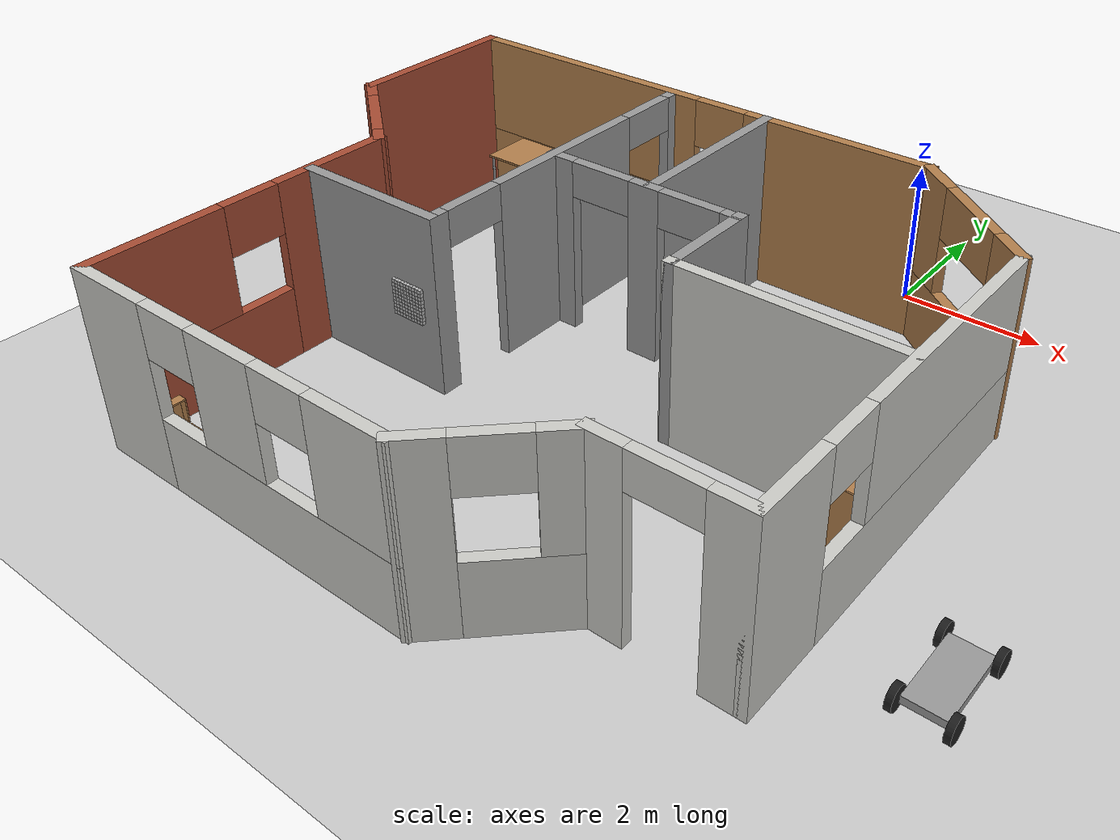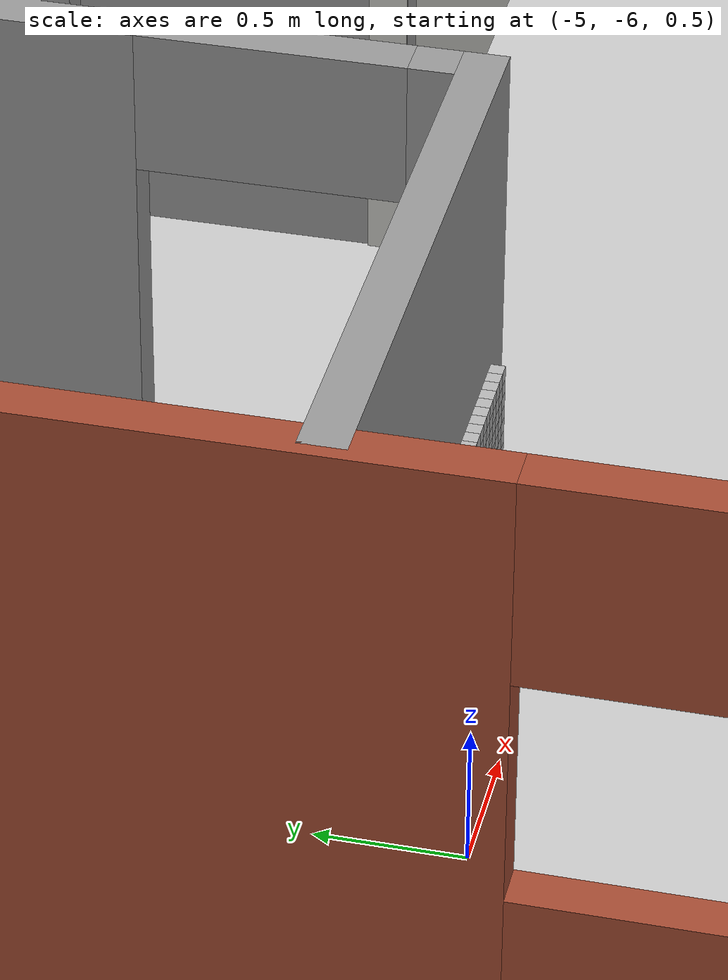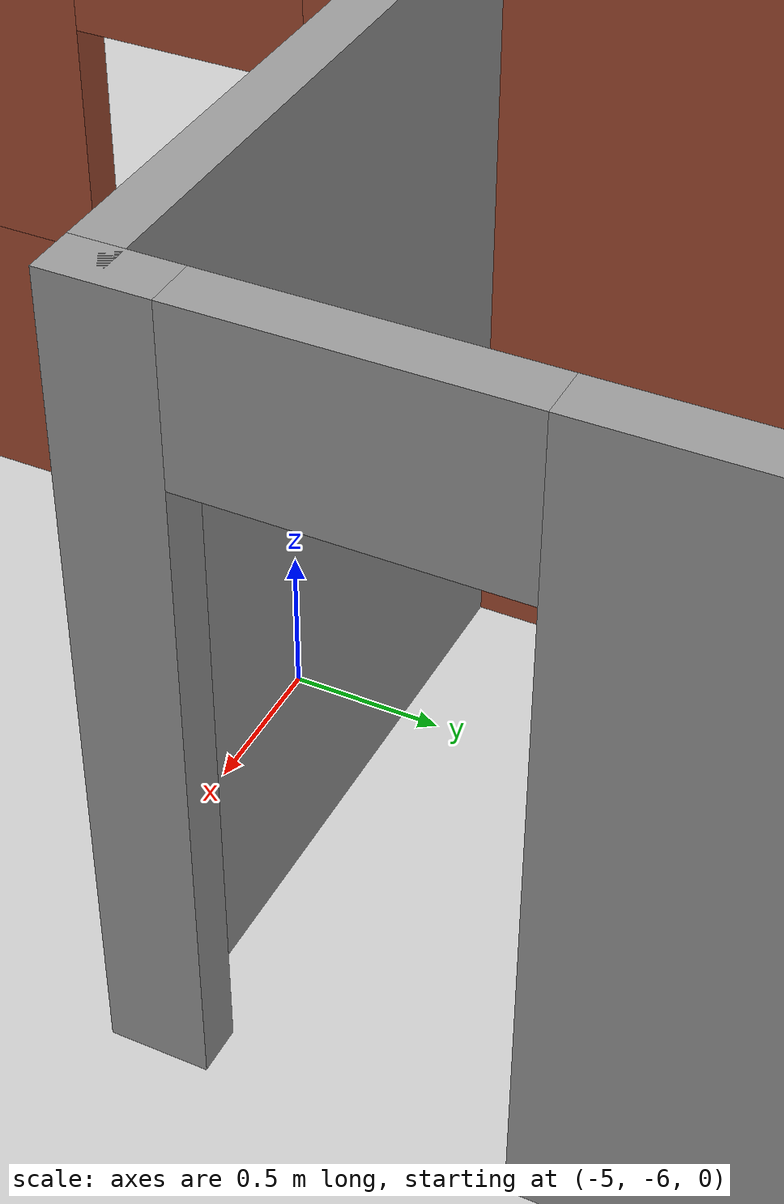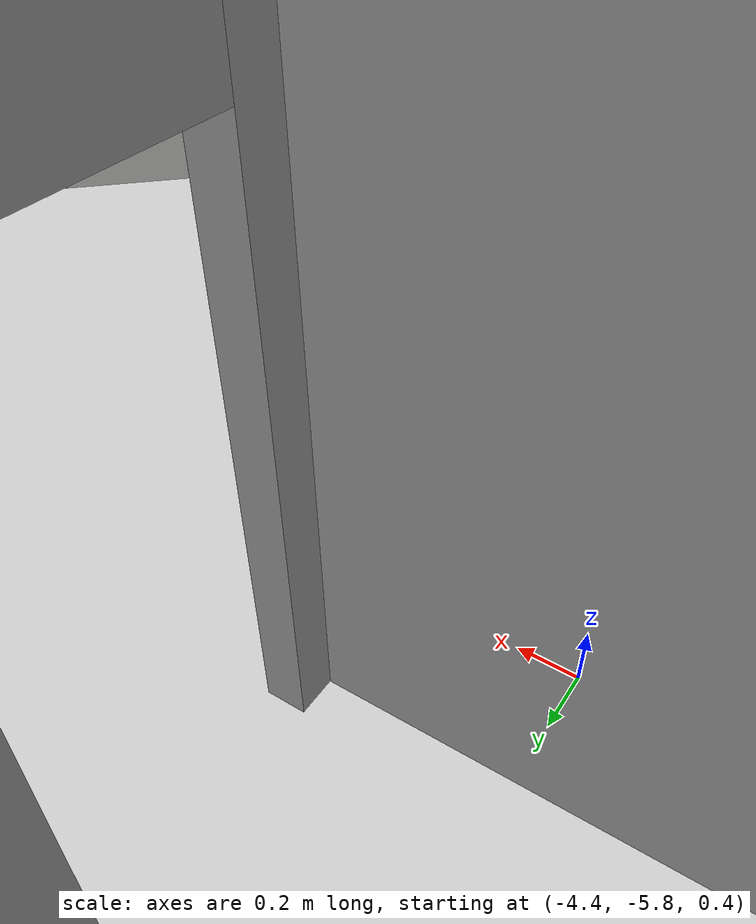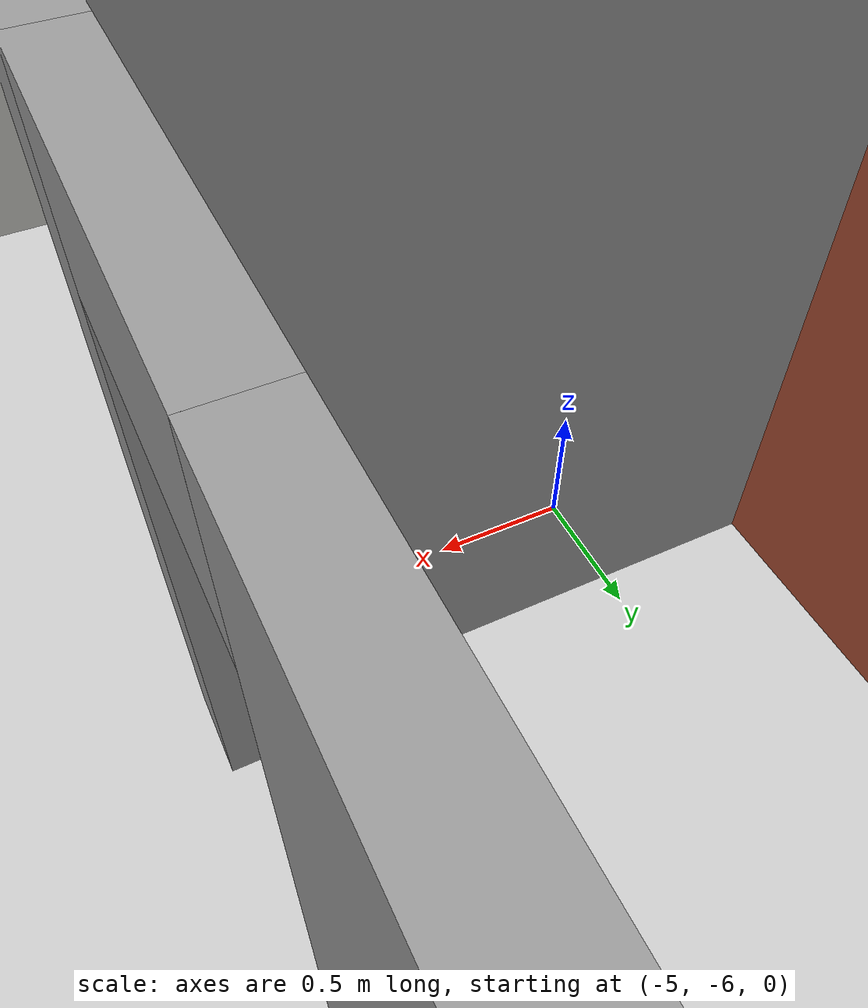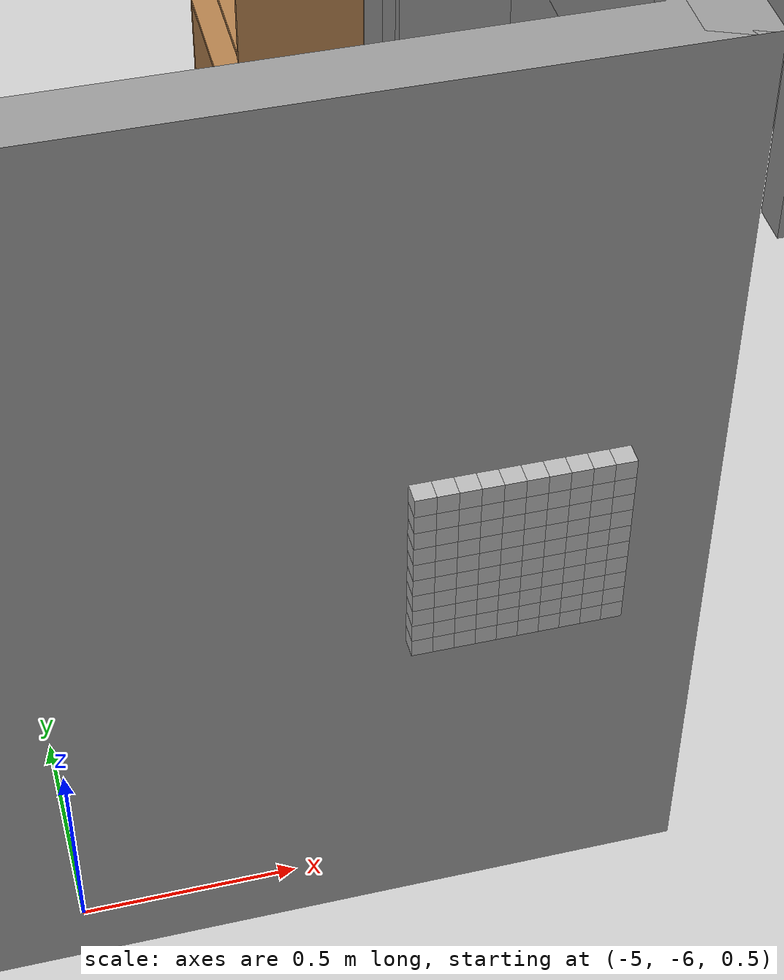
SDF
<sdf version="1.6">
 <world name="default">
  <light name="sun" type="directional">
   <pose>0 0 10 0 -0 0</pose>
   <diffuse>0.8 0.8 0.8 1</diffuse>
   <specular>0.2 0.2 0.2 1</specular>
   <attenuation>
    <range>1000</range>
    <constant>0.9</constant>
    <linear>0.01</linear>
    <quadratic>0.001</quadratic>
   </attenuation>
   <direction>-0.5 0.1 -0.9</direction>
  </light>
  <model name="ground_plane">
   <static>1</static>
   <link name="link">
    <collision name="collision">
     <geometry><plane><normal>0 0 1</normal><size>100 100</size></plane></geometry>
     <surface><friction><ode><mu>100</mu><mu2>50</mu2></ode></friction></surface>
    </collision>
    <visual name="visual">
     <cast_shadows>0</cast_shadows>
     <geometry><plane><normal>0 0 1</normal><size>100 100</size></plane></geometry>
     <material>
      <script><uri>file://media/materials/scripts/gazebo.material</uri><name>Gazebo/Grey</name></script>
     </material>
    </visual>
   </link>
  </model>
  <gravity>0 0 -9.8</gravity>
  <magnetic_field>6e-06 2.3e-05 -4.2e-05</magnetic_field>
  <atmosphere type="adiabatic"/>
  <physics name="default_physics" default="0" type="ode">
   <max_step_size>0.001</max_step_size>
   <real_time_factor>1</real_time_factor>
   <real_time_update_rate>1000</real_time_update_rate>
  </physics>
  <scene><ambient>0.4 0.4 0.4 1</ambient><background>0.7 0.7 0.7 1</background><shadows>1</shadows></scene>
  <spherical_coordinates>
   <surface_model>EARTH_WGS84</surface_model>
   <latitude_deg>0</latitude_deg>
   <longitude_deg>0</longitude_deg>
   <elevation>0</elevation>
   <heading_deg>0</heading_deg>
  </spherical_coordinates>
  <model name="apartment">
   <pose>-2.40567 -4.86545 0 0 -0 0</pose>
   <link name="Wall_0">
    <pose>-3.27233 -1.84604 0 0 0 -1.5708</pose>
    <visual name="Wall_0_Visual_0">
     <pose>-1.35529 0 1.25 0 -0 0</pose>
     <geometry><box><size>1.80243 0.15 2.5</size></box></geometry>
     <material>
      <script><uri>file://media/materials/scripts/gazebo.material</uri><name>Gazebo/Bricks</name></script>
      <ambient>1 1 1 1</ambient>
     </material>
     <meta><layer>0</layer></meta>
    </visual>
    <collision name="Wall_0_Collision_0">
     <geometry><box><size>1.80243 0.15 2.5</size></box></geometry>
     <pose>-1.35529 0 1.25 0 -0 0</pose>
    </collision>
    <visual name="Wall_0_Visual_1">
     <pose>0.901213 0 0.5 0 -0 0</pose>
     <geometry><box><size>2.71057 0.15 1</size></box></geometry>
     <material>
      <script><uri>file://media/materials/scripts/gazebo.material</uri><name>Gazebo/Bricks</name></script>
      <ambient>1 1 1 1</ambient>
     </material>
     <meta><layer>0</layer></meta>
    </visual>
    <collision name="Wall_0_Collision_1">
     <geometry><box><size>2.71057 0.15 1</size></box></geometry>
     <pose>0.901213 0 0.5 0 -0 0</pose>
    </collision>
    <visual name="Wall_0_Visual_2">
     <pose>1.30121 0 1.75 0 -0 0</pose>
     <geometry><box><size>1.91057 0.15 1.5</size></box></geometry>
     <material>
      <script><uri>file://media/materials/scripts/gazebo.material</uri><name>Gazebo/Bricks</name></script>
      <ambient>1 1 1 1</ambient>
     </material>
     <meta><layer>0</layer></meta>
    </visual>
    <collision name="Wall_0_Collision_2">
     <geometry><box><size>1.91057 0.15 1.5</size></box></geometry>
     <pose>1.30121 0 1.75 0 -0 0</pose>
    </collision>
    <visual name="Wall_0_Visual_3">
     <pose>-0.054074 0 2.15 0 -0 0</pose>
     <geometry><box><size>0.8 0.15 0.7</size></box></geometry>
     <material>
      <script><uri>file://media/materials/scripts/gazebo.material</uri><name>Gazebo/Bricks</name></script>
      <ambient>1 1 1 1</ambient>
     </material>
     <meta><layer>0</layer></meta>
    </visual>
    <collision name="Wall_0_Collision_3">
     <geometry><box><size>0.8 0.15 0.7</size></box></geometry>
     <pose>-0.054074 0 2.15 0 -0 0</pose>
    </collision>
   </link>
   <link name="Wall_1">
    <pose>-0.847334 -4.02754 0 0 -0 0</pose>
    <visual name="Wall_1_Visual_0">
     <pose>-1.88666 0 1.25 0 -0 0</pose>
     <geometry><box><size>1.22668 0.15 2.5</size></box></geometry>
     <material>
      <script><uri>file://media/materials/scripts/gazebo.material</uri><name>Gazebo/CeilingTiled</name></script>
      <ambient>1 1 1 1</ambient>
     </material>
     <meta><layer>0</layer></meta>
    </visual>
    <collision name="Wall_1_Collision_0">
     <geometry><box><size>1.22668 0.15 2.5</size></box></geometry>
     <pose>-1.88666 0 1.25 0 -0 0</pose>
    </collision>
    <visual name="Wall_1_Visual_1">
     <pose>0.613341 0 0.5 0 -0 0</pose>
     <geometry><box><size>3.77332 0.15 1</size></box></geometry>
     <material>
      <script><uri>file://media/materials/scripts/gazebo.material</uri><name>Gazebo/CeilingTiled</name></script>
      <ambient>1 1 1 1</ambient>
     </material>
     <meta><layer>0</layer></meta>
    </visual>
    <collision name="Wall_1_Collision_1">
     <geometry><box><size>3.77332 0.15 1</size></box></geometry>
     <pose>0.613341 0 0.5 0 -0 0</pose>
    </collision>
    <visual name="Wall_1_Visual_2">
     <pose>0.029536 0 1.75 0 -0 0</pose>
     <geometry><box><size>1.00571 0.15 1.5</size></box></geometry>
     <material>
      <script><uri>file://media/materials/scripts/gazebo.material</uri><name>Gazebo/CeilingTiled</name></script>
      <ambient>1 1 1 1</ambient>
     </material>
     <meta><layer>0</layer></meta>
    </visual>
    <collision name="Wall_1_Collision_2">
     <geometry><box><size>1.00571 0.15 1.5</size></box></geometry>
     <pose>0.029536 0 1.75 0 -0 0</pose>
    </collision>
    <visual name="Wall_1_Visual_3">
     <pose>1.9162 0 1.75 0 -0 0</pose>
     <geometry><box><size>1.16761 0.15 1.5</size></box></geometry>
     <material>
      <script><uri>file://media/materials/scripts/gazebo.material</uri><name>Gazebo/CeilingTiled</name></script>
      <ambient>1 1 1 1</ambient>
     </material>
     <meta><layer>0</layer></meta>
    </visual>
    <collision name="Wall_1_Collision_3">
     <geometry><box><size>1.16761 0.15 1.5</size></box></geometry>
     <pose>1.9162 0 1.75 0 -0 0</pose>
    </collision>
    <visual name="Wall_1_Visual_4">
     <pose>-0.873318 0 2.15 0 -0 0</pose>
     <geometry><box><size>0.8 0.15 0.7</size></box></geometry>
     <material>
      <script><uri>file://media/materials/scripts/gazebo.material</uri><name>Gazebo/CeilingTiled</name></script>
      <ambient>1 1 1 1</ambient>
     </material>
     <meta><layer>0</layer></meta>
    </visual>
    <collision name="Wall_1_Collision_4">
     <geometry><box><size>0.8 0.15 0.7</size></box></geometry>
     <pose>-0.873318 0 2.15 0 -0 0</pose>
    </collision>
    <visual name="Wall_1_Visual_5">
     <pose>0.932391 0 2.15 0 -0 0</pose>
     <geometry><box><size>0.8 0.15 0.7</size></box></geometry>
     <material>
      <script><uri>file://media/materials/scripts/gazebo.material</uri><name>Gazebo/CeilingTiled</name></script>
      <ambient>1 1 1 1</ambient>
     </material>
     <meta><layer>0</layer></meta>
    </visual>
    <collision name="Wall_1_Collision_5">
     <geometry><box><size>0.8 0.15 0.7</size></box></geometry>
     <pose>0.932391 0 2.15 0 -0 0</pose>
    </collision>
   </link>
   <link name="Wall_17">
    <collision name="Wall_17_Collision">
     <geometry><box><size>2.25 0.15 2.5</size></box></geometry>
     <pose>0 0 1.25 0 -0 0</pose>
    </collision>
    <visual name="Wall_17_Visual">
     <pose>0 0 1.25 0 -0 0</pose>
     <geometry><box><size>2.25 0.15 2.5</size></box></geometry>
     <material>
      <script><uri>file://media/materials/scripts/gazebo.material</uri><name>Gazebo/Grey</name></script>
      <ambient>1 1 1 1</ambient>
     </material>
     <meta><layer>0</layer></meta>
    </visual>
    <pose>-2.17325 -0.830129 0 0 -0 0</pose>
   </link>
   <link name="Wall_2">
    <pose>2.22217 -3.40105 0 0 -0 0.771237</pose>
    <visual name="Wall_2_Visual_0">
     <pose>-0.667862 0 1.25 0 -0 0</pose>
     <geometry><box><size>0.612204 0.15 2.5</size></box></geometry>
     <material>
      <script><uri>file://media/materials/scripts/gazebo.material</uri><name>Gazebo/CeilingTiled</name></script>
      <ambient>1 1 1 1</ambient>
     </material>
     <meta><layer>0</layer></meta>
    </visual>
    <collision name="Wall_2_Collision_0">
     <geometry><box><size>0.612204 0.15 2.5</size></box></geometry>
     <pose>-0.667862 0 1.25 0 -0 0</pose>
    </collision>
    <visual name="Wall_2_Visual_1">
     <pose>0.306102 0 0.5 0 -0 0</pose>
     <geometry><box><size>1.33573 0.15 1</size></box></geometry>
     <material>
      <script><uri>file://media/materials/scripts/gazebo.material</uri><name>Gazebo/CeilingTiled</name></script>
      <ambient>1 1 1 1</ambient>
     </material>
     <meta><layer>0</layer></meta>
    </visual>
    <collision name="Wall_2_Collision_1">
     <geometry><box><size>1.33573 0.15 1</size></box></geometry>
     <pose>0.306102 0 0.5 0 -0 0</pose>
    </collision>
    <visual name="Wall_2_Visual_2">
     <pose>0.706102 0 1.75 0 -0 0</pose>
     <geometry><box><size>0.535725 0.15 1.5</size></box></geometry>
     <material>
      <script><uri>file://media/materials/scripts/gazebo.material</uri><name>Gazebo/CeilingTiled</name></script>
      <ambient>1 1 1 1</ambient>
     </material>
     <meta><layer>0</layer></meta>
    </visual>
    <collision name="Wall_2_Collision_2">
     <geometry><box><size>0.535725 0.15 1.5</size></box></geometry>
     <pose>0.706102 0 1.75 0 -0 0</pose>
    </collision>
    <visual name="Wall_2_Visual_3">
     <pose>0.03824 0 2.15 0 -0 0</pose>
     <geometry><box><size>0.8 0.15 0.7</size></box></geometry>
     <material>
      <script><uri>file://media/materials/scripts/gazebo.material</uri><name>Gazebo/CeilingTiled</name></script>
      <ambient>1 1 1 1</ambient>
     </material>
     <meta><layer>0</layer></meta>
    </visual>
    <collision name="Wall_2_Collision_3">
     <geometry><box><size>0.8 0.15 0.7</size></box></geometry>
     <pose>0.03824 0 2.15 0 -0 0</pose>
    </collision>
   </link>
   <link name="Wall_21">
    <pose>-1.12325 1.59487 0 0 -0 1.5708</pose>
    <visual name="Wall_21_Visual_0">
     <pose>-2.349 0 1.25 0 -0 0</pose>
     <geometry><box><size>0.301995 0.15 2.5</size></box></geometry>
     <material>
      <script><uri>file://media/materials/scripts/gazebo.material</uri><name>Gazebo/Grey</name></script>
      <ambient>1 1 1 1</ambient>
     </material>
     <meta><layer>0</layer></meta>
    </visual>
    <collision name="Wall_21_Collision_0">
     <geometry><box><size>0.301995 0.15 2.5</size></box></geometry>
     <pose>-2.349 0 1.25 0 -0 0</pose>
    </collision>
    <visual name="Wall_21_Visual_1">
     <pose>-0.002486 0 1.25 0 -0 0</pose>
     <geometry><box><size>2.59104 0.15 2.5</size></box></geometry>
     <material>
      <script><uri>file://media/materials/scripts/gazebo.material</uri><name>Gazebo/Grey</name></script>
      <ambient>1 1 1 1</ambient>
     </material>
     <meta><layer>0</layer></meta>
    </visual>
    <collision name="Wall_21_Collision_1">
     <geometry><box><size>2.59104 0.15 2.5</size></box></geometry>
     <pose>-0.002486 0 1.25 0 -0 0</pose>
    </collision>
    <visual name="Wall_21_Visual_2">
     <pose>2.34652 0 1.25 0 -0 0</pose>
     <geometry><box><size>0.306967 0.15 2.5</size></box></geometry>
     <material>
      <script><uri>file://media/materials/scripts/gazebo.material</uri><name>Gazebo/Grey</name></script>
      <ambient>1 1 1 1</ambient>
     </material>
     <meta><layer>0</layer></meta>
    </visual>
    <collision name="Wall_21_Collision_2">
     <geometry><box><size>0.306967 0.15 2.5</size></box></geometry>
     <pose>2.34652 0 1.25 0 -0 0</pose>
    </collision>
    <visual name="Wall_21_Visual_3">
     <pose>-1.74801 0 2.25 0 -0 0</pose>
     <geometry><box><size>0.9 0.15 0.5</size></box></geometry>
     <material>
      <script><uri>file://media/materials/scripts/gazebo.material</uri><name>Gazebo/Grey</name></script>
      <ambient>1 1 1 1</ambient>
     </material>
     <meta><layer>0</layer></meta>
    </visual>
    <collision name="Wall_21_Collision_3">
     <geometry><box><size>0.9 0.15 0.5</size></box></geometry>
     <pose>-1.74801 0 2.25 0 -0 0</pose>
    </collision>
    <visual name="Wall_21_Visual_4">
     <pose>1.74303 0 2.25 0 -0 0</pose>
     <geometry><box><size>0.9 0.15 0.5</size></box></geometry>
     <material>
      <script><uri>file://media/materials/scripts/gazebo.material</uri><name>Gazebo/Grey</name></script>
      <ambient>1 1 1 1</ambient>
     </material>
     <meta><layer>0</layer></meta>
    </visual>
    <collision name="Wall_21_Collision_4">
     <geometry><box><size>0.9 0.15 0.5</size></box></geometry>
     <pose>1.74303 0 2.25 0 -0 0</pose>
    </collision>
   </link>
   <link name="Wall_25">
    <pose>0.289666 1.41046 0 0 -0 3.14159</pose>
    <visual name="Wall_25_Visual_0">
     <pose>-1.3525 0 1.25 0 -0 0</pose>
     <geometry><box><size>0.295 0.15 2.5</size></box></geometry>
     <material>
      <script><uri>file://media/materials/scripts/gazebo.material</uri><name>Gazebo/Grey</name></script>
      <ambient>1 1 1 1</ambient>
     </material>
     <meta><layer>0</layer></meta>
    </visual>
    <collision name="Wall_25_Collision_0">
     <geometry><box><size>0.295 0.15 2.5</size></box></geometry>
     <pose>-1.3525 0 1.25 0 -0 0</pose>
    </collision>
    <visual name="Wall_25_Visual_1">
     <pose>-0.07438 0 1.25 0 -0 0</pose>
     <geometry><box><size>0.461241 0.15 2.5</size></box></geometry>
     <material>
      <script><uri>file://media/materials/scripts/gazebo.material</uri><name>Gazebo/Grey</name></script>
      <ambient>1 1 1 1</ambient>
     </material>
     <meta><layer>0</layer></meta>
    </visual>
    <collision name="Wall_25_Collision_1">
     <geometry><box><size>0.461241 0.15 2.5</size></box></geometry>
     <pose>-0.07438 0 1.25 0 -0 0</pose>
    </collision>
    <visual name="Wall_25_Visual_2">
     <pose>1.27812 0 1.25 0 -0 0</pose>
     <geometry><box><size>0.443759 0.15 2.5</size></box></geometry>
     <material>
      <script><uri>file://media/materials/scripts/gazebo.material</uri><name>Gazebo/Grey</name></script>
      <ambient>1 1 1 1</ambient>
     </material>
     <meta><layer>0</layer></meta>
    </visual>
    <collision name="Wall_25_Collision_2">
     <geometry><box><size>0.443759 0.15 2.5</size></box></geometry>
     <pose>1.27812 0 1.25 0 -0 0</pose>
    </collision>
    <visual name="Wall_25_Visual_3">
     <pose>-0.755 0 2.25 0 -0 0</pose>
     <geometry><box><size>0.9 0.15 0.5</size></box></geometry>
     <material>
      <script><uri>file://media/materials/scripts/gazebo.material</uri><name>Gazebo/Grey</name></script>
      <ambient>1 1 1 1</ambient>
     </material>
     <meta><layer>0</layer></meta>
    </visual>
    <collision name="Wall_25_Collision_3">
     <geometry><box><size>0.9 0.15 0.5</size></box></geometry>
     <pose>-0.755 0 2.25 0 -0 0</pose>
    </collision>
    <visual name="Wall_25_Visual_4">
     <pose>0.606241 0 2.25 0 -0 0</pose>
     <geometry><box><size>0.9 0.15 0.5</size></box></geometry>
     <material>
      <script><uri>file://media/materials/scripts/gazebo.material</uri><name>Gazebo/Grey</name></script>
      <ambient>1 1 1 1</ambient>
     </material>
     <meta><layer>0</layer></meta>
    </visual>
    <collision name="Wall_25_Collision_4">
     <geometry><box><size>0.9 0.15 0.5</size></box></geometry>
     <pose>0.606241 0 2.25 0 -0 0</pose>
    </collision>
   </link>
   <link name="Wall_3">
    <pose>3.79167 -2.77454 0 0 -0 0</pose>
    <visual name="Wall_3_Visual_0">
     <pose>-0.729967 0 1.25 0 -0 0</pose>
     <geometry><box><size>0.540065 0.15 2.5</size></box></geometry>
     <material>
      <script><uri>file://media/materials/scripts/gazebo.material</uri><name>Gazebo/CeilingTiled</name></script>
      <ambient>1 1 1 1</ambient>
     </material>
     <meta><layer>0</layer></meta>
    </visual>
    <collision name="Wall_3_Collision_0">
     <geometry><box><size>0.540065 0.15 2.5</size></box></geometry>
     <pose>-0.729967 0 1.25 0 -0 0</pose>
    </collision>
    <visual name="Wall_3_Visual_1">
     <pose>0.720033 0 1.25 0 -0 0</pose>
     <geometry><box><size>0.559935 0.15 2.5</size></box></geometry>
     <material>
      <script><uri>file://media/materials/scripts/gazebo.material</uri><name>Gazebo/CeilingTiled</name></script>
      <ambient>1 1 1 1</ambient>
     </material>
     <meta><layer>0</layer></meta>
    </visual>
    <collision name="Wall_3_Collision_1">
     <geometry><box><size>0.559935 0.15 2.5</size></box></geometry>
     <pose>0.720033 0 1.25 0 -0 0</pose>
    </collision>
    <visual name="Wall_3_Visual_2">
     <pose>-0.009935 0 2.25 0 -0 0</pose>
     <geometry><box><size>0.9 0.15 0.5</size></box></geometry>
     <material>
      <script><uri>file://media/materials/scripts/gazebo.material</uri><name>Gazebo/CeilingTiled</name></script>
      <ambient>1 1 1 1</ambient>
     </material>
     <meta><layer>0</layer></meta>
    </visual>
    <collision name="Wall_3_Collision_2">
     <geometry><box><size>0.9 0.15 0.5</size></box></geometry>
     <pose>-0.009935 0 2.25 0 -0 0</pose>
    </collision>
   </link>
   <link name="Wall_30">
    <collision name="Wall_30_Collision">
     <geometry><box><size>2.75 0.15 2.5</size></box></geometry>
     <pose>0 0 1.25 0 -0 0</pose>
    </collision>
    <visual name="Wall_30_Visual">
     <pose>0 0 1.25 0 -0 0</pose>
     <geometry><box><size>2.75 0.15 2.5</size></box></geometry>
     <material>
      <script><uri>file://media/materials/scripts/gazebo.material</uri><name>Gazebo/Grey</name></script>
      <ambient>1 1 1 1</ambient>
     </material>
     <meta><layer>0</layer></meta>
    </visual>
    <pose>0.419085 2.73344 0 0 0 -1.5708</pose>
   </link>
   <link name="Wall_33">
    <collision name="Wall_33_Collision">
     <geometry><box><size>1.5 0.15 2.5</size></box></geometry>
     <pose>0 0 1.25 0 -0 0</pose>
    </collision>
    <visual name="Wall_33_Visual">
     <pose>0 0 1.25 0 -0 0</pose>
     <geometry><box><size>1.5 0.15 2.5</size></box></geometry>
     <material>
      <script><uri>file://media/materials/scripts/gazebo.material</uri><name>Gazebo/Grey</name></script>
      <ambient>1 1 1 1</ambient>
     </material>
     <meta><layer>0</layer></meta>
    </visual>
    <pose>1.71691 0.763206 0 0 0 -1.5708</pose>
   </link>
   <link name="Wall_34">
    <collision name="Wall_34_Collision">
     <geometry><box><size>3.156 0.15 2.5</size></box></geometry>
     <pose>0 0 1.25 0 -0 0</pose>
    </collision>
    <visual name="Wall_34_Visual">
     <pose>0 0 1.25 0 -0 0</pose>
     <geometry><box><size>3.156 0.15 2.5</size></box></geometry>
     <material>
      <script><uri>file://media/materials/scripts/gazebo.material</uri><name>Gazebo/CeilingTiled</name></script>
      <ambient>1 1 1 1</ambient>
     </material>
     <meta><layer>0</layer></meta>
    </visual>
    <pose>3.20654 0.088206 0 0 -0 0</pose>
   </link>
   <link name="Wall_4">
    <pose>4.71667 -0.099545 0 0 -0 1.5708</pose>
    <visual name="Wall_4_Visual_0">
     <pose>-2.15037 0 1.25 0 -0 0</pose>
     <geometry><box><size>1.19925 0.15 2.5</size></box></geometry>
     <material>
      <script><uri>file://media/materials/scripts/gazebo.material</uri><name>Gazebo/CeilingTiled</name></script>
      <ambient>1 1 1 1</ambient>
     </material>
     <meta><layer>0</layer></meta>
    </visual>
    <collision name="Wall_4_Collision_0">
     <geometry><box><size>1.19925 0.15 2.5</size></box></geometry>
     <pose>-2.15037 0 1.25 0 -0 0</pose>
    </collision>
    <visual name="Wall_4_Visual_1">
     <pose>0.599625 0 0.5 0 -0 0</pose>
     <geometry><box><size>4.30075 0.15 1</size></box></geometry>
     <material>
      <script><uri>file://media/materials/scripts/gazebo.material</uri><name>Gazebo/CeilingTiled</name></script>
      <ambient>1 1 1 1</ambient>
     </material>
     <meta><layer>0</layer></meta>
    </visual>
    <collision name="Wall_4_Collision_1">
     <geometry><box><size>4.30075 0.15 1</size></box></geometry>
     <pose>0.599625 0 0.5 0 -0 0</pose>
    </collision>
    <visual name="Wall_4_Visual_2">
     <pose>0.999625 0 1.75 0 -0 0</pose>
     <geometry><box><size>3.50075 0.15 1.5</size></box></geometry>
     <material>
      <script><uri>file://media/materials/scripts/gazebo.material</uri><name>Gazebo/CeilingTiled</name></script>
      <ambient>1 1 1 1</ambient>
     </material>
     <meta><layer>0</layer></meta>
    </visual>
    <collision name="Wall_4_Collision_2">
     <geometry><box><size>3.50075 0.15 1.5</size></box></geometry>
     <pose>0.999625 0 1.75 0 -0 0</pose>
    </collision>
    <visual name="Wall_4_Visual_3">
     <pose>-1.15075 0 2.15 0 -0 0</pose>
     <geometry><box><size>0.8 0.15 0.7</size></box></geometry>
     <material>
      <script><uri>file://media/materials/scripts/gazebo.material</uri><name>Gazebo/CeilingTiled</name></script>
      <ambient>1 1 1 1</ambient>
     </material>
     <meta><layer>0</layer></meta>
    </visual>
    <collision name="Wall_4_Collision_3">
     <geometry><box><size>0.8 0.15 0.7</size></box></geometry>
     <pose>-1.15075 0 2.15 0 -0 0</pose>
    </collision>
   </link>
   <link name="Wall_5">
    <pose>3.80017 3.30195 0 0 -0 2.47133</pose>
    <visual name="Wall_5_Visual_0">
     <pose>-0.935133 0 1.25 0 -0 0</pose>
     <geometry><box><size>0.61839 0.15 2.5</size></box></geometry>
     <material>
      <script><uri>file://media/materials/scripts/gazebo.material</uri><name>Gazebo/Wood</name></script>
      <ambient>1 1 1 1</ambient>
     </material>
     <meta><layer>0</layer></meta>
    </visual>
    <collision name="Wall_5_Collision_0">
     <geometry><box><size>0.61839 0.15 2.5</size></box></geometry>
     <pose>-0.935133 0 1.25 0 -0 0</pose>
    </collision>
    <visual name="Wall_5_Visual_1">
     <pose>0.309195 0 0.5 0 -0 0</pose>
     <geometry><box><size>1.87027 0.15 1</size></box></geometry>
     <material>
      <script><uri>file://media/materials/scripts/gazebo.material</uri><name>Gazebo/Wood</name></script>
      <ambient>1 1 1 1</ambient>
     </material>
     <meta><layer>0</layer></meta>
    </visual>
    <collision name="Wall_5_Collision_1">
     <geometry><box><size>1.87027 0.15 1</size></box></geometry>
     <pose>0.309195 0 0.5 0 -0 0</pose>
    </collision>
    <visual name="Wall_5_Visual_2">
     <pose>0.909195 0 1.75 0 -0 0</pose>
     <geometry><box><size>0.670266 0.15 1.5</size></box></geometry>
     <material>
      <script><uri>file://media/materials/scripts/gazebo.material</uri><name>Gazebo/Wood</name></script>
      <ambient>1 1 1 1</ambient>
     </material>
     <meta><layer>0</layer></meta>
    </visual>
    <collision name="Wall_5_Collision_2">
     <geometry><box><size>0.670266 0.15 1.5</size></box></geometry>
     <pose>0.909195 0 1.75 0 -0 0</pose>
    </collision>
    <visual name="Wall_5_Visual_3">
     <pose>-0.025938 0 2.15 0 -0 0</pose>
     <geometry><box><size>1.2 0.15 0.7</size></box></geometry>
     <material>
      <script><uri>file://media/materials/scripts/gazebo.material</uri><name>Gazebo/Wood</name></script>
      <ambient>1 1 1 1</ambient>
     </material>
     <meta><layer>0</layer></meta>
    </visual>
    <collision name="Wall_5_Collision_3">
     <geometry><box><size>1.2 0.15 0.7</size></box></geometry>
     <pose>-0.025938 0 2.15 0 -0 0</pose>
    </collision>
   </link>
   <link name="Wall_6">
    <pose>-0.916334 4.02846 0 0 -0 3.14159</pose>
    <visual name="Wall_6_Visual_0">
     <pose>-2.44792 0 1.25 0 -0 0</pose>
     <geometry><box><size>2.85416 0.15 2.5</size></box></geometry>
     <material>
      <script><uri>file://media/materials/scripts/gazebo.material</uri><name>Gazebo/Wood</name></script>
      <ambient>1 1 1 1</ambient>
     </material>
     <meta><layer>0</layer></meta>
    </visual>
    <collision name="Wall_6_Collision_0">
     <geometry><box><size>2.85416 0.15 2.5</size></box></geometry>
     <pose>-2.44792 0 1.25 0 -0 0</pose>
    </collision>
    <visual name="Wall_6_Visual_1">
     <pose>1.42708 0 0.5 0 -0 0</pose>
     <geometry><box><size>4.89584 0.15 1</size></box></geometry>
     <material>
      <script><uri>file://media/materials/scripts/gazebo.material</uri><name>Gazebo/Wood</name></script>
      <ambient>1 1 1 1</ambient>
     </material>
     <meta><layer>0</layer></meta>
    </visual>
    <collision name="Wall_6_Collision_1">
     <geometry><box><size>4.89584 0.15 1</size></box></geometry>
     <pose>1.42708 0 0.5 0 -0 0</pose>
    </collision>
    <visual name="Wall_6_Visual_2">
     <pose>1.82708 0 1.75 0 -0 0</pose>
     <geometry><box><size>4.09584 0.15 1.5</size></box></geometry>
     <material>
      <script><uri>file://media/materials/scripts/gazebo.material</uri><name>Gazebo/Wood</name></script>
      <ambient>1 1 1 1</ambient>
     </material>
     <meta><layer>0</layer></meta>
    </visual>
    <collision name="Wall_6_Collision_2">
     <geometry><box><size>4.09584 0.15 1.5</size></box></geometry>
     <pose>1.82708 0 1.75 0 -0 0</pose>
    </collision>
    <visual name="Wall_6_Visual_3">
     <pose>-0.620842 0 2.15 0 -0 0</pose>
     <geometry><box><size>0.8 0.15 0.7</size></box></geometry>
     <material>
      <script><uri>file://media/materials/scripts/gazebo.material</uri><name>Gazebo/Wood</name></script>
      <ambient>1 1 1 1</ambient>
     </material>
     <meta><layer>0</layer></meta>
    </visual>
    <collision name="Wall_6_Collision_3">
     <geometry><box><size>0.8 0.15 0.7</size></box></geometry>
     <pose>-0.620842 0 2.15 0 -0 0</pose>
    </collision>
   </link>
   <link name="Wall_7">
    <collision name="Wall_7_Collision">
     <geometry><box><size>2.66 0.15 2.5</size></box></geometry>
     <pose>0 0 1.25 0 -0 0</pose>
    </collision>
    <visual name="Wall_7_Visual">
     <pose>0 0 1.25 0 -0 0</pose>
     <geometry><box><size>2.66 0.15 2.5</size></box></geometry>
     <material>
      <script><uri>file://media/materials/scripts/gazebo.material</uri><name>Gazebo/Bricks</name></script>
      <ambient>1 1 1 1</ambient>
     </material>
     <meta><layer>0</layer></meta>
    </visual>
    <pose>-4.71633 2.77345 0 0 0 -1.5708</pose>
   </link>
   <link name="Wall_8">
    <pose>-3.99433 0.926955 0 0 0 -0.68637</pose>
    <visual name="Wall_8_Visual_0">
     <pose>-0.766559 0 1.25 0 -0 0</pose>
     <geometry><box><size>0.483597 0.15 2.5</size></box></geometry>
     <material>
      <script><uri>file://media/materials/scripts/gazebo.material</uri><name>Gazebo/Bricks</name></script>
      <ambient>1 1 1 1</ambient>
     </material>
     <meta><layer>0</layer></meta>
    </visual>
    <collision name="Wall_8_Collision_0">
     <geometry><box><size>0.483597 0.15 2.5</size></box></geometry>
     <pose>-0.766559 0 1.25 0 -0 0</pose>
    </collision>
    <visual name="Wall_8_Visual_1">
     <pose>0.241798 0 0.5 0 -0 0</pose>
     <geometry><box><size>1.53312 0.15 1</size></box></geometry>
     <material>
      <script><uri>file://media/materials/scripts/gazebo.material</uri><name>Gazebo/Bricks</name></script>
      <ambient>1 1 1 1</ambient>
     </material>
     <meta><layer>0</layer></meta>
    </visual>
    <collision name="Wall_8_Collision_1">
     <geometry><box><size>1.53312 0.15 1</size></box></geometry>
     <pose>0.241798 0 0.5 0 -0 0</pose>
    </collision>
    <visual name="Wall_8_Visual_2">
     <pose>0.841798 0 1.75 0 -0 0</pose>
     <geometry><box><size>0.333118 0.15 1.5</size></box></geometry>
     <material>
      <script><uri>file://media/materials/scripts/gazebo.material</uri><name>Gazebo/Bricks</name></script>
      <ambient>1 1 1 1</ambient>
     </material>
     <meta><layer>0</layer></meta>
    </visual>
    <collision name="Wall_8_Collision_2">
     <geometry><box><size>0.333118 0.15 1.5</size></box></geometry>
     <pose>0.841798 0 1.75 0 -0 0</pose>
    </collision>
    <visual name="Wall_8_Visual_3">
     <pose>0.075239 0 2.15 0 -0 0</pose>
     <geometry><box><size>1.2 0.15 0.7</size></box></geometry>
     <material>
      <script><uri>file://media/materials/scripts/gazebo.material</uri><name>Gazebo/Bricks</name></script>
      <ambient>1 1 1 1</ambient>
     </material>
     <meta><layer>0</layer></meta>
    </visual>
    <collision name="Wall_8_Collision_3">
     <geometry><box><size>1.2 0.15 0.7</size></box></geometry>
     <pose>0.075239 0 2.15 0 -0 0</pose>
    </collision>
   </link>
   <static>1</static>
  </model>
  <model name="bookshelf">
   <static>1</static>
   <link name="link">
    <inertial><mass>1</mass></inertial>
    <collision name="back">
     <pose>0 0.005 0.6 0 -0 0</pose>
     <geometry><box><size>0.9 0.01 1.2</size></box></geometry>
    </collision>
    <visual name="visual1">
     <pose>0 0.005 0.6 0 -0 0</pose>
     <geometry><box><size>0.9 0.01 1.2</size></box></geometry>
     <material>
      <script><uri>file://media/materials/scripts/gazebo.material</uri><name>Gazebo/Wood</name></script>
     </material>
    </visual>
    <collision name="left_side">
     <pose>0.45 -0.195 0.6 0 -0 0</pose>
     <geometry><box><size>0.02 0.4 1.2</size></box></geometry>
    </collision>
    <visual name="visual2">
     <pose>0.45 -0.195 0.6 0 -0 0</pose>
     <geometry><box><size>0.02 0.4 1.2</size></box></geometry>
     <material>
      <script><uri>file://media/materials/scripts/gazebo.material</uri><name>Gazebo/Wood</name></script>
     </material>
    </visual>
    <collision name="right_side">
     <pose>-0.45 -0.195 0.6 0 -0 0</pose>
     <geometry><box><size>0.02 0.4 1.2</size></box></geometry>
    </collision>
    <visual name="visual3">
     <pose>-0.45 -0.195 0.6 0 -0 0</pose>
     <geometry><box><size>0.02 0.4 1.2</size></box></geometry>
     <material>
      <script><uri>file://media/materials/scripts/gazebo.material</uri><name>Gazebo/Wood</name></script>
     </material>
    </visual>
    <collision name="bottom">
     <pose>0 -0.195 0.03 0 -0 0</pose>
     <geometry><box><size>0.88 0.4 0.06</size></box></geometry>
    </collision>
    <visual name="visual4">
     <pose>0 -0.195 0.03 0 -0 0</pose>
     <geometry><box><size>0.88 0.4 0.06</size></box></geometry>
     <material>
      <script><uri>file://media/materials/scripts/gazebo.material</uri><name>Gazebo/Wood</name></script>
     </material>
    </visual>
    <collision name="top">
     <pose>0 -0.195 1.19 0 -0 0</pose>
     <geometry><box><size>0.88 0.4 0.02</size></box></geometry>
    </collision>
    <visual name="visual5">
     <pose>0 -0.195 1.19 0 -0 0</pose>
     <geometry><box><size>0.88 0.4 0.02</size></box></geometry>
     <material>
      <script><uri>file://media/materials/scripts/gazebo.material</uri><name>Gazebo/Wood</name></script>
     </material>
    </visual>
    <collision name="low_shelf">
     <pose>0 -0.195 0.43 0 -0 0</pose>
     <geometry><box><size>0.88 0.4 0.02</size></box></geometry>
    </collision>
    <visual name="visual6">
     <pose>0 -0.195 0.43 0 -0 0</pose>
     <geometry><box><size>0.88 0.4 0.02</size></box></geometry>
     <material>
      <script><uri>file://media/materials/scripts/gazebo.material</uri><name>Gazebo/Wood</name></script>
     </material>
    </visual>
    <collision name="high_shelf">
     <pose>0 -0.195 0.8 0 -0 0</pose>
     <geometry><box><size>0.88 0.4 0.02</size></box></geometry>
    </collision>
    <visual name="visual7">
     <pose>0 -0.195 0.8 0 -0 0</pose>
     <geometry><box><size>0.88 0.4 0.02</size></box></geometry>
     <material>
      <script><uri>file://media/materials/scripts/gazebo.material</uri><name>Gazebo/Wood</name></script>
     </material>
    </visual>
   </link>
   <pose>-3.62882 -2.73668 0 0 0 -1.58135</pose>
  </model>
  <model name="cabinet">
   <static>1</static>
   <link name="cabinet_bottom_plate">
    <inertial>
     <pose>0 0 -1 0 -0 0</pose>
     <inertia><ixx>2.05</ixx><ixy>0</ixy><ixz>0</ixz><iyy>2.05</iyy><iyz>0</iyz><izz>2.05</izz></inertia>
     <mass>25</mass>
    </inertial>
    <collision name="cabinet_bottom_plate_geom">
     <pose>0 0 0.01 0 -0 0</pose>
     <geometry><box><size>0.45 0.45 0.02</size></box></geometry>
    </collision>
    <visual name="cabinet_bottom_plate_geom_visual">
     <pose>0 0 0.01 0 -0 0</pose>
     <geometry><box><size>0.45 0.45 0.02</size></box></geometry>
     <material>
      <script><uri>file://media/materials/scripts/gazebo.material</uri><name>Gazebo/Wood</name></script>
     </material>
    </visual>
    <collision name="cabinet_bottom_plate_geom_cabinet_back_plate">
     <pose>0.235 0 0.51 0 -0 0</pose>
     <geometry><box><size>0.02 0.45 1.02</size></box></geometry>
    </collision>
    <visual name="cabinet_bottom_plate_geom_cabinet_back_plate_visual">
     <pose>0.235 0 0.51 0 -0 0</pose>
     <geometry><box><size>0.02 0.45 1.02</size></box></geometry>
     <material>
      <script><uri>file://media/materials/scripts/gazebo.material</uri><name>Gazebo/Wood</name></script>
     </material>
    </visual>
    <collision name="cabinet_bottom_plate_geom_cabinet_left_plate">
     <pose>0 0.235 0.51 0 -0 0</pose>
     <geometry><box><size>0.45 0.02 1.02</size></box></geometry>
    </collision>
    <visual name="cabinet_bottom_plate_geom_cabinet_left_plate_visual">
     <pose>0 0.235 0.51 0 -0 0</pose>
     <geometry><box><size>0.45 0.02 1.02</size></box></geometry>
     <material>
      <script><uri>file://media/materials/scripts/gazebo.material</uri><name>Gazebo/Wood</name></script>
     </material>
    </visual>
    <collision name="cabinet_bottom_plate_geom_cabinet_middle_plate">
     <pose>0 0 0.51 0 -0 0</pose>
     <geometry><box><size>0.45 0.45 0.02</size></box></geometry>
    </collision>
    <visual name="cabinet_bottom_plate_geom_cabinet_middle_plate_visual">
     <pose>0 0 0.51 0 -0 0</pose>
     <geometry><box><size>0.45 0.45 0.02</size></box></geometry>
     <material>
      <script><uri>file://media/materials/scripts/gazebo.material</uri><name>Gazebo/Wood</name></script>
     </material>
    </visual>
    <collision name="cabinet_bottom_plate_geom_cabinet_right_plate">
     <pose>0 -0.235 0.51 0 -0 0</pose>
     <geometry><box><size>0.45 0.02 1.02</size></box></geometry>
    </collision>
    <visual name="cabinet_bottom_plate_geom_cabinet_right_plate_visual">
     <pose>0 -0.235 0.51 0 -0 0</pose>
     <geometry><box><size>0.45 0.02 1.02</size></box></geometry>
     <material>
      <script><uri>file://media/materials/scripts/gazebo.material</uri><name>Gazebo/Wood</name></script>
     </material>
    </visual>
    <collision name="cabinet_bottom_plate_geom_cabinet_top_plate">
     <pose>0 0 1.01 0 -0 0</pose>
     <geometry><box><size>0.45 0.45 0.02</size></box></geometry>
    </collision>
    <visual name="cabinet_bottom_plate_geom_cabinet_top_plate_visual">
     <pose>0 0 1.01 0 -0 0</pose>
     <geometry><box><size>0.45 0.45 0.02</size></box></geometry>
     <material>
      <script><uri>file://media/materials/scripts/gazebo.material</uri><name>Gazebo/Wood</name></script>
     </material>
    </visual>
   </link>
   <pose>1.98989 -5.14777 0 0 -0 0</pose>
  </model>
  <model name="breakable_test">
   <pose>-4.1545 -5.80229 1 0 -0 0</pose>
   <link name="link_0_0">
    <inertial>
     <mass>0.3375</mass>
     <inertia>
      <ixx>0.000140625</ixx>
      <iyy>0.000140625</iyy>
      <izz>0.000140625</izz>
      <ixy>0</ixy>
      <ixz>0</ixz>
      <iyz>0</iyz>
     </inertia>
    </inertial>
    <collision name="collision"><geometry><box><size>0.05 0.05 0.05</size></box></geometry></collision>
    <visual name="visual"><geometry><box><size>0.05 0.05 0.05</size></box></geometry></visual>
   </link>
   <joint name="joint_0_0" type="revolute">
    <parent>world</parent>
    <child>link_0_0</child>
    <axis>
     <xyz>0 0 1</xyz>
     <limit><lower>0</lower><upper>0</upper></limit>
     <use_parent_model_frame>1</use_parent_model_frame>
     <dynamics><spring_reference>0</spring_reference><spring_stiffness>0</spring_stiffness></dynamics>
    </axis>
    <physics><ode><erp>1</erp><cfm>1</cfm><limit><cfm>0</cfm><erp>0.2</erp></limit></ode></physics>
    <sensor name="force_torque" type="force_torque">
     <always_on>1</always_on>
     <update_rate>1000</update_rate>
     <plugin name="breakable_0_0" filename="libBreakableJointPlugin.so">
      <breaking_force_N>50</breaking_force_N>
     </plugin>
    </sensor>
   </joint>
   <link name="link_0_1">
    <pose>0 0 0.05 0 -0 0</pose>
    <inertial>
     <mass>0.3375</mass>
     <inertia>
      <ixx>0.000140625</ixx>
      <iyy>0.000140625</iyy>
      <izz>0.000140625</izz>
      <ixy>0</ixy>
      <ixz>0</ixz>
      <iyz>0</iyz>
     </inertia>
    </inertial>
    <collision name="collision"><geometry><box><size>0.05 0.05 0.05</size></box></geometry></collision>
    <visual name="visual"><geometry><box><size>0.05 0.05 0.05</size></box></geometry></visual>
   </link>
   <joint name="joint_0_1" type="revolute">
    <parent>world</parent>
    <child>link_0_1</child>
    <axis>
     <xyz>0 0 1</xyz>
     <limit><lower>0</lower><upper>0</upper></limit>
     <use_parent_model_frame>1</use_parent_model_frame>
     <dynamics><spring_reference>0</spring_reference><spring_stiffness>0</spring_stiffness></dynamics>
    </axis>
    <physics><ode><erp>1</erp><cfm>1</cfm><limit><cfm>0</cfm><erp>0.2</erp></limit></ode></physics>
    <sensor name="force_torque" type="force_torque">
     <always_on>1</always_on>
     <update_rate>1000</update_rate>
     <plugin name="breakable_0_1" filename="libBreakableJointPlugin.so">
      <breaking_force_N>50</breaking_force_N>
     </plugin>
    </sensor>
   </joint>
   <link name="link_0_2">
    <pose>0 0 0.1 0 -0 0</pose>
    <inertial>
     <mass>0.3375</mass>
     <inertia>
      <ixx>0.000140625</ixx>
      <iyy>0.000140625</iyy>
      <izz>0.000140625</izz>
      <ixy>0</ixy>
      <ixz>0</ixz>
      <iyz>0</iyz>
     </inertia>
    </inertial>
    <collision name="collision"><geometry><box><size>0.05 0.05 0.05</size></box></geometry></collision>
    <visual name="visual"><geometry><box><size>0.05 0.05 0.05</size></box></geometry></visual>
   </link>
   <joint name="joint_0_2" type="revolute">
    <parent>world</parent>
    <child>link_0_2</child>
    <axis>
     <xyz>0 0 1</xyz>
     <limit><lower>0</lower><upper>0</upper></limit>
     <use_parent_model_frame>1</use_parent_model_frame>
     <dynamics><spring_reference>0</spring_reference><spring_stiffness>0</spring_stiffness></dynamics>
    </axis>
    <physics><ode><erp>1</erp><cfm>1</cfm><limit><cfm>0</cfm><erp>0.2</erp></limit></ode></physics>
    <sensor name="force_torque" type="force_torque">
     <always_on>1</always_on>
     <update_rate>1000</update_rate>
     <plugin name="breakable_0_2" filename="libBreakableJointPlugin.so">
      <breaking_force_N>50</breaking_force_N>
     </plugin>
    </sensor>
   </joint>
   <link name="link_0_3">
    <pose>0 0 0.15 0 -0 0</pose>
    <inertial>
     <mass>0.3375</mass>
     <inertia>
      <ixx>0.000140625</ixx>
      <iyy>0.000140625</iyy>
      <izz>0.000140625</izz>
      <ixy>0</ixy>
      <ixz>0</ixz>
      <iyz>0</iyz>
     </inertia>
    </inertial>
    <collision name="collision"><geometry><box><size>0.05 0.05 0.05</size></box></geometry></collision>
    <visual name="visual"><geometry><box><size>0.05 0.05 0.05</size></box></geometry></visual>
   </link>
   <joint name="joint_0_3" type="revolute">
    <parent>world</parent>
    <child>link_0_3</child>
    <axis>
     <xyz>0 0 1</xyz>
     <limit><lower>0</lower><upper>0</upper></limit>
     <use_parent_model_frame>1</use_parent_model_frame>
     <dynamics><spring_reference>0</spring_reference><spring_stiffness>0</spring_stiffness></dynamics>
    </axis>
    <physics><ode><erp>1</erp><cfm>1</cfm><limit><cfm>0</cfm><erp>0.2</erp></limit></ode></physics>
    <sensor name="force_torque" type="force_torque">
     <always_on>1</always_on>
     <update_rate>1000</update_rate>
     <plugin name="breakable_0_3" filename="libBreakableJointPlugin.so">
      <breaking_force_N>50</breaking_force_N>
     </plugin>
    </sensor>
   </joint>
   <link name="link_0_4">
    <pose>0 0 0.2 0 -0 0</pose>
    <inertial>
     <mass>0.3375</mass>
     <inertia>
      <ixx>0.000140625</ixx>
      <iyy>0.000140625</iyy>
      <izz>0.000140625</izz>
      <ixy>0</ixy>
      <ixz>0</ixz>
      <iyz>0</iyz>
     </inertia>
    </inertial>
    <collision name="collision"><geometry><box><size>0.05 0.05 0.05</size></box></geometry></collision>
    <visual name="visual"><geometry><box><size>0.05 0.05 0.05</size></box></geometry></visual>
   </link>
   <joint name="joint_0_4" type="revolute">
    <parent>world</parent>
    <child>link_0_4</child>
    <axis>
     <xyz>0 0 1</xyz>
     <limit><lower>0</lower><upper>0</upper></limit>
     <use_parent_model_frame>1</use_parent_model_frame>
     <dynamics><spring_reference>0</spring_reference><spring_stiffness>0</spring_stiffness></dynamics>
    </axis>
    <physics><ode><erp>1</erp><cfm>1</cfm><limit><cfm>0</cfm><erp>0.2</erp></limit></ode></physics>
    <sensor name="force_torque" type="force_torque">
     <always_on>1</always_on>
     <update_rate>1000</update_rate>
     <plugin name="breakable_0_4" filename="libBreakableJointPlugin.so">
      <breaking_force_N>50</breaking_force_N>
     </plugin>
    </sensor>
   </joint>
   <link name="link_0_5">
    <pose>0 0 0.25 0 -0 0</pose>
    <inertial>
     <mass>0.3375</mass>
     <inertia>
      <ixx>0.000140625</ixx>
      <iyy>0.000140625</iyy>
      <izz>0.000140625</izz>
      <ixy>0</ixy>
      <ixz>0</ixz>
      <iyz>0</iyz>
     </inertia>
    </inertial>
    <collision name="collision"><geometry><box><size>0.05 0.05 0.05</size></box></geometry></collision>
    <visual name="visual"><geometry><box><size>0.05 0.05 0.05</size></box></geometry></visual>
   </link>
   <joint name="joint_0_5" type="revolute">
    <parent>world</parent>
    <child>link_0_5</child>
    <axis>
     <xyz>0 0 1</xyz>
     <limit><lower>0</lower><upper>0</upper></limit>
     <use_parent_model_frame>1</use_parent_model_frame>
     <dynamics><spring_reference>0</spring_reference><spring_stiffness>0</spring_stiffness></dynamics>
    </axis>
    <physics><ode><erp>1</erp><cfm>1</cfm><limit><cfm>0</cfm><erp>0.2</erp></limit></ode></physics>
    <sensor name="force_torque" type="force_torque">
     <always_on>1</always_on>
     <update_rate>1000</update_rate>
     <plugin name="breakable_0_5" filename="libBreakableJointPlugin.so">
      <breaking_force_N>50</breaking_force_N>
     </plugin>
    </sensor>
   </joint>
   <link name="link_0_6">
    <pose>0 0 0.3 0 -0 0</pose>
    <inertial>
     <mass>0.3375</mass>
     <inertia>
      <ixx>0.000140625</ixx>
      <iyy>0.000140625</iyy>
      <izz>0.000140625</izz>
      <ixy>0</ixy>
      <ixz>0</ixz>
      <iyz>0</iyz>
     </inertia>
    </inertial>
    <collision name="collision"><geometry><box><size>0.05 0.05 0.05</size></box></geometry></collision>
    <visual name="visual"><geometry><box><size>0.05 0.05 0.05</size></box></geometry></visual>
   </link>
   <joint name="joint_0_6" type="revolute">
    <parent>world</parent>
    <child>link_0_6</child>
    <axis>
     <xyz>0 0 1</xyz>
     <limit><lower>0</lower><upper>0</upper></limit>
     <use_parent_model_frame>1</use_parent_model_frame>
     <dynamics><spring_reference>0</spring_reference><spring_stiffness>0</spring_stiffness></dynamics>
    </axis>
    <physics><ode><erp>1</erp><cfm>1</cfm><limit><cfm>0</cfm><erp>0.2</erp></limit></ode></physics>
    <sensor name="force_torque" type="force_torque">
     <always_on>1</always_on>
     <update_rate>1000</update_rate>
     <plugin name="breakable_0_6" filename="libBreakableJointPlugin.so">
      <breaking_force_N>50</breaking_force_N>
     </plugin>
    </sensor>
   </joint>
   <link name="link_0_7">
    <pose>0 0 0.35 0 -0 0</pose>
    <inertial>
     <mass>0.3375</mass>
     <inertia>
      <ixx>0.000140625</ixx>
      <iyy>0.000140625</iyy>
      <izz>0.000140625</izz>
      <ixy>0</ixy>
      <ixz>0</ixz>
      <iyz>0</iyz>
     </inertia>
    </inertial>
    <collision name="collision"><geometry><box><size>0.05 0.05 0.05</size></box></geometry></collision>
    <visual name="visual"><geometry><box><size>0.05 0.05 0.05</size></box></geometry></visual>
   </link>
   <joint name="joint_0_7" type="revolute">
    <parent>world</parent>
    <child>link_0_7</child>
    <axis>
     <xyz>0 0 1</xyz>
     <limit><lower>0</lower><upper>0</upper></limit>
     <use_parent_model_frame>1</use_parent_model_frame>
     <dynamics><spring_reference>0</spring_reference><spring_stiffness>0</spring_stiffness></dynamics>
    </axis>
    <physics><ode><erp>1</erp><cfm>1</cfm><limit><cfm>0</cfm><erp>0.2</erp></limit></ode></physics>
    <sensor name="force_torque" type="force_torque">
     <always_on>1</always_on>
     <update_rate>1000</update_rate>
     <plugin name="breakable_0_7" filename="libBreakableJointPlugin.so">
      <breaking_force_N>50</breaking_force_N>
     </plugin>
    </sensor>
   </joint>
   <link name="link_0_8">
    <pose>0 0 0.4 0 -0 0</pose>
    <inertial>
     <mass>0.3375</mass>
     <inertia>
      <ixx>0.000140625</ixx>
      <iyy>0.000140625</iyy>
      <izz>0.000140625</izz>
      <ixy>0</ixy>
      <ixz>0</ixz>
      <iyz>0</iyz>
     </inertia>
    </inertial>
    <collision name="collision"><geometry><box><size>0.05 0.05 0.05</size></box></geometry></collision>
    <visual name="visual"><geometry><box><size>0.05 0.05 0.05</size></box></geometry></visual>
   </link>
   <joint name="joint_0_8" type="revolute">
    <parent>world</parent>
    <child>link_0_8</child>
    <axis>
     <xyz>0 0 1</xyz>
     <limit><lower>0</lower><upper>0</upper></limit>
     <use_parent_model_frame>1</use_parent_model_frame>
     <dynamics><spring_reference>0</spring_reference><spring_stiffness>0</spring_stiffness></dynamics>
    </axis>
    <physics><ode><erp>1</erp><cfm>1</cfm><limit><cfm>0</cfm><erp>0.2</erp></limit></ode></physics>
    <sensor name="force_torque" type="force_torque">
     <always_on>1</always_on>
     <update_rate>1000</update_rate>
     <plugin name="breakable_0_8" filename="libBreakableJointPlugin.so">
      <breaking_force_N>50</breaking_force_N>
     </plugin>
    </sensor>
   </joint>
   <link name="link_0_9">
    <pose>0 0 0.45 0 -0 0</pose>
    <inertial>
     <mass>0.3375</mass>
     <inertia>
      <ixx>0.000140625</ixx>
      <iyy>0.000140625</iyy>
      <izz>0.000140625</izz>
      <ixy>0</ixy>
      <ixz>0</ixz>
      <iyz>0</iyz>
     </inertia>
    </inertial>
    <collision name="collision"><geometry><box><size>0.05 0.05 0.05</size></box></geometry></collision>
    <visual name="visual"><geometry><box><size>0.05 0.05 0.05</size></box></geometry></visual>
   </link>
   <joint name="joint_0_9" type="revolute">
    <parent>world</parent>
    <child>link_0_9</child>
    <axis>
     <xyz>0 0 1</xyz>
     <limit><lower>0</lower><upper>0</upper></limit>
     <use_parent_model_frame>1</use_parent_model_frame>
     <dynamics><spring_reference>0</spring_reference><spring_stiffness>0</spring_stiffness></dynamics>
    </axis>
    <physics><ode><erp>1</erp><cfm>1</cfm><limit><cfm>0</cfm><erp>0.2</erp></limit></ode></physics>
    <sensor name="force_torque" type="force_torque">
     <always_on>1</always_on>
     <update_rate>1000</update_rate>
     <plugin name="breakable_0_9" filename="libBreakableJointPlugin.so">
      <breaking_force_N>50</breaking_force_N>
     </plugin>
    </sensor>
   </joint>
   <link name="link_1_0">
    <pose>0.05 0 0 0 -0 0</pose>
    <inertial>
     <mass>0.3375</mass>
     <inertia>
      <ixx>0.000140625</ixx>
      <iyy>0.000140625</iyy>
      <izz>0.000140625</izz>
      <ixy>0</ixy>
      <ixz>0</ixz>
      <iyz>0</iyz>
     </inertia>
    </inertial>
    <collision name="collision"><geometry><box><size>0.05 0.05 0.05</size></box></geometry></collision>
    <visual name="visual"><geometry><box><size>0.05 0.05 0.05</size></box></geometry></visual>
   </link>
   <joint name="joint_1_0" type="revolute">
    <parent>world</parent>
    <child>link_1_0</child>
    <axis>
     <xyz>0 0 1</xyz>
     <limit><lower>0</lower><upper>0</upper></limit>
     <use_parent_model_frame>1</use_parent_model_frame>
     <dynamics><spring_reference>0</spring_reference><spring_stiffness>0</spring_stiffness></dynamics>
    </axis>
    <physics><ode><erp>1</erp><cfm>1</cfm><limit><cfm>0</cfm><erp>0.2</erp></limit></ode></physics>
    <sensor name="force_torque" type="force_torque">
     <always_on>1</always_on>
     <update_rate>1000</update_rate>
     <plugin name="breakable_1_0" filename="libBreakableJointPlugin.so">
      <breaking_force_N>50</breaking_force_N>
     </plugin>
    </sensor>
   </joint>
   <link name="link_1_1">
    <pose>0.05 0 0.05 0 -0 0</pose>
    <inertial>
     <mass>0.3375</mass>
     <inertia>
      <ixx>0.000140625</ixx>
      <iyy>0.000140625</iyy>
      <izz>0.000140625</izz>
      <ixy>0</ixy>
      <ixz>0</ixz>
      <iyz>0</iyz>
     </inertia>
    </inertial>
    <collision name="collision"><geometry><box><size>0.05 0.05 0.05</size></box></geometry></collision>
    <visual name="visual"><geometry><box><size>0.05 0.05 0.05</size></box></geometry></visual>
   </link>
   <joint name="joint_1_1" type="revolute">
    <parent>world</parent>
    <child>link_1_1</child>
    <axis>
     <xyz>0 0 1</xyz>
     <limit><lower>0</lower><upper>0</upper></limit>
     <use_parent_model_frame>1</use_parent_model_frame>
     <dynamics><spring_reference>0</spring_reference><spring_stiffness>0</spring_stiffness></dynamics>
    </axis>
    <physics><ode><erp>1</erp><cfm>1</cfm><limit><cfm>0</cfm><erp>0.2</erp></limit></ode></physics>
    <sensor name="force_torque" type="force_torque">
     <always_on>1</always_on>
     <update_rate>1000</update_rate>
     <plugin name="breakable_1_1" filename="libBreakableJointPlugin.so">
      <breaking_force_N>50</breaking_force_N>
     </plugin>
    </sensor>
   </joint>
   <link name="link_1_2">
    <pose>0.05 0 0.1 0 -0 0</pose>
    <inertial>
     <mass>0.3375</mass>
     <inertia>
      <ixx>0.000140625</ixx>
      <iyy>0.000140625</iyy>
      <izz>0.000140625</izz>
      <ixy>0</ixy>
      <ixz>0</ixz>
      <iyz>0</iyz>
     </inertia>
    </inertial>
    <collision name="collision"><geometry><box><size>0.05 0.05 0.05</size></box></geometry></collision>
    <visual name="visual"><geometry><box><size>0.05 0.05 0.05</size></box></geometry></visual>
   </link>
   <joint name="joint_1_2" type="revolute">
    <parent>world</parent>
    <child>link_1_2</child>
    <axis>
     <xyz>0 0 1</xyz>
     <limit><lower>0</lower><upper>0</upper></limit>
     <use_parent_model_frame>1</use_parent_model_frame>
     <dynamics><spring_reference>0</spring_reference><spring_stiffness>0</spring_stiffness></dynamics>
    </axis>
    <physics><ode><erp>1</erp><cfm>1</cfm><limit><cfm>0</cfm><erp>0.2</erp></limit></ode></physics>
    <sensor name="force_torque" type="force_torque">
     <always_on>1</always_on>
     <update_rate>1000</update_rate>
     <plugin name="breakable_1_2" filename="libBreakableJointPlugin.so">
      <breaking_force_N>50</breaking_force_N>
     </plugin>
    </sensor>
   </joint>
   <link name="link_1_3">
    <pose>0.05 0 0.15 0 -0 0</pose>
    <inertial>
     <mass>0.3375</mass>
     <inertia>
      <ixx>0.000140625</ixx>
      <iyy>0.000140625</iyy>
      <izz>0.000140625</izz>
      <ixy>0</ixy>
      <ixz>0</ixz>
      <iyz>0</iyz>
     </inertia>
    </inertial>
    <collision name="collision"><geometry><box><size>0.05 0.05 0.05</size></box></geometry></collision>
    <visual name="visual"><geometry><box><size>0.05 0.05 0.05</size></box></geometry></visual>
   </link>
   <joint name="joint_1_3" type="revolute">
    <parent>world</parent>
    <child>link_1_3</child>
    <axis>
     <xyz>0 0 1</xyz>
     <limit><lower>0</lower><upper>0</upper></limit>
     <use_parent_model_frame>1</use_parent_model_frame>
     <dynamics><spring_reference>0</spring_reference><spring_stiffness>0</spring_stiffness></dynamics>
    </axis>
    <physics><ode><erp>1</erp><cfm>1</cfm><limit><cfm>0</cfm><erp>0.2</erp></limit></ode></physics>
    <sensor name="force_torque" type="force_torque">
     <always_on>1</always_on>
     <update_rate>1000</update_rate>
     <plugin name="breakable_1_3" filename="libBreakableJointPlugin.so">
      <breaking_force_N>50</breaking_force_N>
     </plugin>
    </sensor>
   </joint>
   <link name="link_1_4">
    <pose>0.05 0 0.2 0 -0 0</pose>
    <inertial>
     <mass>0.3375</mass>
     <inertia>
      <ixx>0.000140625</ixx>
      <iyy>0.000140625</iyy>
      <izz>0.000140625</izz>
      <ixy>0</ixy>
      <ixz>0</ixz>
      <iyz>0</iyz>
     </inertia>
    </inertial>
    <collision name="collision"><geometry><box><size>0.05 0.05 0.05</size></box></geometry></collision>
    <visual name="visual"><geometry><box><size>0.05 0.05 0.05</size></box></geometry></visual>
   </link>
   <joint name="joint_1_4" type="revolute">
    <parent>world</parent>
    <child>link_1_4</child>
    <axis>
     <xyz>0 0 1</xyz>
     <limit><lower>0</lower><upper>0</upper></limit>
     <use_parent_model_frame>1</use_parent_model_frame>
     <dynamics><spring_reference>0</spring_reference><spring_stiffness>0</spring_stiffness></dynamics>
    </axis>
    <physics><ode><erp>1</erp><cfm>1</cfm><limit><cfm>0</cfm><erp>0.2</erp></limit></ode></physics>
    <sensor name="force_torque" type="force_torque">
     <always_on>1</always_on>
     <update_rate>1000</update_rate>
     <plugin name="breakable_1_4" filename="libBreakableJointPlugin.so">
      <breaking_force_N>50</breaking_force_N>
     </plugin>
    </sensor>
   </joint>
   <link name="link_1_5">
    <pose>0.05 0 0.25 0 -0 0</pose>
    <inertial>
     <mass>0.3375</mass>
     <inertia>
      <ixx>0.000140625</ixx>
      <iyy>0.000140625</iyy>
      <izz>0.000140625</izz>
      <ixy>0</ixy>
      <ixz>0</ixz>
      <iyz>0</iyz>
     </inertia>
    </inertial>
    <collision name="collision"><geometry><box><size>0.05 0.05 0.05</size></box></geometry></collision>
    <visual name="visual"><geometry><box><size>0.05 0.05 0.05</size></box></geometry></visual>
   </link>
   <joint name="joint_1_5" type="revolute">
    <parent>world</parent>
    <child>link_1_5</child>
    <axis>
     <xyz>0 0 1</xyz>
     <limit><lower>0</lower><upper>0</upper></limit>
     <use_parent_model_frame>1</use_parent_model_frame>
     <dynamics><spring_reference>0</spring_reference><spring_stiffness>0</spring_stiffness></dynamics>
    </axis>
    <physics><ode><erp>1</erp><cfm>1</cfm><limit><cfm>0</cfm><erp>0.2</erp></limit></ode></physics>
    <sensor name="force_torque" type="force_torque">
     <always_on>1</always_on>
     <update_rate>1000</update_rate>
     <plugin name="breakable_1_5" filename="libBreakableJointPlugin.so">
      <breaking_force_N>50</breaking_force_N>
     </plugin>
    </sensor>
   </joint>
   <link name="link_1_6">
    <pose>0.05 0 0.3 0 -0 0</pose>
    <inertial>
     <mass>0.3375</mass>
     <inertia>
      <ixx>0.000140625</ixx>
      <iyy>0.000140625</iyy>
      <izz>0.000140625</izz>
      <ixy>0</ixy>
      <ixz>0</ixz>
      <iyz>0</iyz>
     </inertia>
    </inertial>
    <collision name="collision"><geometry><box><size>0.05 0.05 0.05</size></box></geometry></collision>
    <visual name="visual"><geometry><box><size>0.05 0.05 0.05</size></box></geometry></visual>
   </link>
   <joint name="joint_1_6" type="revolute">
    <parent>world</parent>
    <child>link_1_6</child>
    <axis>
     <xyz>0 0 1</xyz>
     <limit><lower>0</lower><upper>0</upper></limit>
     <use_parent_model_frame>1</use_parent_model_frame>
     <dynamics><spring_reference>0</spring_reference><spring_stiffness>0</spring_stiffness></dynamics>
    </axis>
    <physics><ode><erp>1</erp><cfm>1</cfm><limit><cfm>0</cfm><erp>0.2</erp></limit></ode></physics>
    <sensor name="force_torque" type="force_torque">
     <always_on>1</always_on>
     <update_rate>1000</update_rate>
     <plugin name="breakable_1_6" filename="libBreakableJointPlugin.so">
      <breaking_force_N>50</breaking_force_N>
     </plugin>
    </sensor>
   </joint>
   <link name="link_1_7">
    <pose>0.05 0 0.35 0 -0 0</pose>
    <inertial>
     <mass>0.3375</mass>
     <inertia>
      <ixx>0.000140625</ixx>
      <iyy>0.000140625</iyy>
      <izz>0.000140625</izz>
      <ixy>0</ixy>
      <ixz>0</ixz>
      <iyz>0</iyz>
     </inertia>
    </inertial>
    <collision name="collision"><geometry><box><size>0.05 0.05 0.05</size></box></geometry></collision>
    <visual name="visual"><geometry><box><size>0.05 0.05 0.05</size></box></geometry></visual>
   </link>
   <joint name="joint_1_7" type="revolute">
    <parent>world</parent>
    <child>link_1_7</child>
    <axis>
     <xyz>0 0 1</xyz>
     <limit><lower>0</lower><upper>0</upper></limit>
     <use_parent_model_frame>1</use_parent_model_frame>
     <dynamics><spring_reference>0</spring_reference><spring_stiffness>0</spring_stiffness></dynamics>
    </axis>
    <physics><ode><erp>1</erp><cfm>1</cfm><limit><cfm>0</cfm><erp>0.2</erp></limit></ode></physics>
    <sensor name="force_torque" type="force_torque">
     <always_on>1</always_on>
     <update_rate>1000</update_rate>
     <plugin name="breakable_1_7" filename="libBreakableJointPlugin.so">
      <breaking_force_N>50</breaking_force_N>
     </plugin>
    </sensor>
   </joint>
   <link name="link_1_8">
    <pose>0.05 0 0.4 0 -0 0</pose>
    <inertial>
     <mass>0.3375</mass>
     <inertia>
      <ixx>0.000140625</ixx>
      <iyy>0.000140625</iyy>
      <izz>0.000140625</izz>
      <ixy>0</ixy>
      <ixz>0</ixz>
      <iyz>0</iyz>
     </inertia>
    </inertial>
    <collision name="collision"><geometry><box><size>0.05 0.05 0.05</size></box></geometry></collision>
    <visual name="visual"><geometry><box><size>0.05 0.05 0.05</size></box></geometry></visual>
   </link>
   <joint name="joint_1_8" type="revolute">
    <parent>world</parent>
    <child>link_1_8</child>
    <axis>
     <xyz>0 0 1</xyz>
     <limit><lower>0</lower><upper>0</upper></limit>
     <use_parent_model_frame>1</use_parent_model_frame>
     <dynamics><spring_reference>0</spring_reference><spring_stiffness>0</spring_stiffness></dynamics>
    </axis>
    <physics><ode><erp>1</erp><cfm>1</cfm><limit><cfm>0</cfm><erp>0.2</erp></limit></ode></physics>
    <sensor name="force_torque" type="force_torque">
     <always_on>1</always_on>
     <update_rate>1000</update_rate>
     <plugin name="breakable_1_8" filename="libBreakableJointPlugin.so">
      <breaking_force_N>50</breaking_force_N>
     </plugin>
    </sensor>
   </joint>
   <link name="link_1_9">
    <pose>0.05 0 0.45 0 -0 0</pose>
    <inertial>
     <mass>0.3375</mass>
     <inertia>
      <ixx>0.000140625</ixx>
      <iyy>0.000140625</iyy>
      <izz>0.000140625</izz>
      <ixy>0</ixy>
      <ixz>0</ixz>
      <iyz>0</iyz>
     </inertia>
    </inertial>
    <collision name="collision"><geometry><box><size>0.05 0.05 0.05</size></box></geometry></collision>
    <visual name="visual"><geometry><box><size>0.05 0.05 0.05</size></box></geometry></visual>
   </link>
   <joint name="joint_1_9" type="revolute">
    <parent>world</parent>
    <child>link_1_9</child>
    <axis>
     <xyz>0 0 1</xyz>
     <limit><lower>0</lower><upper>0</upper></limit>
     <use_parent_model_frame>1</use_parent_model_frame>
     <dynamics><spring_reference>0</spring_reference><spring_stiffness>0</spring_stiffness></dynamics>
    </axis>
    <physics><ode><erp>1</erp><cfm>1</cfm><limit><cfm>0</cfm><erp>0.2</erp></limit></ode></physics>
    <sensor name="force_torque" type="force_torque">
     <always_on>1</always_on>
     <update_rate>1000</update_rate>
     <plugin name="breakable_1_9" filename="libBreakableJointPlugin.so">
      <breaking_force_N>50</breaking_force_N>
     </plugin>
    </sensor>
   </joint>
   <link name="link_2_0">
    <pose>0.1 0 0 0 -0 0</pose>
    <inertial>
     <mass>0.3375</mass>
     <inertia>
      <ixx>0.000140625</ixx>
      <iyy>0.000140625</iyy>
      <izz>0.000140625</izz>
      <ixy>0</ixy>
      <ixz>0</ixz>
      <iyz>0</iyz>
     </inertia>
    </inertial>
    <collision name="collision"><geometry><box><size>0.05 0.05 0.05</size></box></geometry></collision>
    <visual name="visual"><geometry><box><size>0.05 0.05 0.05</size></box></geometry></visual>
   </link>
   <joint name="joint_2_0" type="revolute">
    <parent>world</parent>
    <child>link_2_0</child>
    <axis>
     <xyz>0 0 1</xyz>
     <limit><lower>0</lower><upper>0</upper></limit>
     <use_parent_model_frame>1</use_parent_model_frame>
     <dynamics><spring_reference>0</spring_reference><spring_stiffness>0</spring_stiffness></dynamics>
    </axis>
    <physics><ode><erp>1</erp><cfm>1</cfm><limit><cfm>0</cfm><erp>0.2</erp></limit></ode></physics>
    <sensor name="force_torque" type="force_torque">
     <always_on>1</always_on>
     <update_rate>1000</update_rate>
     <plugin name="breakable_2_0" filename="libBreakableJointPlugin.so">
      <breaking_force_N>50</breaking_force_N>
     </plugin>
    </sensor>
   </joint>
   <link name="link_2_1">
    <pose>0.1 0 0.05 0 -0 0</pose>
    <inertial>
     <mass>0.3375</mass>
     <inertia>
      <ixx>0.000140625</ixx>
      <iyy>0.000140625</iyy>
      <izz>0.000140625</izz>
      <ixy>0</ixy>
      <ixz>0</ixz>
      <iyz>0</iyz>
     </inertia>
    </inertial>
    <collision name="collision"><geometry><box><size>0.05 0.05 0.05</size></box></geometry></collision>
    <visual name="visual"><geometry><box><size>0.05 0.05 0.05</size></box></geometry></visual>
   </link>
   <joint name="joint_2_1" type="revolute">
    <parent>world</parent>
    <child>link_2_1</child>
    <axis>
     <xyz>0 0 1</xyz>
     <limit><lower>0</lower><upper>0</upper></limit>
     <use_parent_model_frame>1</use_parent_model_frame>
     <dynamics><spring_reference>0</spring_reference><spring_stiffness>0</spring_stiffness></dynamics>
    </axis>
    <physics><ode><erp>1</erp><cfm>1</cfm><limit><cfm>0</cfm><erp>0.2</erp></limit></ode></physics>
    <sensor name="force_torque" type="force_torque">
     <always_on>1</always_on>
     <update_rate>1000</update_rate>
     <plugin name="breakable_2_1" filename="libBreakableJointPlugin.so">
      <breaking_force_N>50</breaking_force_N>
     </plugin>
    </sensor>
   </joint>
   <link name="link_2_2">
    <pose>0.1 0 0.1 0 -0 0</pose>
    <inertial>
     <mass>0.3375</mass>
     <inertia>
      <ixx>0.000140625</ixx>
      <iyy>0.000140625</iyy>
      <izz>0.000140625</izz>
      <ixy>0</ixy>
      <ixz>0</ixz>
      <iyz>0</iyz>
     </inertia>
    </inertial>
    <collision name="collision"><geometry><box><size>0.05 0.05 0.05</size></box></geometry></collision>
    <visual name="visual"><geometry><box><size>0.05 0.05 0.05</size></box></geometry></visual>
   </link>
   <joint name="joint_2_2" type="revolute">
    <parent>world</parent>
    <child>link_2_2</child>
    <axis>
     <xyz>0 0 1</xyz>
     <limit><lower>0</lower><upper>0</upper></limit>
     <use_parent_model_frame>1</use_parent_model_frame>
     <dynamics><spring_reference>0</spring_reference><spring_stiffness>0</spring_stiffness></dynamics>
    </axis>
    <physics><ode><erp>1</erp><cfm>1</cfm><limit><cfm>0</cfm><erp>0.2</erp></limit></ode></physics>
    <sensor name="force_torque" type="force_torque">
     <always_on>1</always_on>
     <update_rate>1000</update_rate>
     <plugin name="breakable_2_2" filename="libBreakableJointPlugin.so">
      <breaking_force_N>50</breaking_force_N>
     </plugin>
    </sensor>
   </joint>
   <link name="link_2_3">
    <pose>0.1 0 0.15 0 -0 0</pose>
    <inertial>
     <mass>0.3375</mass>
     <inertia>
      <ixx>0.000140625</ixx>
      <iyy>0.000140625</iyy>
      <izz>0.000140625</izz>
      <ixy>0</ixy>
      <ixz>0</ixz>
      <iyz>0</iyz>
     </inertia>
    </inertial>
    <collision name="collision"><geometry><box><size>0.05 0.05 0.05</size></box></geometry></collision>
    <visual name="visual"><geometry><box><size>0.05 0.05 0.05</size></box></geometry></visual>
   </link>
   <joint name="joint_2_3" type="revolute">
    <parent>world</parent>
    <child>link_2_3</child>
    <axis>
     <xyz>0 0 1</xyz>
     <limit><lower>0</lower><upper>0</upper></limit>
     <use_parent_model_frame>1</use_parent_model_frame>
     <dynamics><spring_reference>0</spring_reference><spring_stiffness>0</spring_stiffness></dynamics>
    </axis>
    <physics><ode><erp>1</erp><cfm>1</cfm><limit><cfm>0</cfm><erp>0.2</erp></limit></ode></physics>
    <sensor name="force_torque" type="force_torque">
     <always_on>1</always_on>
     <update_rate>1000</update_rate>
     <plugin name="breakable_2_3" filename="libBreakableJointPlugin.so">
      <breaking_force_N>50</breaking_force_N>
     </plugin>
    </sensor>
   </joint>
   <link name="link_2_4">
    <pose>0.1 0 0.2 0 -0 0</pose>
    <inertial>
     <mass>0.3375</mass>
     <inertia>
      <ixx>0.000140625</ixx>
      <iyy>0.000140625</iyy>
      <izz>0.000140625</izz>
      <ixy>0</ixy>
      <ixz>0</ixz>
      <iyz>0</iyz>
     </inertia>
    </inertial>
    <collision name="collision"><geometry><box><size>0.05 0.05 0.05</size></box></geometry></collision>
    <visual name="visual"><geometry><box><size>0.05 0.05 0.05</size></box></geometry></visual>
   </link>
   <joint name="joint_2_4" type="revolute">
    <parent>world</parent>
    <child>link_2_4</child>
    <axis>
     <xyz>0 0 1</xyz>
     <limit><lower>0</lower><upper>0</upper></limit>
     <use_parent_model_frame>1</use_parent_model_frame>
     <dynamics><spring_reference>0</spring_reference><spring_stiffness>0</spring_stiffness></dynamics>
    </axis>
    <physics><ode><erp>1</erp><cfm>1</cfm><limit><cfm>0</cfm><erp>0.2</erp></limit></ode></physics>
    <sensor name="force_torque" type="force_torque">
     <always_on>1</always_on>
     <update_rate>1000</update_rate>
     <plugin name="breakable_2_4" filename="libBreakableJointPlugin.so">
      <breaking_force_N>50</breaking_force_N>
     </plugin>
    </sensor>
   </joint>
   <link name="link_2_5">
    <pose>0.1 0 0.25 0 -0 0</pose>
    <inertial>
     <mass>0.3375</mass>
     <inertia>
      <ixx>0.000140625</ixx>
      <iyy>0.000140625</iyy>
      <izz>0.000140625</izz>
      <ixy>0</ixy>
      <ixz>0</ixz>
      <iyz>0</iyz>
     </inertia>
    </inertial>
    <collision name="collision"><geometry><box><size>0.05 0.05 0.05</size></box></geometry></collision>
    <visual name="visual"><geometry><box><size>0.05 0.05 0.05</size></box></geometry></visual>
   </link>
   <joint name="joint_2_5" type="revolute">
    <parent>world</parent>
    <child>link_2_5</child>
    <axis>
     <xyz>0 0 1</xyz>
     <limit><lower>0</lower><upper>0</upper></limit>
     <use_parent_model_frame>1</use_parent_model_frame>
     <dynamics><spring_reference>0</spring_reference><spring_stiffness>0</spring_stiffness></dynamics>
    </axis>
    <physics><ode><erp>1</erp><cfm>1</cfm><limit><cfm>0</cfm><erp>0.2</erp></limit></ode></physics>
    <sensor name="force_torque" type="force_torque">
     <always_on>1</always_on>
     <update_rate>1000</update_rate>
     <plugin name="breakable_2_5" filename="libBreakableJointPlugin.so">
      <breaking_force_N>50</breaking_force_N>
     </plugin>
    </sensor>
   </joint>
   <link name="link_2_6">
    <pose>0.1 0 0.3 0 -0 0</pose>
    <inertial>
     <mass>0.3375</mass>
     <inertia>
      <ixx>0.000140625</ixx>
      <iyy>0.000140625</iyy>
      <izz>0.000140625</izz>
      <ixy>0</ixy>
      <ixz>0</ixz>
      <iyz>0</iyz>
     </inertia>
    </inertial>
    <collision name="collision"><geometry><box><size>0.05 0.05 0.05</size></box></geometry></collision>
    <visual name="visual"><geometry><box><size>0.05 0.05 0.05</size></box></geometry></visual>
   </link>
   <joint name="joint_2_6" type="revolute">
    <parent>world</parent>
    <child>link_2_6</child>
    <axis>
     <xyz>0 0 1</xyz>
     <limit><lower>0</lower><upper>0</upper></limit>
     <use_parent_model_frame>1</use_parent_model_frame>
     <dynamics><spring_reference>0</spring_reference><spring_stiffness>0</spring_stiffness></dynamics>
    </axis>
    <physics><ode><erp>1</erp><cfm>1</cfm><limit><cfm>0</cfm><erp>0.2</erp></limit></ode></physics>
    <sensor name="force_torque" type="force_torque">
     <always_on>1</always_on>
     <update_rate>1000</update_rate>
     <plugin name="breakable_2_6" filename="libBreakableJointPlugin.so">
      <breaking_force_N>50</breaking_force_N>
     </plugin>
    </sensor>
   </joint>
   <link name="link_2_7">
    <pose>0.1 0 0.35 0 -0 0</pose>
    <inertial>
     <mass>0.3375</mass>
     <inertia>
      <ixx>0.000140625</ixx>
      <iyy>0.000140625</iyy>
      <izz>0.000140625</izz>
      <ixy>0</ixy>
      <ixz>0</ixz>
      <iyz>0</iyz>
     </inertia>
    </inertial>
    <collision name="collision"><geometry><box><size>0.05 0.05 0.05</size></box></geometry></collision>
    <visual name="visual"><geometry><box><size>0.05 0.05 0.05</size></box></geometry></visual>
   </link>
   <joint name="joint_2_7" type="revolute">
    <parent>world</parent>
    <child>link_2_7</child>
    <axis>
     <xyz>0 0 1</xyz>
     <limit><lower>0</lower><upper>0</upper></limit>
     <use_parent_model_frame>1</use_parent_model_frame>
     <dynamics><spring_reference>0</spring_reference><spring_stiffness>0</spring_stiffness></dynamics>
    </axis>
    <physics><ode><erp>1</erp><cfm>1</cfm><limit><cfm>0</cfm><erp>0.2</erp></limit></ode></physics>
    <sensor name="force_torque" type="force_torque">
     <always_on>1</always_on>
     <update_rate>1000</update_rate>
     <plugin name="breakable_2_7" filename="libBreakableJointPlugin.so">
      <breaking_force_N>50</breaking_force_N>
     </plugin>
    </sensor>
   </joint>
   <link name="link_2_8">
    <pose>0.1 0 0.4 0 -0 0</pose>
    <inertial>
     <mass>0.3375</mass>
     <inertia>
      <ixx>0.000140625</ixx>
      <iyy>0.000140625</iyy>
      <izz>0.000140625</izz>
      <ixy>0</ixy>
      <ixz>0</ixz>
      <iyz>0</iyz>
     </inertia>
    </inertial>
    <collision name="collision"><geometry><box><size>0.05 0.05 0.05</size></box></geometry></collision>
    <visual name="visual"><geometry><box><size>0.05 0.05 0.05</size></box></geometry></visual>
   </link>
   <joint name="joint_2_8" type="revolute">
    <parent>world</parent>
    <child>link_2_8</child>
    <axis>
     <xyz>0 0 1</xyz>
     <limit><lower>0</lower><upper>0</upper></limit>
     <use_parent_model_frame>1</use_parent_model_frame>
     <dynamics><spring_reference>0</spring_reference><spring_stiffness>0</spring_stiffness></dynamics>
    </axis>
    <physics><ode><erp>1</erp><cfm>1</cfm><limit><cfm>0</cfm><erp>0.2</erp></limit></ode></physics>
    <sensor name="force_torque" type="force_torque">
     <always_on>1</always_on>
     <update_rate>1000</update_rate>
     <plugin name="breakable_2_8" filename="libBreakableJointPlugin.so">
      <breaking_force_N>50</breaking_force_N>
     </plugin>
    </sensor>
   </joint>
   <link name="link_2_9">
    <pose>0.1 0 0.45 0 -0 0</pose>
    <inertial>
     <mass>0.3375</mass>
     <inertia>
      <ixx>0.000140625</ixx>
      <iyy>0.000140625</iyy>
      <izz>0.000140625</izz>
      <ixy>0</ixy>
      <ixz>0</ixz>
      <iyz>0</iyz>
     </inertia>
    </inertial>
    <collision name="collision"><geometry><box><size>0.05 0.05 0.05</size></box></geometry></collision>
    <visual name="visual"><geometry><box><size>0.05 0.05 0.05</size></box></geometry></visual>
   </link>
   <joint name="joint_2_9" type="revolute">
    <parent>world</parent>
    <child>link_2_9</child>
    <axis>
     <xyz>0 0 1</xyz>
     <limit><lower>0</lower><upper>0</upper></limit>
     <use_parent_model_frame>1</use_parent_model_frame>
     <dynamics><spring_reference>0</spring_reference><spring_stiffness>0</spring_stiffness></dynamics>
    </axis>
    <physics><ode><erp>1</erp><cfm>1</cfm><limit><cfm>0</cfm><erp>0.2</erp></limit></ode></physics>
    <sensor name="force_torque" type="force_torque">
     <always_on>1</always_on>
     <update_rate>1000</update_rate>
     <plugin name="breakable_2_9" filename="libBreakableJointPlugin.so">
      <breaking_force_N>50</breaking_force_N>
     </plugin>
    </sensor>
   </joint>
   <link name="link_3_0">
    <pose>0.15 0 0 0 -0 0</pose>
    <inertial>
     <mass>0.3375</mass>
     <inertia>
      <ixx>0.000140625</ixx>
      <iyy>0.000140625</iyy>
      <izz>0.000140625</izz>
      <ixy>0</ixy>
      <ixz>0</ixz>
      <iyz>0</iyz>
     </inertia>
    </inertial>
    <collision name="collision"><geometry><box><size>0.05 0.05 0.05</size></box></geometry></collision>
    <visual name="visual"><geometry><box><size>0.05 0.05 0.05</size></box></geometry></visual>
   </link>
   <joint name="joint_3_0" type="revolute">
    <parent>world</parent>
    <child>link_3_0</child>
    <axis>
     <xyz>0 0 1</xyz>
     <limit><lower>0</lower><upper>0</upper></limit>
     <use_parent_model_frame>1</use_parent_model_frame>
     <dynamics><spring_reference>0</spring_reference><spring_stiffness>0</spring_stiffness></dynamics>
    </axis>
    <physics><ode><erp>1</erp><cfm>1</cfm><limit><cfm>0</cfm><erp>0.2</erp></limit></ode></physics>
    <sensor name="force_torque" type="force_torque">
     <always_on>1</always_on>
     <update_rate>1000</update_rate>
     <plugin name="breakable_3_0" filename="libBreakableJointPlugin.so">
      <breaking_force_N>50</breaking_force_N>
     </plugin>
    </sensor>
   </joint>
   <link name="link_3_1">
    <pose>0.15 0 0.05 0 -0 0</pose>
    <inertial>
     <mass>0.3375</mass>
     <inertia>
      <ixx>0.000140625</ixx>
      <iyy>0.000140625</iyy>
      <izz>0.000140625</izz>
      <ixy>0</ixy>
      <ixz>0</ixz>
      <iyz>0</iyz>
     </inertia>
    </inertial>
    <collision name="collision"><geometry><box><size>0.05 0.05 0.05</size></box></geometry></collision>
    <visual name="visual"><geometry><box><size>0.05 0.05 0.05</size></box></geometry></visual>
   </link>
   <joint name="joint_3_1" type="revolute">
    <parent>world</parent>
    <child>link_3_1</child>
    <axis>
     <xyz>0 0 1</xyz>
     <limit><lower>0</lower><upper>0</upper></limit>
     <use_parent_model_frame>1</use_parent_model_frame>
     <dynamics><spring_reference>0</spring_reference><spring_stiffness>0</spring_stiffness></dynamics>
    </axis>
    <physics><ode><erp>1</erp><cfm>1</cfm><limit><cfm>0</cfm><erp>0.2</erp></limit></ode></physics>
    <sensor name="force_torque" type="force_torque">
     <always_on>1</always_on>
     <update_rate>1000</update_rate>
     <plugin name="breakable_3_1" filename="libBreakableJointPlugin.so">
      <breaking_force_N>50</breaking_force_N>
     </plugin>
    </sensor>
   </joint>
   <link name="link_3_2">
    <pose>0.15 0 0.1 0 -0 0</pose>
    <inertial>
     <mass>0.3375</mass>
     <inertia>
      <ixx>0.000140625</ixx>
      <iyy>0.000140625</iyy>
      <izz>0.000140625</izz>
      <ixy>0</ixy>
      <ixz>0</ixz>
      <iyz>0</iyz>
     </inertia>
    </inertial>
    <collision name="collision"><geometry><box><size>0.05 0.05 0.05</size></box></geometry></collision>
    <visual name="visual"><geometry><box><size>0.05 0.05 0.05</size></box></geometry></visual>
   </link>
   <joint name="joint_3_2" type="revolute">
    <parent>world</parent>
    <child>link_3_2</child>
    <axis>
     <xyz>0 0 1</xyz>
     <limit><lower>0</lower><upper>0</upper></limit>
     <use_parent_model_frame>1</use_parent_model_frame>
     <dynamics><spring_reference>0</spring_reference><spring_stiffness>0</spring_stiffness></dynamics>
    </axis>
    <physics><ode><erp>1</erp><cfm>1</cfm><limit><cfm>0</cfm><erp>0.2</erp></limit></ode></physics>
    <sensor name="force_torque" type="force_torque">
     <always_on>1</always_on>
     <update_rate>1000</update_rate>
     <plugin name="breakable_3_2" filename="libBreakableJointPlugin.so">
      <breaking_force_N>50</breaking_force_N>
     </plugin>
    </sensor>
   </joint>
   <link name="link_3_3">
    <pose>0.15 0 0.15 0 -0 0</pose>
    <inertial>
     <mass>0.3375</mass>
     <inertia>
      <ixx>0.000140625</ixx>
      <iyy>0.000140625</iyy>
      <izz>0.000140625</izz>
      <ixy>0</ixy>
      <ixz>0</ixz>
      <iyz>0</iyz>
     </inertia>
    </inertial>
    <collision name="collision"><geometry><box><size>0.05 0.05 0.05</size></box></geometry></collision>
    <visual name="visual"><geometry><box><size>0.05 0.05 0.05</size></box></geometry></visual>
   </link>
   <joint name="joint_3_3" type="revolute">
    <parent>world</parent>
    <child>link_3_3</child>
    <axis>
     <xyz>0 0 1</xyz>
     <limit><lower>0</lower><upper>0</upper></limit>
     <use_parent_model_frame>1</use_parent_model_frame>
     <dynamics><spring_reference>0</spring_reference><spring_stiffness>0</spring_stiffness></dynamics>
    </axis>
    <physics><ode><erp>1</erp><cfm>1</cfm><limit><cfm>0</cfm><erp>0.2</erp></limit></ode></physics>
    <sensor name="force_torque" type="force_torque">
     <always_on>1</always_on>
     <update_rate>1000</update_rate>
     <plugin name="breakable_3_3" filename="libBreakableJointPlugin.so">
      <breaking_force_N>50</breaking_force_N>
     </plugin>
    </sensor>
   </joint>
   <link name="link_3_4">
    <pose>0.15 0 0.2 0 -0 0</pose>
    <inertial>
     <mass>0.3375</mass>
     <inertia>
      <ixx>0.000140625</ixx>
      <iyy>0.000140625</iyy>
      <izz>0.000140625</izz>
      <ixy>0</ixy>
      <ixz>0</ixz>
      <iyz>0</iyz>
     </inertia>
    </inertial>
    <collision name="collision"><geometry><box><size>0.05 0.05 0.05</size></box></geometry></collision>
    <visual name="visual"><geometry><box><size>0.05 0.05 0.05</size></box></geometry></visual>
   </link>
   <joint name="joint_3_4" type="revolute">
    <parent>world</parent>
    <child>link_3_4</child>
    <axis>
     <xyz>0 0 1</xyz>
     <limit><lower>0</lower><upper>0</upper></limit>
     <use_parent_model_frame>1</use_parent_model_frame>
     <dynamics><spring_reference>0</spring_reference><spring_stiffness>0</spring_stiffness></dynamics>
    </axis>
    <physics><ode><erp>1</erp><cfm>1</cfm><limit><cfm>0</cfm><erp>0.2</erp></limit></ode></physics>
    <sensor name="force_torque" type="force_torque">
     <always_on>1</always_on>
     <update_rate>1000</update_rate>
     <plugin name="breakable_3_4" filename="libBreakableJointPlugin.so">
      <breaking_force_N>50</breaking_force_N>
     </plugin>
    </sensor>
   </joint>
   <link name="link_3_5">
    <pose>0.15 0 0.25 0 -0 0</pose>
    <inertial>
     <mass>0.3375</mass>
     <inertia>
      <ixx>0.000140625</ixx>
      <iyy>0.000140625</iyy>
      <izz>0.000140625</izz>
      <ixy>0</ixy>
      <ixz>0</ixz>
      <iyz>0</iyz>
     </inertia>
    </inertial>
    <collision name="collision"><geometry><box><size>0.05 0.05 0.05</size></box></geometry></collision>
    <visual name="visual"><geometry><box><size>0.05 0.05 0.05</size></box></geometry></visual>
   </link>
   <joint name="joint_3_5" type="revolute">
    <parent>world</parent>
    <child>link_3_5</child>
    <axis>
     <xyz>0 0 1</xyz>
     <limit><lower>0</lower><upper>0</upper></limit>
     <use_parent_model_frame>1</use_parent_model_frame>
     <dynamics><spring_reference>0</spring_reference><spring_stiffness>0</spring_stiffness></dynamics>
    </axis>
    <physics><ode><erp>1</erp><cfm>1</cfm><limit><cfm>0</cfm><erp>0.2</erp></limit></ode></physics>
    <sensor name="force_torque" type="force_torque">
     <always_on>1</always_on>
     <update_rate>1000</update_rate>
     <plugin name="breakable_3_5" filename="libBreakableJointPlugin.so">
      <breaking_force_N>50</breaking_force_N>
     </plugin>
    </sensor>
   </joint>
   <link name="link_3_6">
    <pose>0.15 0 0.3 0 -0 0</pose>
    <inertial>
     <mass>0.3375</mass>
     <inertia>
      <ixx>0.000140625</ixx>
      <iyy>0.000140625</iyy>
      <izz>0.000140625</izz>
      <ixy>0</ixy>
      <ixz>0</ixz>
      <iyz>0</iyz>
     </inertia>
    </inertial>
    <collision name="collision"><geometry><box><size>0.05 0.05 0.05</size></box></geometry></collision>
    <visual name="visual"><geometry><box><size>0.05 0.05 0.05</size></box></geometry></visual>
   </link>
   <joint name="joint_3_6" type="revolute">
    <parent>world</parent>
    <child>link_3_6</child>
    <axis>
     <xyz>0 0 1</xyz>
     <limit><lower>0</lower><upper>0</upper></limit>
     <use_parent_model_frame>1</use_parent_model_frame>
     <dynamics><spring_reference>0</spring_reference><spring_stiffness>0</spring_stiffness></dynamics>
    </axis>
    <physics><ode><erp>1</erp><cfm>1</cfm><limit><cfm>0</cfm><erp>0.2</erp></limit></ode></physics>
    <sensor name="force_torque" type="force_torque">
     <always_on>1</always_on>
     <update_rate>1000</update_rate>
     <plugin name="breakable_3_6" filename="libBreakableJointPlugin.so">
      <breaking_force_N>50</breaking_force_N>
     </plugin>
    </sensor>
   </joint>
   <link name="link_3_7">
    <pose>0.15 0 0.35 0 -0 0</pose>
    <inertial>
     <mass>0.3375</mass>
     <inertia>
      <ixx>0.000140625</ixx>
      <iyy>0.000140625</iyy>
      <izz>0.000140625</izz>
      <ixy>0</ixy>
      <ixz>0</ixz>
      <iyz>0</iyz>
     </inertia>
    </inertial>
    <collision name="collision"><geometry><box><size>0.05 0.05 0.05</size></box></geometry></collision>
    <visual name="visual"><geometry><box><size>0.05 0.05 0.05</size></box></geometry></visual>
   </link>
   <joint name="joint_3_7" type="revolute">
    <parent>world</parent>
    <child>link_3_7</child>
    <axis>
     <xyz>0 0 1</xyz>
     <limit><lower>0</lower><upper>0</upper></limit>
     <use_parent_model_frame>1</use_parent_model_frame>
     <dynamics><spring_reference>0</spring_reference><spring_stiffness>0</spring_stiffness></dynamics>
    </axis>
    <physics><ode><erp>1</erp><cfm>1</cfm><limit><cfm>0</cfm><erp>0.2</erp></limit></ode></physics>
    <sensor name="force_torque" type="force_torque">
     <always_on>1</always_on>
     <update_rate>1000</update_rate>
     <plugin name="breakable_3_7" filename="libBreakableJointPlugin.so">
      <breaking_force_N>50</breaking_force_N>
     </plugin>
    </sensor>
   </joint>
   <link name="link_3_8">
    <pose>0.15 0 0.4 0 -0 0</pose>
    <inertial>
     <mass>0.3375</mass>
     <inertia>
      <ixx>0.000140625</ixx>
      <iyy>0.000140625</iyy>
      <izz>0.000140625</izz>
      <ixy>0</ixy>
      <ixz>0</ixz>
      <iyz>0</iyz>
     </inertia>
    </inertial>
    <collision name="collision"><geometry><box><size>0.05 0.05 0.05</size></box></geometry></collision>
    <visual name="visual"><geometry><box><size>0.05 0.05 0.05</size></box></geometry></visual>
   </link>
   <joint name="joint_3_8" type="revolute">
    <parent>world</parent>
    <child>link_3_8</child>
    <axis>
     <xyz>0 0 1</xyz>
     <limit><lower>0</lower><upper>0</upper></limit>
     <use_parent_model_frame>1</use_parent_model_frame>
     <dynamics><spring_reference>0</spring_reference><spring_stiffness>0</spring_stiffness></dynamics>
    </axis>
    <physics><ode><erp>1</erp><cfm>1</cfm><limit><cfm>0</cfm><erp>0.2</erp></limit></ode></physics>
    <sensor name="force_torque" type="force_torque">
     <always_on>1</always_on>
     <update_rate>1000</update_rate>
     <plugin name="breakable_3_8" filename="libBreakableJointPlugin.so">
      <breaking_force_N>50</breaking_force_N>
     </plugin>
    </sensor>
   </joint>
   <link name="link_3_9">
    <pose>0.15 0 0.45 0 -0 0</pose>
    <inertial>
     <mass>0.3375</mass>
     <inertia>
      <ixx>0.000140625</ixx>
      <iyy>0.000140625</iyy>
      <izz>0.000140625</izz>
      <ixy>0</ixy>
      <ixz>0</ixz>
      <iyz>0</iyz>
     </inertia>
    </inertial>
    <collision name="collision"><geometry><box><size>0.05 0.05 0.05</size></box></geometry></collision>
    <visual name="visual"><geometry><box><size>0.05 0.05 0.05</size></box></geometry></visual>
   </link>
   <joint name="joint_3_9" type="revolute">
    <parent>world</parent>
    <child>link_3_9</child>
    <axis>
     <xyz>0 0 1</xyz>
     <limit><lower>0</lower><upper>0</upper></limit>
     <use_parent_model_frame>1</use_parent_model_frame>
     <dynamics><spring_reference>0</spring_reference><spring_stiffness>0</spring_stiffness></dynamics>
    </axis>
    <physics><ode><erp>1</erp><cfm>1</cfm><limit><cfm>0</cfm><erp>0.2</erp></limit></ode></physics>
    <sensor name="force_torque" type="force_torque">
     <always_on>1</always_on>
     <update_rate>1000</update_rate>
     <plugin name="breakable_3_9" filename="libBreakableJointPlugin.so">
      <breaking_force_N>50</breaking_force_N>
     </plugin>
    </sensor>
   </joint>
   <link name="link_4_0">
    <pose>0.2 0 0 0 -0 0</pose>
    <inertial>
     <mass>0.3375</mass>
     <inertia>
      <ixx>0.000140625</ixx>
      <iyy>0.000140625</iyy>
      <izz>0.000140625</izz>
      <ixy>0</ixy>
      <ixz>0</ixz>
      <iyz>0</iyz>
     </inertia>
    </inertial>
    <collision name="collision"><geometry><box><size>0.05 0.05 0.05</size></box></geometry></collision>
    <visual name="visual"><geometry><box><size>0.05 0.05 0.05</size></box></geometry></visual>
   </link>
   <joint name="joint_4_0" type="revolute">
    <parent>world</parent>
    <child>link_4_0</child>
    <axis>
     <xyz>0 0 1</xyz>
     <limit><lower>0</lower><upper>0</upper></limit>
     <use_parent_model_frame>1</use_parent_model_frame>
     <dynamics><spring_reference>0</spring_reference><spring_stiffness>0</spring_stiffness></dynamics>
    </axis>
    <physics><ode><erp>1</erp><cfm>1</cfm><limit><cfm>0</cfm><erp>0.2</erp></limit></ode></physics>
    <sensor name="force_torque" type="force_torque">
     <always_on>1</always_on>
     <update_rate>1000</update_rate>
     <plugin name="breakable_4_0" filename="libBreakableJointPlugin.so">
      <breaking_force_N>50</breaking_force_N>
     </plugin>
    </sensor>
   </joint>
   <link name="link_4_1">
    <pose>0.2 0 0.05 0 -0 0</pose>
    <inertial>
     <mass>0.3375</mass>
     <inertia>
      <ixx>0.000140625</ixx>
      <iyy>0.000140625</iyy>
      <izz>0.000140625</izz>
      <ixy>0</ixy>
      <ixz>0</ixz>
      <iyz>0</iyz>
     </inertia>
    </inertial>
    <collision name="collision"><geometry><box><size>0.05 0.05 0.05</size></box></geometry></collision>
    <visual name="visual"><geometry><box><size>0.05 0.05 0.05</size></box></geometry></visual>
   </link>
   <joint name="joint_4_1" type="revolute">
    <parent>world</parent>
    <child>link_4_1</child>
    <axis>
     <xyz>0 0 1</xyz>
     <limit><lower>0</lower><upper>0</upper></limit>
     <use_parent_model_frame>1</use_parent_model_frame>
     <dynamics><spring_reference>0</spring_reference><spring_stiffness>0</spring_stiffness></dynamics>
    </axis>
    <physics><ode><erp>1</erp><cfm>1</cfm><limit><cfm>0</cfm><erp>0.2</erp></limit></ode></physics>
    <sensor name="force_torque" type="force_torque">
     <always_on>1</always_on>
     <update_rate>1000</update_rate>
     <plugin name="breakable_4_1" filename="libBreakableJointPlugin.so">
      <breaking_force_N>50</breaking_force_N>
     </plugin>
    </sensor>
   </joint>
   <link name="link_4_2">
    <pose>0.2 0 0.1 0 -0 0</pose>
    <inertial>
     <mass>0.3375</mass>
     <inertia>
      <ixx>0.000140625</ixx>
      <iyy>0.000140625</iyy>
      <izz>0.000140625</izz>
      <ixy>0</ixy>
      <ixz>0</ixz>
      <iyz>0</iyz>
     </inertia>
    </inertial>
    <collision name="collision"><geometry><box><size>0.05 0.05 0.05</size></box></geometry></collision>
    <visual name="visual"><geometry><box><size>0.05 0.05 0.05</size></box></geometry></visual>
   </link>
   <joint name="joint_4_2" type="revolute">
    <parent>world</parent>
    <child>link_4_2</child>
    <axis>
     <xyz>0 0 1</xyz>
     <limit><lower>0</lower><upper>0</upper></limit>
     <use_parent_model_frame>1</use_parent_model_frame>
     <dynamics><spring_reference>0</spring_reference><spring_stiffness>0</spring_stiffness></dynamics>
    </axis>
    <physics><ode><erp>1</erp><cfm>1</cfm><limit><cfm>0</cfm><erp>0.2</erp></limit></ode></physics>
    <sensor name="force_torque" type="force_torque">
     <always_on>1</always_on>
     <update_rate>1000</update_rate>
     <plugin name="breakable_4_2" filename="libBreakableJointPlugin.so">
      <breaking_force_N>50</breaking_force_N>
     </plugin>
    </sensor>
   </joint>
   <link name="link_4_3">
    <pose>0.2 0 0.15 0 -0 0</pose>
    <inertial>
     <mass>0.3375</mass>
     <inertia>
      <ixx>0.000140625</ixx>
      <iyy>0.000140625</iyy>
      <izz>0.000140625</izz>
      <ixy>0</ixy>
      <ixz>0</ixz>
      <iyz>0</iyz>
     </inertia>
    </inertial>
    <collision name="collision"><geometry><box><size>0.05 0.05 0.05</size></box></geometry></collision>
    <visual name="visual"><geometry><box><size>0.05 0.05 0.05</size></box></geometry></visual>
   </link>
   <joint name="joint_4_3" type="revolute">
    <parent>world</parent>
    <child>link_4_3</child>
    <axis>
     <xyz>0 0 1</xyz>
     <limit><lower>0</lower><upper>0</upper></limit>
     <use_parent_model_frame>1</use_parent_model_frame>
     <dynamics><spring_reference>0</spring_reference><spring_stiffness>0</spring_stiffness></dynamics>
    </axis>
    <physics><ode><erp>1</erp><cfm>1</cfm><limit><cfm>0</cfm><erp>0.2</erp></limit></ode></physics>
    <sensor name="force_torque" type="force_torque">
     <always_on>1</always_on>
     <update_rate>1000</update_rate>
     <plugin name="breakable_4_3" filename="libBreakableJointPlugin.so">
      <breaking_force_N>50</breaking_force_N>
     </plugin>
    </sensor>
   </joint>
   <link name="link_4_4">
    <pose>0.2 0 0.2 0 -0 0</pose>
    <inertial>
     <mass>0.3375</mass>
     <inertia>
      <ixx>0.000140625</ixx>
      <iyy>0.000140625</iyy>
      <izz>0.000140625</izz>
      <ixy>0</ixy>
      <ixz>0</ixz>
      <iyz>0</iyz>
     </inertia>
    </inertial>
    <collision name="collision"><geometry><box><size>0.05 0.05 0.05</size></box></geometry></collision>
    <visual name="visual"><geometry><box><size>0.05 0.05 0.05</size></box></geometry></visual>
   </link>
   <joint name="joint_4_4" type="revolute">
    <parent>world</parent>
    <child>link_4_4</child>
    <axis>
     <xyz>0 0 1</xyz>
     <limit><lower>0</lower><upper>0</upper></limit>
     <use_parent_model_frame>1</use_parent_model_frame>
     <dynamics><spring_reference>0</spring_reference><spring_stiffness>0</spring_stiffness></dynamics>
    </axis>
    <physics><ode><erp>1</erp><cfm>1</cfm><limit><cfm>0</cfm><erp>0.2</erp></limit></ode></physics>
    <sensor name="force_torque" type="force_torque">
     <always_on>1</always_on>
     <update_rate>1000</update_rate>
     <plugin name="breakable_4_4" filename="libBreakableJointPlugin.so">
      <breaking_force_N>50</breaking_force_N>
     </plugin>
    </sensor>
   </joint>
   <link name="link_4_5">
    <pose>0.2 0 0.25 0 -0 0</pose>
    <inertial>
     <mass>0.3375</mass>
     <inertia>
      <ixx>0.000140625</ixx>
      <iyy>0.000140625</iyy>
      <izz>0.000140625</izz>
      <ixy>0</ixy>
      <ixz>0</ixz>
      <iyz>0</iyz>
     </inertia>
    </inertial>
    <collision name="collision"><geometry><box><size>0.05 0.05 0.05</size></box></geometry></collision>
    <visual name="visual"><geometry><box><size>0.05 0.05 0.05</size></box></geometry></visual>
   </link>
   <joint name="joint_4_5" type="revolute">
    <parent>world</parent>
    <child>link_4_5</child>
    <axis>
     <xyz>0 0 1</xyz>
     <limit><lower>0</lower><upper>0</upper></limit>
     <use_parent_model_frame>1</use_parent_model_frame>
     <dynamics><spring_reference>0</spring_reference><spring_stiffness>0</spring_stiffness></dynamics>
    </axis>
    <physics><ode><erp>1</erp><cfm>1</cfm><limit><cfm>0</cfm><erp>0.2</erp></limit></ode></physics>
    <sensor name="force_torque" type="force_torque">
     <always_on>1</always_on>
     <update_rate>1000</update_rate>
     <plugin name="breakable_4_5" filename="libBreakableJointPlugin.so">
      <breaking_force_N>50</breaking_force_N>
     </plugin>
    </sensor>
   </joint>
   <link name="link_4_6">
    <pose>0.2 0 0.3 0 -0 0</pose>
    <inertial>
     <mass>0.3375</mass>
     <inertia>
      <ixx>0.000140625</ixx>
      <iyy>0.000140625</iyy>
      <izz>0.000140625</izz>
      <ixy>0</ixy>
      <ixz>0</ixz>
      <iyz>0</iyz>
     </inertia>
    </inertial>
    <collision name="collision"><geometry><box><size>0.05 0.05 0.05</size></box></geometry></collision>
    <visual name="visual"><geometry><box><size>0.05 0.05 0.05</size></box></geometry></visual>
   </link>
   <joint name="joint_4_6" type="revolute">
    <parent>world</parent>
    <child>link_4_6</child>
    <axis>
     <xyz>0 0 1</xyz>
     <limit><lower>0</lower><upper>0</upper></limit>
     <use_parent_model_frame>1</use_parent_model_frame>
     <dynamics><spring_reference>0</spring_reference><spring_stiffness>0</spring_stiffness></dynamics>
    </axis>
    <physics><ode><erp>1</erp><cfm>1</cfm><limit><cfm>0</cfm><erp>0.2</erp></limit></ode></physics>
    <sensor name="force_torque" type="force_torque">
     <always_on>1</always_on>
     <update_rate>1000</update_rate>
     <plugin name="breakable_4_6" filename="libBreakableJointPlugin.so">
      <breaking_force_N>50</breaking_force_N>
     </plugin>
    </sensor>
   </joint>
   <link name="link_4_7">
    <pose>0.2 0 0.35 0 -0 0</pose>
    <inertial>
     <mass>0.3375</mass>
     <inertia>
      <ixx>0.000140625</ixx>
      <iyy>0.000140625</iyy>
      <izz>0.000140625</izz>
      <ixy>0</ixy>
      <ixz>0</ixz>
      <iyz>0</iyz>
     </inertia>
    </inertial>
    <collision name="collision"><geometry><box><size>0.05 0.05 0.05</size></box></geometry></collision>
    <visual name="visual"><geometry><box><size>0.05 0.05 0.05</size></box></geometry></visual>
   </link>
   <joint name="joint_4_7" type="revolute">
    <parent>world</parent>
    <child>link_4_7</child>
    <axis>
     <xyz>0 0 1</xyz>
     <limit><lower>0</lower><upper>0</upper></limit>
     <use_parent_model_frame>1</use_parent_model_frame>
     <dynamics><spring_reference>0</spring_reference><spring_stiffness>0</spring_stiffness></dynamics>
    </axis>
    <physics><ode><erp>1</erp><cfm>1</cfm><limit><cfm>0</cfm><erp>0.2</erp></limit></ode></physics>
    <sensor name="force_torque" type="force_torque">
     <always_on>1</always_on>
     <update_rate>1000</update_rate>
     <plugin name="breakable_4_7" filename="libBreakableJointPlugin.so">
      <breaking_force_N>50</breaking_force_N>
     </plugin>
    </sensor>
   </joint>
   <link name="link_4_8">
    <pose>0.2 0 0.4 0 -0 0</pose>
    <inertial>
     <mass>0.3375</mass>
     <inertia>
      <ixx>0.000140625</ixx>
      <iyy>0.000140625</iyy>
      <izz>0.000140625</izz>
      <ixy>0</ixy>
      <ixz>0</ixz>
      <iyz>0</iyz>
     </inertia>
    </inertial>
    <collision name="collision"><geometry><box><size>0.05 0.05 0.05</size></box></geometry></collision>
    <visual name="visual"><geometry><box><size>0.05 0.05 0.05</size></box></geometry></visual>
   </link>
   <joint name="joint_4_8" type="revolute">
    <parent>world</parent>
    <child>link_4_8</child>
    <axis>
     <xyz>0 0 1</xyz>
     <limit><lower>0</lower><upper>0</upper></limit>
     <use_parent_model_frame>1</use_parent_model_frame>
     <dynamics><spring_reference>0</spring_reference><spring_stiffness>0</spring_stiffness></dynamics>
    </axis>
    <physics><ode><erp>1</erp><cfm>1</cfm><limit><cfm>0</cfm><erp>0.2</erp></limit></ode></physics>
    <sensor name="force_torque" type="force_torque">
     <always_on>1</always_on>
     <update_rate>1000</update_rate>
     <plugin name="breakable_4_8" filename="libBreakableJointPlugin.so">
      <breaking_force_N>50</breaking_force_N>
     </plugin>
    </sensor>
   </joint>
   <link name="link_4_9">
    <pose>0.2 0 0.45 0 -0 0</pose>
    <inertial>
     <mass>0.3375</mass>
     <inertia>
      <ixx>0.000140625</ixx>
      <iyy>0.000140625</iyy>
      <izz>0.000140625</izz>
      <ixy>0</ixy>
      <ixz>0</ixz>
      <iyz>0</iyz>
     </inertia>
    </inertial>
    <collision name="collision"><geometry><box><size>0.05 0.05 0.05</size></box></geometry></collision>
    <visual name="visual"><geometry><box><size>0.05 0.05 0.05</size></box></geometry></visual>
   </link>
   <joint name="joint_4_9" type="revolute">
    <parent>world</parent>
    <child>link_4_9</child>
    <axis>
     <xyz>0 0 1</xyz>
     <limit><lower>0</lower><upper>0</upper></limit>
     <use_parent_model_frame>1</use_parent_model_frame>
     <dynamics><spring_reference>0</spring_reference><spring_stiffness>0</spring_stiffness></dynamics>
    </axis>
    <physics><ode><erp>1</erp><cfm>1</cfm><limit><cfm>0</cfm><erp>0.2</erp></limit></ode></physics>
    <sensor name="force_torque" type="force_torque">
     <always_on>1</always_on>
     <update_rate>1000</update_rate>
     <plugin name="breakable_4_9" filename="libBreakableJointPlugin.so">
      <breaking_force_N>50</breaking_force_N>
     </plugin>
    </sensor>
   </joint>
   <link name="link_5_0">
    <pose>0.25 0 0 0 -0 0</pose>
    <inertial>
     <mass>0.3375</mass>
     <inertia>
      <ixx>0.000140625</ixx>
      <iyy>0.000140625</iyy>
      <izz>0.000140625</izz>
      <ixy>0</ixy>
      <ixz>0</ixz>
      <iyz>0</iyz>
     </inertia>
    </inertial>
    <collision name="collision"><geometry><box><size>0.05 0.05 0.05</size></box></geometry></collision>
    <visual name="visual"><geometry><box><size>0.05 0.05 0.05</size></box></geometry></visual>
   </link>
   <joint name="joint_5_0" type="revolute">
    <parent>world</parent>
    <child>link_5_0</child>
    <axis>
     <xyz>0 0 1</xyz>
     <limit><lower>0</lower><upper>0</upper></limit>
     <use_parent_model_frame>1</use_parent_model_frame>
     <dynamics><spring_reference>0</spring_reference><spring_stiffness>0</spring_stiffness></dynamics>
    </axis>
    <physics><ode><erp>1</erp><cfm>1</cfm><limit><cfm>0</cfm><erp>0.2</erp></limit></ode></physics>
    <sensor name="force_torque" type="force_torque">
     <always_on>1</always_on>
     <update_rate>1000</update_rate>
     <plugin name="breakable_5_0" filename="libBreakableJointPlugin.so">
      <breaking_force_N>50</breaking_force_N>
     </plugin>
    </sensor>
   </joint>
   <link name="link_5_1">
    <pose>0.25 0 0.05 0 -0 0</pose>
    <inertial>
     <mass>0.3375</mass>
     <inertia>
      <ixx>0.000140625</ixx>
      <iyy>0.000140625</iyy>
      <izz>0.000140625</izz>
      <ixy>0</ixy>
      <ixz>0</ixz>
      <iyz>0</iyz>
     </inertia>
    </inertial>
    <collision name="collision"><geometry><box><size>0.05 0.05 0.05</size></box></geometry></collision>
    <visual name="visual"><geometry><box><size>0.05 0.05 0.05</size></box></geometry></visual>
   </link>
   <joint name="joint_5_1" type="revolute">
    <parent>world</parent>
    <child>link_5_1</child>
    <axis>
     <xyz>0 0 1</xyz>
     <limit><lower>0</lower><upper>0</upper></limit>
     <use_parent_model_frame>1</use_parent_model_frame>
     <dynamics><spring_reference>0</spring_reference><spring_stiffness>0</spring_stiffness></dynamics>
    </axis>
    <physics><ode><erp>1</erp><cfm>1</cfm><limit><cfm>0</cfm><erp>0.2</erp></limit></ode></physics>
    <sensor name="force_torque" type="force_torque">
     <always_on>1</always_on>
     <update_rate>1000</update_rate>
     <plugin name="breakable_5_1" filename="libBreakableJointPlugin.so">
      <breaking_force_N>50</breaking_force_N>
     </plugin>
    </sensor>
   </joint>
   <link name="link_5_2">
    <pose>0.25 0 0.1 0 -0 0</pose>
    <inertial>
     <mass>0.3375</mass>
     <inertia>
      <ixx>0.000140625</ixx>
      <iyy>0.000140625</iyy>
      <izz>0.000140625</izz>
      <ixy>0</ixy>
      <ixz>0</ixz>
      <iyz>0</iyz>
     </inertia>
    </inertial>
    <collision name="collision"><geometry><box><size>0.05 0.05 0.05</size></box></geometry></collision>
    <visual name="visual"><geometry><box><size>0.05 0.05 0.05</size></box></geometry></visual>
   </link>
   <joint name="joint_5_2" type="revolute">
    <parent>world</parent>
    <child>link_5_2</child>
    <axis>
     <xyz>0 0 1</xyz>
     <limit><lower>0</lower><upper>0</upper></limit>
     <use_parent_model_frame>1</use_parent_model_frame>
     <dynamics><spring_reference>0</spring_reference><spring_stiffness>0</spring_stiffness></dynamics>
    </axis>
    <physics><ode><erp>1</erp><cfm>1</cfm><limit><cfm>0</cfm><erp>0.2</erp></limit></ode></physics>
    <sensor name="force_torque" type="force_torque">
     <always_on>1</always_on>
     <update_rate>1000</update_rate>
     <plugin name="breakable_5_2" filename="libBreakableJointPlugin.so">
      <breaking_force_N>50</breaking_force_N>
     </plugin>
    </sensor>
   </joint>
   <link name="link_5_3">
    <pose>0.25 0 0.15 0 -0 0</pose>
    <inertial>
     <mass>0.3375</mass>
     <inertia>
      <ixx>0.000140625</ixx>
      <iyy>0.000140625</iyy>
      <izz>0.000140625</izz>
      <ixy>0</ixy>
      <ixz>0</ixz>
      <iyz>0</iyz>
     </inertia>
    </inertial>
    <collision name="collision"><geometry><box><size>0.05 0.05 0.05</size></box></geometry></collision>
    <visual name="visual"><geometry><box><size>0.05 0.05 0.05</size></box></geometry></visual>
   </link>
   <joint name="joint_5_3" type="revolute">
    <parent>world</parent>
    <child>link_5_3</child>
    <axis>
     <xyz>0 0 1</xyz>
     <limit><lower>0</lower><upper>0</upper></limit>
     <use_parent_model_frame>1</use_parent_model_frame>
     <dynamics><spring_reference>0</spring_reference><spring_stiffness>0</spring_stiffness></dynamics>
    </axis>
    <physics><ode><erp>1</erp><cfm>1</cfm><limit><cfm>0</cfm><erp>0.2</erp></limit></ode></physics>
    <sensor name="force_torque" type="force_torque">
     <always_on>1</always_on>
     <update_rate>1000</update_rate>
     <plugin name="breakable_5_3" filename="libBreakableJointPlugin.so">
      <breaking_force_N>50</breaking_force_N>
     </plugin>
    </sensor>
   </joint>
   <link name="link_5_4">
    <pose>0.25 0 0.2 0 -0 0</pose>
    <inertial>
     <mass>0.3375</mass>
     <inertia>
      <ixx>0.000140625</ixx>
      <iyy>0.000140625</iyy>
      <izz>0.000140625</izz>
      <ixy>0</ixy>
      <ixz>0</ixz>
      <iyz>0</iyz>
     </inertia>
    </inertial>
    <collision name="collision"><geometry><box><size>0.05 0.05 0.05</size></box></geometry></collision>
    <visual name="visual"><geometry><box><size>0.05 0.05 0.05</size></box></geometry></visual>
   </link>
   <joint name="joint_5_4" type="revolute">
    <parent>world</parent>
    <child>link_5_4</child>
    <axis>
     <xyz>0 0 1</xyz>
     <limit><lower>0</lower><upper>0</upper></limit>
     <use_parent_model_frame>1</use_parent_model_frame>
     <dynamics><spring_reference>0</spring_reference><spring_stiffness>0</spring_stiffness></dynamics>
    </axis>
    <physics><ode><erp>1</erp><cfm>1</cfm><limit><cfm>0</cfm><erp>0.2</erp></limit></ode></physics>
    <sensor name="force_torque" type="force_torque">
     <always_on>1</always_on>
     <update_rate>1000</update_rate>
     <plugin name="breakable_5_4" filename="libBreakableJointPlugin.so">
      <breaking_force_N>50</breaking_force_N>
     </plugin>
    </sensor>
   </joint>
   <link name="link_5_5">
    <pose>0.25 0 0.25 0 -0 0</pose>
    <inertial>
     <mass>0.3375</mass>
     <inertia>
      <ixx>0.000140625</ixx>
      <iyy>0.000140625</iyy>
      <izz>0.000140625</izz>
      <ixy>0</ixy>
      <ixz>0</ixz>
      <iyz>0</iyz>
     </inertia>
    </inertial>
    <collision name="collision"><geometry><box><size>0.05 0.05 0.05</size></box></geometry></collision>
    <visual name="visual"><geometry><box><size>0.05 0.05 0.05</size></box></geometry></visual>
   </link>
   <joint name="joint_5_5" type="revolute">
    <parent>world</parent>
    <child>link_5_5</child>
    <axis>
     <xyz>0 0 1</xyz>
     <limit><lower>0</lower><upper>0</upper></limit>
     <use_parent_model_frame>1</use_parent_model_frame>
     <dynamics><spring_reference>0</spring_reference><spring_stiffness>0</spring_stiffness></dynamics>
    </axis>
    <physics><ode><erp>1</erp><cfm>1</cfm><limit><cfm>0</cfm><erp>0.2</erp></limit></ode></physics>
    <sensor name="force_torque" type="force_torque">
     <always_on>1</always_on>
     <update_rate>1000</update_rate>
     <plugin name="breakable_5_5" filename="libBreakableJointPlugin.so">
      <breaking_force_N>50</breaking_force_N>
     </plugin>
    </sensor>
   </joint>
   <link name="link_5_6">
    <pose>0.25 0 0.3 0 -0 0</pose>
    <inertial>
     <mass>0.3375</mass>
     <inertia>
      <ixx>0.000140625</ixx>
      <iyy>0.000140625</iyy>
      <izz>0.000140625</izz>
      <ixy>0</ixy>
      <ixz>0</ixz>
      <iyz>0</iyz>
     </inertia>
    </inertial>
    <collision name="collision"><geometry><box><size>0.05 0.05 0.05</size></box></geometry></collision>
    <visual name="visual"><geometry><box><size>0.05 0.05 0.05</size></box></geometry></visual>
   </link>
   <joint name="joint_5_6" type="revolute">
    <parent>world</parent>
    <child>link_5_6</child>
    <axis>
     <xyz>0 0 1</xyz>
     <limit><lower>0</lower><upper>0</upper></limit>
     <use_parent_model_frame>1</use_parent_model_frame>
     <dynamics><spring_reference>0</spring_reference><spring_stiffness>0</spring_stiffness></dynamics>
    </axis>
    <physics><ode><erp>1</erp><cfm>1</cfm><limit><cfm>0</cfm><erp>0.2</erp></limit></ode></physics>
    <sensor name="force_torque" type="force_torque">
     <always_on>1</always_on>
     <update_rate>1000</update_rate>
     <plugin name="breakable_5_6" filename="libBreakableJointPlugin.so">
      <breaking_force_N>50</breaking_force_N>
     </plugin>
    </sensor>
   </joint>
   <link name="link_5_7">
    <pose>0.25 0 0.35 0 -0 0</pose>
    <inertial>
     <mass>0.3375</mass>
     <inertia>
      <ixx>0.000140625</ixx>
      <iyy>0.000140625</iyy>
      <izz>0.000140625</izz>
      <ixy>0</ixy>
      <ixz>0</ixz>
      <iyz>0</iyz>
     </inertia>
    </inertial>
    <collision name="collision"><geometry><box><size>0.05 0.05 0.05</size></box></geometry></collision>
    <visual name="visual"><geometry><box><size>0.05 0.05 0.05</size></box></geometry></visual>
   </link>
   <joint name="joint_5_7" type="revolute">
    <parent>world</parent>
    <child>link_5_7</child>
    <axis>
     <xyz>0 0 1</xyz>
     <limit><lower>0</lower><upper>0</upper></limit>
     <use_parent_model_frame>1</use_parent_model_frame>
     <dynamics><spring_reference>0</spring_reference><spring_stiffness>0</spring_stiffness></dynamics>
    </axis>
    <physics><ode><erp>1</erp><cfm>1</cfm><limit><cfm>0</cfm><erp>0.2</erp></limit></ode></physics>
    <sensor name="force_torque" type="force_torque">
     <always_on>1</always_on>
     <update_rate>1000</update_rate>
     <plugin name="breakable_5_7" filename="libBreakableJointPlugin.so">
      <breaking_force_N>50</breaking_force_N>
     </plugin>
    </sensor>
   </joint>
   <link name="link_5_8">
    <pose>0.25 0 0.4 0 -0 0</pose>
    <inertial>
     <mass>0.3375</mass>
     <inertia>
      <ixx>0.000140625</ixx>
      <iyy>0.000140625</iyy>
      <izz>0.000140625</izz>
      <ixy>0</ixy>
      <ixz>0</ixz>
      <iyz>0</iyz>
     </inertia>
    </inertial>
    <collision name="collision"><geometry><box><size>0.05 0.05 0.05</size></box></geometry></collision>
    <visual name="visual"><geometry><box><size>0.05 0.05 0.05</size></box></geometry></visual>
   </link>
   <joint name="joint_5_8" type="revolute">
    <parent>world</parent>
    <child>link_5_8</child>
    <axis>
     <xyz>0 0 1</xyz>
     <limit><lower>0</lower><upper>0</upper></limit>
     <use_parent_model_frame>1</use_parent_model_frame>
     <dynamics><spring_reference>0</spring_reference><spring_stiffness>0</spring_stiffness></dynamics>
    </axis>
    <physics><ode><erp>1</erp><cfm>1</cfm><limit><cfm>0</cfm><erp>0.2</erp></limit></ode></physics>
    <sensor name="force_torque" type="force_torque">
     <always_on>1</always_on>
     <update_rate>1000</update_rate>
     <plugin name="breakable_5_8" filename="libBreakableJointPlugin.so">
      <breaking_force_N>50</breaking_force_N>
     </plugin>
    </sensor>
   </joint>
   <link name="link_5_9">
    <pose>0.25 0 0.45 0 -0 0</pose>
    <inertial>
     <mass>0.3375</mass>
     <inertia>
      <ixx>0.000140625</ixx>
      <iyy>0.000140625</iyy>
      <izz>0.000140625</izz>
      <ixy>0</ixy>
      <ixz>0</ixz>
      <iyz>0</iyz>
     </inertia>
    </inertial>
    <collision name="collision"><geometry><box><size>0.05 0.05 0.05</size></box></geometry></collision>
    <visual name="visual"><geometry><box><size>0.05 0.05 0.05</size></box></geometry></visual>
   </link>
   <joint name="joint_5_9" type="revolute">
    <parent>world</parent>
    <child>link_5_9</child>
    <axis>
     <xyz>0 0 1</xyz>
     <limit><lower>0</lower><upper>0</upper></limit>
     <use_parent_model_frame>1</use_parent_model_frame>
     <dynamics><spring_reference>0</spring_reference><spring_stiffness>0</spring_stiffness></dynamics>
    </axis>
    <physics><ode><erp>1</erp><cfm>1</cfm><limit><cfm>0</cfm><erp>0.2</erp></limit></ode></physics>
    <sensor name="force_torque" type="force_torque">
     <always_on>1</always_on>
     <update_rate>1000</update_rate>
     <plugin name="breakable_5_9" filename="libBreakableJointPlugin.so">
      <breaking_force_N>50</breaking_force_N>
     </plugin>
    </sensor>
   </joint>
   <link name="link_6_0">
    <pose>0.3 0 0 0 -0 0</pose>
    <inertial>
     <mass>0.3375</mass>
     <inertia>
      <ixx>0.000140625</ixx>
      <iyy>0.000140625</iyy>
      <izz>0.000140625</izz>
      <ixy>0</ixy>
      <ixz>0</ixz>
      <iyz>0</iyz>
     </inertia>
    </inertial>
    <collision name="collision"><geometry><box><size>0.05 0.05 0.05</size></box></geometry></collision>
    <visual name="visual"><geometry><box><size>0.05 0.05 0.05</size></box></geometry></visual>
   </link>
   <joint name="joint_6_0" type="revolute">
    <parent>world</parent>
    <child>link_6_0</child>
    <axis>
     <xyz>0 0 1</xyz>
     <limit><lower>0</lower><upper>0</upper></limit>
     <use_parent_model_frame>1</use_parent_model_frame>
     <dynamics><spring_reference>0</spring_reference><spring_stiffness>0</spring_stiffness></dynamics>
    </axis>
    <physics><ode><erp>1</erp><cfm>1</cfm><limit><cfm>0</cfm><erp>0.2</erp></limit></ode></physics>
    <sensor name="force_torque" type="force_torque">
     <always_on>1</always_on>
     <update_rate>1000</update_rate>
     <plugin name="breakable_6_0" filename="libBreakableJointPlugin.so">
      <breaking_force_N>50</breaking_force_N>
     </plugin>
    </sensor>
   </joint>
   <link name="link_6_1">
    <pose>0.3 0 0.05 0 -0 0</pose>
    <inertial>
     <mass>0.3375</mass>
     <inertia>
      <ixx>0.000140625</ixx>
      <iyy>0.000140625</iyy>
      <izz>0.000140625</izz>
      <ixy>0</ixy>
      <ixz>0</ixz>
      <iyz>0</iyz>
     </inertia>
    </inertial>
    <collision name="collision"><geometry><box><size>0.05 0.05 0.05</size></box></geometry></collision>
    <visual name="visual"><geometry><box><size>0.05 0.05 0.05</size></box></geometry></visual>
   </link>
   <joint name="joint_6_1" type="revolute">
    <parent>world</parent>
    <child>link_6_1</child>
    <axis>
     <xyz>0 0 1</xyz>
     <limit><lower>0</lower><upper>0</upper></limit>
     <use_parent_model_frame>1</use_parent_model_frame>
     <dynamics><spring_reference>0</spring_reference><spring_stiffness>0</spring_stiffness></dynamics>
    </axis>
    <physics><ode><erp>1</erp><cfm>1</cfm><limit><cfm>0</cfm><erp>0.2</erp></limit></ode></physics>
    <sensor name="force_torque" type="force_torque">
     <always_on>1</always_on>
     <update_rate>1000</update_rate>
     <plugin name="breakable_6_1" filename="libBreakableJointPlugin.so">
      <breaking_force_N>50</breaking_force_N>
     </plugin>
    </sensor>
   </joint>
   <link name="link_6_2">
    <pose>0.3 0 0.1 0 -0 0</pose>
    <inertial>
     <mass>0.3375</mass>
     <inertia>
      <ixx>0.000140625</ixx>
      <iyy>0.000140625</iyy>
      <izz>0.000140625</izz>
      <ixy>0</ixy>
      <ixz>0</ixz>
      <iyz>0</iyz>
     </inertia>
    </inertial>
    <collision name="collision"><geometry><box><size>0.05 0.05 0.05</size></box></geometry></collision>
    <visual name="visual"><geometry><box><size>0.05 0.05 0.05</size></box></geometry></visual>
   </link>
   <joint name="joint_6_2" type="revolute">
    <parent>world</parent>
    <child>link_6_2</child>
    <axis>
     <xyz>0 0 1</xyz>
     <limit><lower>0</lower><upper>0</upper></limit>
     <use_parent_model_frame>1</use_parent_model_frame>
     <dynamics><spring_reference>0</spring_reference><spring_stiffness>0</spring_stiffness></dynamics>
    </axis>
    <physics><ode><erp>1</erp><cfm>1</cfm><limit><cfm>0</cfm><erp>0.2</erp></limit></ode></physics>
    <sensor name="force_torque" type="force_torque">
     <always_on>1</always_on>
     <update_rate>1000</update_rate>
     <plugin name="breakable_6_2" filename="libBreakableJointPlugin.so">
      <breaking_force_N>50</breaking_force_N>
     </plugin>
    </sensor>
   </joint>
   <link name="link_6_3">
    <pose>0.3 0 0.15 0 -0 0</pose>
    <inertial>
     <mass>0.3375</mass>
     <inertia>
      <ixx>0.000140625</ixx>
      <iyy>0.000140625</iyy>
      <izz>0.000140625</izz>
      <ixy>0</ixy>
      <ixz>0</ixz>
      <iyz>0</iyz>
     </inertia>
    </inertial>
    <collision name="collision"><geometry><box><size>0.05 0.05 0.05</size></box></geometry></collision>
    <visual name="visual"><geometry><box><size>0.05 0.05 0.05</size></box></geometry></visual>
   </link>
   <joint name="joint_6_3" type="revolute">
    <parent>world</parent>
    <child>link_6_3</child>
    <axis>
     <xyz>0 0 1</xyz>
     <limit><lower>0</lower><upper>0</upper></limit>
     <use_parent_model_frame>1</use_parent_model_frame>
     <dynamics><spring_reference>0</spring_reference><spring_stiffness>0</spring_stiffness></dynamics>
    </axis>
    <physics><ode><erp>1</erp><cfm>1</cfm><limit><cfm>0</cfm><erp>0.2</erp></limit></ode></physics>
    <sensor name="force_torque" type="force_torque">
     <always_on>1</always_on>
     <update_rate>1000</update_rate>
     <plugin name="breakable_6_3" filename="libBreakableJointPlugin.so">
      <breaking_force_N>50</breaking_force_N>
     </plugin>
    </sensor>
   </joint>
   <link name="link_6_4">
    <pose>0.3 0 0.2 0 -0 0</pose>
    <inertial>
     <mass>0.3375</mass>
     <inertia>
      <ixx>0.000140625</ixx>
      <iyy>0.000140625</iyy>
      <izz>0.000140625</izz>
      <ixy>0</ixy>
      <ixz>0</ixz>
      <iyz>0</iyz>
     </inertia>
    </inertial>
    <collision name="collision"><geometry><box><size>0.05 0.05 0.05</size></box></geometry></collision>
    <visual name="visual"><geometry><box><size>0.05 0.05 0.05</size></box></geometry></visual>
   </link>
   <joint name="joint_6_4" type="revolute">
    <parent>world</parent>
    <child>link_6_4</child>
    <axis>
     <xyz>0 0 1</xyz>
     <limit><lower>0</lower><upper>0</upper></limit>
     <use_parent_model_frame>1</use_parent_model_frame>
     <dynamics><spring_reference>0</spring_reference><spring_stiffness>0</spring_stiffness></dynamics>
    </axis>
    <physics><ode><erp>1</erp><cfm>1</cfm><limit><cfm>0</cfm><erp>0.2</erp></limit></ode></physics>
    <sensor name="force_torque" type="force_torque">
     <always_on>1</always_on>
     <update_rate>1000</update_rate>
     <plugin name="breakable_6_4" filename="libBreakableJointPlugin.so">
      <breaking_force_N>50</breaking_force_N>
     </plugin>
    </sensor>
   </joint>
   <link name="link_6_5">
    <pose>0.3 0 0.25 0 -0 0</pose>
    <inertial>
     <mass>0.3375</mass>
     <inertia>
      <ixx>0.000140625</ixx>
      <iyy>0.000140625</iyy>
      <izz>0.000140625</izz>
      <ixy>0</ixy>
      <ixz>0</ixz>
      <iyz>0</iyz>
     </inertia>
    </inertial>
    <collision name="collision"><geometry><box><size>0.05 0.05 0.05</size></box></geometry></collision>
    <visual name="visual"><geometry><box><size>0.05 0.05 0.05</size></box></geometry></visual>
   </link>
   <joint name="joint_6_5" type="revolute">
    <parent>world</parent>
    <child>link_6_5</child>
    <axis>
     <xyz>0 0 1</xyz>
     <limit><lower>0</lower><upper>0</upper></limit>
     <use_parent_model_frame>1</use_parent_model_frame>
     <dynamics><spring_reference>0</spring_reference><spring_stiffness>0</spring_stiffness></dynamics>
    </axis>
    <physics><ode><erp>1</erp><cfm>1</cfm><limit><cfm>0</cfm><erp>0.2</erp></limit></ode></physics>
    <sensor name="force_torque" type="force_torque">
     <always_on>1</always_on>
     <update_rate>1000</update_rate>
     <plugin name="breakable_6_5" filename="libBreakableJointPlugin.so">
      <breaking_force_N>50</breaking_force_N>
     </plugin>
    </sensor>
   </joint>
   <link name="link_6_6">
    <pose>0.3 0 0.3 0 -0 0</pose>
    <inertial>
     <mass>0.3375</mass>
     <inertia>
      <ixx>0.000140625</ixx>
      <iyy>0.000140625</iyy>
      <izz>0.000140625</izz>
      <ixy>0</ixy>
      <ixz>0</ixz>
      <iyz>0</iyz>
     </inertia>
    </inertial>
    <collision name="collision"><geometry><box><size>0.05 0.05 0.05</size></box></geometry></collision>
    <visual name="visual"><geometry><box><size>0.05 0.05 0.05</size></box></geometry></visual>
   </link>
   <joint name="joint_6_6" type="revolute">
    <parent>world</parent>
    <child>link_6_6</child>
    <axis>
     <xyz>0 0 1</xyz>
     <limit><lower>0</lower><upper>0</upper></limit>
     <use_parent_model_frame>1</use_parent_model_frame>
     <dynamics><spring_reference>0</spring_reference><spring_stiffness>0</spring_stiffness></dynamics>
    </axis>
    <physics><ode><erp>1</erp><cfm>1</cfm><limit><cfm>0</cfm><erp>0.2</erp></limit></ode></physics>
    <sensor name="force_torque" type="force_torque">
     <always_on>1</always_on>
     <update_rate>1000</update_rate>
     <plugin name="breakable_6_6" filename="libBreakableJointPlugin.so">
      <breaking_force_N>50</breaking_force_N>
     </plugin>
    </sensor>
   </joint>
   <link name="link_6_7">
    <pose>0.3 0 0.35 0 -0 0</pose>
    <inertial>
     <mass>0.3375</mass>
     <inertia>
      <ixx>0.000140625</ixx>
      <iyy>0.000140625</iyy>
      <izz>0.000140625</izz>
      <ixy>0</ixy>
      <ixz>0</ixz>
      <iyz>0</iyz>
     </inertia>
    </inertial>
    <collision name="collision"><geometry><box><size>0.05 0.05 0.05</size></box></geometry></collision>
    <visual name="visual"><geometry><box><size>0.05 0.05 0.05</size></box></geometry></visual>
   </link>
   <joint name="joint_6_7" type="revolute">
    <parent>world</parent>
    <child>link_6_7</child>
    <axis>
     <xyz>0 0 1</xyz>
     <limit><lower>0</lower><upper>0</upper></limit>
     <use_parent_model_frame>1</use_parent_model_frame>
     <dynamics><spring_reference>0</spring_reference><spring_stiffness>0</spring_stiffness></dynamics>
    </axis>
    <physics><ode><erp>1</erp><cfm>1</cfm><limit><cfm>0</cfm><erp>0.2</erp></limit></ode></physics>
    <sensor name="force_torque" type="force_torque">
     <always_on>1</always_on>
     <update_rate>1000</update_rate>
     <plugin name="breakable_6_7" filename="libBreakableJointPlugin.so">
      <breaking_force_N>50</breaking_force_N>
     </plugin>
    </sensor>
   </joint>
   <link name="link_6_8">
    <pose>0.3 0 0.4 0 -0 0</pose>
    <inertial>
     <mass>0.3375</mass>
     <inertia>
      <ixx>0.000140625</ixx>
      <iyy>0.000140625</iyy>
      <izz>0.000140625</izz>
      <ixy>0</ixy>
      <ixz>0</ixz>
      <iyz>0</iyz>
     </inertia>
    </inertial>
    <collision name="collision"><geometry><box><size>0.05 0.05 0.05</size></box></geometry></collision>
    <visual name="visual"><geometry><box><size>0.05 0.05 0.05</size></box></geometry></visual>
   </link>
   <joint name="joint_6_8" type="revolute">
    <parent>world</parent>
    <child>link_6_8</child>
    <axis>
     <xyz>0 0 1</xyz>
     <limit><lower>0</lower><upper>0</upper></limit>
     <use_parent_model_frame>1</use_parent_model_frame>
     <dynamics><spring_reference>0</spring_reference><spring_stiffness>0</spring_stiffness></dynamics>
    </axis>
    <physics><ode><erp>1</erp><cfm>1</cfm><limit><cfm>0</cfm><erp>0.2</erp></limit></ode></physics>
    <sensor name="force_torque" type="force_torque">
     <always_on>1</always_on>
     <update_rate>1000</update_rate>
     <plugin name="breakable_6_8" filename="libBreakableJointPlugin.so">
      <breaking_force_N>50</breaking_force_N>
     </plugin>
    </sensor>
   </joint>
   <link name="link_6_9">
    <pose>0.3 0 0.45 0 -0 0</pose>
    <inertial>
     <mass>0.3375</mass>
     <inertia>
      <ixx>0.000140625</ixx>
      <iyy>0.000140625</iyy>
      <izz>0.000140625</izz>
      <ixy>0</ixy>
      <ixz>0</ixz>
      <iyz>0</iyz>
     </inertia>
    </inertial>
    <collision name="collision"><geometry><box><size>0.05 0.05 0.05</size></box></geometry></collision>
    <visual name="visual"><geometry><box><size>0.05 0.05 0.05</size></box></geometry></visual>
   </link>
   <joint name="joint_6_9" type="revolute">
    <parent>world</parent>
    <child>link_6_9</child>
    <axis>
     <xyz>0 0 1</xyz>
     <limit><lower>0</lower><upper>0</upper></limit>
     <use_parent_model_frame>1</use_parent_model_frame>
     <dynamics><spring_reference>0</spring_reference><spring_stiffness>0</spring_stiffness></dynamics>
    </axis>
    <physics><ode><erp>1</erp><cfm>1</cfm><limit><cfm>0</cfm><erp>0.2</erp></limit></ode></physics>
    <sensor name="force_torque" type="force_torque">
     <always_on>1</always_on>
     <update_rate>1000</update_rate>
     <plugin name="breakable_6_9" filename="libBreakableJointPlugin.so">
      <breaking_force_N>50</breaking_force_N>
     </plugin>
    </sensor>
   </joint>
   <link name="link_7_0">
    <pose>0.35 0 0 0 -0 0</pose>
    <inertial>
     <mass>0.3375</mass>
     <inertia>
      <ixx>0.000140625</ixx>
      <iyy>0.000140625</iyy>
      <izz>0.000140625</izz>
      <ixy>0</ixy>
      <ixz>0</ixz>
      <iyz>0</iyz>
     </inertia>
    </inertial>
    <collision name="collision"><geometry><box><size>0.05 0.05 0.05</size></box></geometry></collision>
    <visual name="visual"><geometry><box><size>0.05 0.05 0.05</size></box></geometry></visual>
   </link>
   <joint name="joint_7_0" type="revolute">
    <parent>world</parent>
    <child>link_7_0</child>
    <axis>
     <xyz>0 0 1</xyz>
     <limit><lower>0</lower><upper>0</upper></limit>
     <use_parent_model_frame>1</use_parent_model_frame>
     <dynamics><spring_reference>0</spring_reference><spring_stiffness>0</spring_stiffness></dynamics>
    </axis>
    <physics><ode><erp>1</erp><cfm>1</cfm><limit><cfm>0</cfm><erp>0.2</erp></limit></ode></physics>
    <sensor name="force_torque" type="force_torque">
     <always_on>1</always_on>
     <update_rate>1000</update_rate>
     <plugin name="breakable_7_0" filename="libBreakableJointPlugin.so">
      <breaking_force_N>50</breaking_force_N>
     </plugin>
    </sensor>
   </joint>
   <link name="link_7_1">
    <pose>0.35 0 0.05 0 -0 0</pose>
    <inertial>
     <mass>0.3375</mass>
     <inertia>
      <ixx>0.000140625</ixx>
      <iyy>0.000140625</iyy>
      <izz>0.000140625</izz>
      <ixy>0</ixy>
      <ixz>0</ixz>
      <iyz>0</iyz>
     </inertia>
    </inertial>
    <collision name="collision"><geometry><box><size>0.05 0.05 0.05</size></box></geometry></collision>
    <visual name="visual"><geometry><box><size>0.05 0.05 0.05</size></box></geometry></visual>
   </link>
   <joint name="joint_7_1" type="revolute">
    <parent>world</parent>
    <child>link_7_1</child>
    <axis>
     <xyz>0 0 1</xyz>
     <limit><lower>0</lower><upper>0</upper></limit>
     <use_parent_model_frame>1</use_parent_model_frame>
     <dynamics><spring_reference>0</spring_reference><spring_stiffness>0</spring_stiffness></dynamics>
    </axis>
    <physics><ode><erp>1</erp><cfm>1</cfm><limit><cfm>0</cfm><erp>0.2</erp></limit></ode></physics>
    <sensor name="force_torque" type="force_torque">
     <always_on>1</always_on>
     <update_rate>1000</update_rate>
     <plugin name="breakable_7_1" filename="libBreakableJointPlugin.so">
      <breaking_force_N>50</breaking_force_N>
     </plugin>
    </sensor>
   </joint>
   <link name="link_7_2">
    <pose>0.35 0 0.1 0 -0 0</pose>
    <inertial>
     <mass>0.3375</mass>
     <inertia>
      <ixx>0.000140625</ixx>
      <iyy>0.000140625</iyy>
      <izz>0.000140625</izz>
      <ixy>0</ixy>
      <ixz>0</ixz>
      <iyz>0</iyz>
     </inertia>
    </inertial>
    <collision name="collision"><geometry><box><size>0.05 0.05 0.05</size></box></geometry></collision>
    <visual name="visual"><geometry><box><size>0.05 0.05 0.05</size></box></geometry></visual>
   </link>
   <joint name="joint_7_2" type="revolute">
    <parent>world</parent>
    <child>link_7_2</child>
    <axis>
     <xyz>0 0 1</xyz>
     <limit><lower>0</lower><upper>0</upper></limit>
     <use_parent_model_frame>1</use_parent_model_frame>
     <dynamics><spring_reference>0</spring_reference><spring_stiffness>0</spring_stiffness></dynamics>
    </axis>
    <physics><ode><erp>1</erp><cfm>1</cfm><limit><cfm>0</cfm><erp>0.2</erp></limit></ode></physics>
    <sensor name="force_torque" type="force_torque">
     <always_on>1</always_on>
     <update_rate>1000</update_rate>
     <plugin name="breakable_7_2" filename="libBreakableJointPlugin.so">
      <breaking_force_N>50</breaking_force_N>
     </plugin>
    </sensor>
   </joint>
   <link name="link_7_3">
    <pose>0.35 0 0.15 0 -0 0</pose>
    <inertial>
     <mass>0.3375</mass>
     <inertia>
      <ixx>0.000140625</ixx>
      <iyy>0.000140625</iyy>
      <izz>0.000140625</izz>
      <ixy>0</ixy>
      <ixz>0</ixz>
      <iyz>0</iyz>
     </inertia>
    </inertial>
    <collision name="collision"><geometry><box><size>0.05 0.05 0.05</size></box></geometry></collision>
    <visual name="visual"><geometry><box><size>0.05 0.05 0.05</size></box></geometry></visual>
   </link>
   <joint name="joint_7_3" type="revolute">
    <parent>world</parent>
    <child>link_7_3</child>
    <axis>
     <xyz>0 0 1</xyz>
     <limit><lower>0</lower><upper>0</upper></limit>
     <use_parent_model_frame>1</use_parent_model_frame>
     <dynamics><spring_reference>0</spring_reference><spring_stiffness>0</spring_stiffness></dynamics>
    </axis>
    <physics><ode><erp>1</erp><cfm>1</cfm><limit><cfm>0</cfm><erp>0.2</erp></limit></ode></physics>
    <sensor name="force_torque" type="force_torque">
     <always_on>1</always_on>
     <update_rate>1000</update_rate>
     <plugin name="breakable_7_3" filename="libBreakableJointPlugin.so">
      <breaking_force_N>50</breaking_force_N>
     </plugin>
    </sensor>
   </joint>
   <link name="link_7_4">
    <pose>0.35 0 0.2 0 -0 0</pose>
    <inertial>
     <mass>0.3375</mass>
     <inertia>
      <ixx>0.000140625</ixx>
      <iyy>0.000140625</iyy>
      <izz>0.000140625</izz>
      <ixy>0</ixy>
      <ixz>0</ixz>
      <iyz>0</iyz>
     </inertia>
    </inertial>
    <collision name="collision"><geometry><box><size>0.05 0.05 0.05</size></box></geometry></collision>
    <visual name="visual"><geometry><box><size>0.05 0.05 0.05</size></box></geometry></visual>
   </link>
   <joint name="joint_7_4" type="revolute">
    <parent>world</parent>
    <child>link_7_4</child>
    <axis>
     <xyz>0 0 1</xyz>
     <limit><lower>0</lower><upper>0</upper></limit>
     <use_parent_model_frame>1</use_parent_model_frame>
     <dynamics><spring_reference>0</spring_reference><spring_stiffness>0</spring_stiffness></dynamics>
    </axis>
    <physics><ode><erp>1</erp><cfm>1</cfm><limit><cfm>0</cfm><erp>0.2</erp></limit></ode></physics>
    <sensor name="force_torque" type="force_torque">
     <always_on>1</always_on>
     <update_rate>1000</update_rate>
     <plugin name="breakable_7_4" filename="libBreakableJointPlugin.so">
      <breaking_force_N>50</breaking_force_N>
     </plugin>
    </sensor>
   </joint>
   <link name="link_7_5">
    <pose>0.35 0 0.25 0 -0 0</pose>
    <inertial>
     <mass>0.3375</mass>
     <inertia>
      <ixx>0.000140625</ixx>
      <iyy>0.000140625</iyy>
      <izz>0.000140625</izz>
      <ixy>0</ixy>
      <ixz>0</ixz>
      <iyz>0</iyz>
     </inertia>
    </inertial>
    <collision name="collision"><geometry><box><size>0.05 0.05 0.05</size></box></geometry></collision>
    <visual name="visual"><geometry><box><size>0.05 0.05 0.05</size></box></geometry></visual>
   </link>
   <joint name="joint_7_5" type="revolute">
    <parent>world</parent>
    <child>link_7_5</child>
    <axis>
     <xyz>0 0 1</xyz>
     <limit><lower>0</lower><upper>0</upper></limit>
     <use_parent_model_frame>1</use_parent_model_frame>
     <dynamics><spring_reference>0</spring_reference><spring_stiffness>0</spring_stiffness></dynamics>
    </axis>
    <physics><ode><erp>1</erp><cfm>1</cfm><limit><cfm>0</cfm><erp>0.2</erp></limit></ode></physics>
    <sensor name="force_torque" type="force_torque">
     <always_on>1</always_on>
     <update_rate>1000</update_rate>
     <plugin name="breakable_7_5" filename="libBreakableJointPlugin.so">
      <breaking_force_N>50</breaking_force_N>
     </plugin>
    </sensor>
   </joint>
   <link name="link_7_6">
    <pose>0.35 0 0.3 0 -0 0</pose>
    <inertial>
     <mass>0.3375</mass>
     <inertia>
      <ixx>0.000140625</ixx>
      <iyy>0.000140625</iyy>
      <izz>0.000140625</izz>
      <ixy>0</ixy>
      <ixz>0</ixz>
      <iyz>0</iyz>
     </inertia>
    </inertial>
    <collision name="collision"><geometry><box><size>0.05 0.05 0.05</size></box></geometry></collision>
    <visual name="visual"><geometry><box><size>0.05 0.05 0.05</size></box></geometry></visual>
   </link>
   <joint name="joint_7_6" type="revolute">
    <parent>world</parent>
    <child>link_7_6</child>
    <axis>
     <xyz>0 0 1</xyz>
     <limit><lower>0</lower><upper>0</upper></limit>
     <use_parent_model_frame>1</use_parent_model_frame>
     <dynamics><spring_reference>0</spring_reference><spring_stiffness>0</spring_stiffness></dynamics>
    </axis>
    <physics><ode><erp>1</erp><cfm>1</cfm><limit><cfm>0</cfm><erp>0.2</erp></limit></ode></physics>
    <sensor name="force_torque" type="force_torque">
     <always_on>1</always_on>
     <update_rate>1000</update_rate>
     <plugin name="breakable_7_6" filename="libBreakableJointPlugin.so">
      <breaking_force_N>50</breaking_force_N>
     </plugin>
    </sensor>
   </joint>
   <link name="link_7_7">
    <pose>0.35 0 0.35 0 -0 0</pose>
    <inertial>
     <mass>0.3375</mass>
     <inertia>
      <ixx>0.000140625</ixx>
      <iyy>0.000140625</iyy>
      <izz>0.000140625</izz>
      <ixy>0</ixy>
      <ixz>0</ixz>
      <iyz>0</iyz>
     </inertia>
    </inertial>
    <collision name="collision"><geometry><box><size>0.05 0.05 0.05</size></box></geometry></collision>
    <visual name="visual"><geometry><box><size>0.05 0.05 0.05</size></box></geometry></visual>
   </link>
   <joint name="joint_7_7" type="revolute">
    <parent>world</parent>
    <child>link_7_7</child>
    <axis>
     <xyz>0 0 1</xyz>
     <limit><lower>0</lower><upper>0</upper></limit>
     <use_parent_model_frame>1</use_parent_model_frame>
     <dynamics><spring_reference>0</spring_reference><spring_stiffness>0</spring_stiffness></dynamics>
    </axis>
    <physics><ode><erp>1</erp><cfm>1</cfm><limit><cfm>0</cfm><erp>0.2</erp></limit></ode></physics>
    <sensor name="force_torque" type="force_torque">
     <always_on>1</always_on>
     <update_rate>1000</update_rate>
     <plugin name="breakable_7_7" filename="libBreakableJointPlugin.so">
      <breaking_force_N>50</breaking_force_N>
     </plugin>
    </sensor>
   </joint>
   <link name="link_7_8">
    <pose>0.35 0 0.4 0 -0 0</pose>
    <inertial>
     <mass>0.3375</mass>
     <inertia>
      <ixx>0.000140625</ixx>
      <iyy>0.000140625</iyy>
      <izz>0.000140625</izz>
      <ixy>0</ixy>
      <ixz>0</ixz>
      <iyz>0</iyz>
     </inertia>
    </inertial>
    <collision name="collision"><geometry><box><size>0.05 0.05 0.05</size></box></geometry></collision>
    <visual name="visual"><geometry><box><size>0.05 0.05 0.05</size></box></geometry></visual>
   </link>
   <joint name="joint_7_8" type="revolute">
    <parent>world</parent>
    <child>link_7_8</child>
    <axis>
     <xyz>0 0 1</xyz>
     <limit><lower>0</lower><upper>0</upper></limit>
     <use_parent_model_frame>1</use_parent_model_frame>
     <dynamics><spring_reference>0</spring_reference><spring_stiffness>0</spring_stiffness></dynamics>
    </axis>
    <physics><ode><erp>1</erp><cfm>1</cfm><limit><cfm>0</cfm><erp>0.2</erp></limit></ode></physics>
    <sensor name="force_torque" type="force_torque">
     <always_on>1</always_on>
     <update_rate>1000</update_rate>
     <plugin name="breakable_7_8" filename="libBreakableJointPlugin.so">
      <breaking_force_N>50</breaking_force_N>
     </plugin>
    </sensor>
   </joint>
   <link name="link_7_9">
    <pose>0.35 0 0.45 0 -0 0</pose>
    <inertial>
     <mass>0.3375</mass>
     <inertia>
      <ixx>0.000140625</ixx>
      <iyy>0.000140625</iyy>
      <izz>0.000140625</izz>
      <ixy>0</ixy>
      <ixz>0</ixz>
      <iyz>0</iyz>
     </inertia>
    </inertial>
    <collision name="collision"><geometry><box><size>0.05 0.05 0.05</size></box></geometry></collision>
    <visual name="visual"><geometry><box><size>0.05 0.05 0.05</size></box></geometry></visual>
   </link>
   <joint name="joint_7_9" type="revolute">
    <parent>world</parent>
    <child>link_7_9</child>
    <axis>
     <xyz>0 0 1</xyz>
     <limit><lower>0</lower><upper>0</upper></limit>
     <use_parent_model_frame>1</use_parent_model_frame>
     <dynamics><spring_reference>0</spring_reference><spring_stiffness>0</spring_stiffness></dynamics>
    </axis>
    <physics><ode><erp>1</erp><cfm>1</cfm><limit><cfm>0</cfm><erp>0.2</erp></limit></ode></physics>
    <sensor name="force_torque" type="force_torque">
     <always_on>1</always_on>
     <update_rate>1000</update_rate>
     <plugin name="breakable_7_9" filename="libBreakableJointPlugin.so">
      <breaking_force_N>50</breaking_force_N>
     </plugin>
    </sensor>
   </joint>
   <link name="link_8_0">
    <pose>0.4 0 0 0 -0 0</pose>
    <inertial>
     <mass>0.3375</mass>
     <inertia>
      <ixx>0.000140625</ixx>
      <iyy>0.000140625</iyy>
      <izz>0.000140625</izz>
      <ixy>0</ixy>
      <ixz>0</ixz>
      <iyz>0</iyz>
     </inertia>
    </inertial>
    <collision name="collision"><geometry><box><size>0.05 0.05 0.05</size></box></geometry></collision>
    <visual name="visual"><geometry><box><size>0.05 0.05 0.05</size></box></geometry></visual>
   </link>
   <joint name="joint_8_0" type="revolute">
    <parent>world</parent>
    <child>link_8_0</child>
    <axis>
     <xyz>0 0 1</xyz>
     <limit><lower>0</lower><upper>0</upper></limit>
     <use_parent_model_frame>1</use_parent_model_frame>
     <dynamics><spring_reference>0</spring_reference><spring_stiffness>0</spring_stiffness></dynamics>
    </axis>
    <physics><ode><erp>1</erp><cfm>1</cfm><limit><cfm>0</cfm><erp>0.2</erp></limit></ode></physics>
    <sensor name="force_torque" type="force_torque">
     <always_on>1</always_on>
     <update_rate>1000</update_rate>
     <plugin name="breakable_8_0" filename="libBreakableJointPlugin.so">
      <breaking_force_N>50</breaking_force_N>
     </plugin>
    </sensor>
   </joint>
   <link name="link_8_1">
    <pose>0.4 0 0.05 0 -0 0</pose>
    <inertial>
     <mass>0.3375</mass>
     <inertia>
      <ixx>0.000140625</ixx>
      <iyy>0.000140625</iyy>
      <izz>0.000140625</izz>
      <ixy>0</ixy>
      <ixz>0</ixz>
      <iyz>0</iyz>
     </inertia>
    </inertial>
    <collision name="collision"><geometry><box><size>0.05 0.05 0.05</size></box></geometry></collision>
    <visual name="visual"><geometry><box><size>0.05 0.05 0.05</size></box></geometry></visual>
   </link>
   <joint name="joint_8_1" type="revolute">
    <parent>world</parent>
    <child>link_8_1</child>
    <axis>
     <xyz>0 0 1</xyz>
     <limit><lower>0</lower><upper>0</upper></limit>
     <use_parent_model_frame>1</use_parent_model_frame>
     <dynamics><spring_reference>0</spring_reference><spring_stiffness>0</spring_stiffness></dynamics>
    </axis>
    <physics><ode><erp>1</erp><cfm>1</cfm><limit><cfm>0</cfm><erp>0.2</erp></limit></ode></physics>
    <sensor name="force_torque" type="force_torque">
     <always_on>1</always_on>
     <update_rate>1000</update_rate>
     <plugin name="breakable_8_1" filename="libBreakableJointPlugin.so">
      <breaking_force_N>50</breaking_force_N>
     </plugin>
    </sensor>
   </joint>
   <link name="link_8_2">
    <pose>0.4 0 0.1 0 -0 0</pose>
    <inertial>
     <mass>0.3375</mass>
     <inertia>
      <ixx>0.000140625</ixx>
      <iyy>0.000140625</iyy>
      <izz>0.000140625</izz>
      <ixy>0</ixy>
      <ixz>0</ixz>
      <iyz>0</iyz>
     </inertia>
    </inertial>
    <collision name="collision"><geometry><box><size>0.05 0.05 0.05</size></box></geometry></collision>
    <visual name="visual"><geometry><box><size>0.05 0.05 0.05</size></box></geometry></visual>
   </link>
   <joint name="joint_8_2" type="revolute">
    <parent>world</parent>
    <child>link_8_2</child>
    <axis>
     <xyz>0 0 1</xyz>
     <limit><lower>0</lower><upper>0</upper></limit>
     <use_parent_model_frame>1</use_parent_model_frame>
     <dynamics><spring_reference>0</spring_reference><spring_stiffness>0</spring_stiffness></dynamics>
    </axis>
    <physics><ode><erp>1</erp><cfm>1</cfm><limit><cfm>0</cfm><erp>0.2</erp></limit></ode></physics>
    <sensor name="force_torque" type="force_torque">
     <always_on>1</always_on>
     <update_rate>1000</update_rate>
     <plugin name="breakable_8_2" filename="libBreakableJointPlugin.so">
      <breaking_force_N>50</breaking_force_N>
     </plugin>
    </sensor>
   </joint>
   <link name="link_8_3">
    <pose>0.4 0 0.15 0 -0 0</pose>
    <inertial>
     <mass>0.3375</mass>
     <inertia>
      <ixx>0.000140625</ixx>
      <iyy>0.000140625</iyy>
      <izz>0.000140625</izz>
      <ixy>0</ixy>
      <ixz>0</ixz>
      <iyz>0</iyz>
     </inertia>
    </inertial>
    <collision name="collision"><geometry><box><size>0.05 0.05 0.05</size></box></geometry></collision>
    <visual name="visual"><geometry><box><size>0.05 0.05 0.05</size></box></geometry></visual>
   </link>
   <joint name="joint_8_3" type="revolute">
    <parent>world</parent>
    <child>link_8_3</child>
    <axis>
     <xyz>0 0 1</xyz>
     <limit><lower>0</lower><upper>0</upper></limit>
     <use_parent_model_frame>1</use_parent_model_frame>
     <dynamics><spring_reference>0</spring_reference><spring_stiffness>0</spring_stiffness></dynamics>
    </axis>
    <physics><ode><erp>1</erp><cfm>1</cfm><limit><cfm>0</cfm><erp>0.2</erp></limit></ode></physics>
    <sensor name="force_torque" type="force_torque">
     <always_on>1</always_on>
     <update_rate>1000</update_rate>
     <plugin name="breakable_8_3" filename="libBreakableJointPlugin.so">
      <breaking_force_N>50</breaking_force_N>
     </plugin>
    </sensor>
   </joint>
   <link name="link_8_4">
    <pose>0.4 0 0.2 0 -0 0</pose>
    <inertial>
     <mass>0.3375</mass>
     <inertia>
      <ixx>0.000140625</ixx>
      <iyy>0.000140625</iyy>
      <izz>0.000140625</izz>
      <ixy>0</ixy>
      <ixz>0</ixz>
      <iyz>0</iyz>
     </inertia>
    </inertial>
    <collision name="collision"><geometry><box><size>0.05 0.05 0.05</size></box></geometry></collision>
    <visual name="visual"><geometry><box><size>0.05 0.05 0.05</size></box></geometry></visual>
   </link>
   <joint name="joint_8_4" type="revolute">
    <parent>world</parent>
    <child>link_8_4</child>
    <axis>
     <xyz>0 0 1</xyz>
     <limit><lower>0</lower><upper>0</upper></limit>
     <use_parent_model_frame>1</use_parent_model_frame>
     <dynamics><spring_reference>0</spring_reference><spring_stiffness>0</spring_stiffness></dynamics>
    </axis>
    <physics><ode><erp>1</erp><cfm>1</cfm><limit><cfm>0</cfm><erp>0.2</erp></limit></ode></physics>
    <sensor name="force_torque" type="force_torque">
     <always_on>1</always_on>
     <update_rate>1000</update_rate>
     <plugin name="breakable_8_4" filename="libBreakableJointPlugin.so">
      <breaking_force_N>50</breaking_force_N>
     </plugin>
    </sensor>
   </joint>
   <link name="link_8_5">
    <pose>0.4 0 0.25 0 -0 0</pose>
    <inertial>
     <mass>0.3375</mass>
     <inertia>
      <ixx>0.000140625</ixx>
      <iyy>0.000140625</iyy>
      <izz>0.000140625</izz>
      <ixy>0</ixy>
      <ixz>0</ixz>
      <iyz>0</iyz>
     </inertia>
    </inertial>
    <collision name="collision"><geometry><box><size>0.05 0.05 0.05</size></box></geometry></collision>
    <visual name="visual"><geometry><box><size>0.05 0.05 0.05</size></box></geometry></visual>
   </link>
   <joint name="joint_8_5" type="revolute">
    <parent>world</parent>
    <child>link_8_5</child>
    <axis>
     <xyz>0 0 1</xyz>
     <limit><lower>0</lower><upper>0</upper></limit>
     <use_parent_model_frame>1</use_parent_model_frame>
     <dynamics><spring_reference>0</spring_reference><spring_stiffness>0</spring_stiffness></dynamics>
    </axis>
    <physics><ode><erp>1</erp><cfm>1</cfm><limit><cfm>0</cfm><erp>0.2</erp></limit></ode></physics>
    <sensor name="force_torque" type="force_torque">
     <always_on>1</always_on>
     <update_rate>1000</update_rate>
     <plugin name="breakable_8_5" filename="libBreakableJointPlugin.so">
      <breaking_force_N>50</breaking_force_N>
     </plugin>
    </sensor>
   </joint>
   <link name="link_8_6">
    <pose>0.4 0 0.3 0 -0 0</pose>
    <inertial>
     <mass>0.3375</mass>
     <inertia>
      <ixx>0.000140625</ixx>
      <iyy>0.000140625</iyy>
      <izz>0.000140625</izz>
      <ixy>0</ixy>
      <ixz>0</ixz>
      <iyz>0</iyz>
     </inertia>
    </inertial>
    <collision name="collision"><geometry><box><size>0.05 0.05 0.05</size></box></geometry></collision>
    <visual name="visual"><geometry><box><size>0.05 0.05 0.05</size></box></geometry></visual>
   </link>
   <joint name="joint_8_6" type="revolute">
    <parent>world</parent>
    <child>link_8_6</child>
    <axis>
     <xyz>0 0 1</xyz>
     <limit><lower>0</lower><upper>0</upper></limit>
     <use_parent_model_frame>1</use_parent_model_frame>
     <dynamics><spring_reference>0</spring_reference><spring_stiffness>0</spring_stiffness></dynamics>
    </axis>
    <physics><ode><erp>1</erp><cfm>1</cfm><limit><cfm>0</cfm><erp>0.2</erp></limit></ode></physics>
    <sensor name="force_torque" type="force_torque">
     <always_on>1</always_on>
     <update_rate>1000</update_rate>
     <plugin name="breakable_8_6" filename="libBreakableJointPlugin.so">
      <breaking_force_N>50</breaking_force_N>
     </plugin>
    </sensor>
   </joint>
   <link name="link_8_7">
    <pose>0.4 0 0.35 0 -0 0</pose>
    <inertial>
     <mass>0.3375</mass>
     <inertia>
      <ixx>0.000140625</ixx>
      <iyy>0.000140625</iyy>
      <izz>0.000140625</izz>
      <ixy>0</ixy>
      <ixz>0</ixz>
      <iyz>0</iyz>
     </inertia>
    </inertial>
    <collision name="collision"><geometry><box><size>0.05 0.05 0.05</size></box></geometry></collision>
    <visual name="visual"><geometry><box><size>0.05 0.05 0.05</size></box></geometry></visual>
   </link>
   <joint name="joint_8_7" type="revolute">
    <parent>world</parent>
    <child>link_8_7</child>
    <axis>
     <xyz>0 0 1</xyz>
     <limit><lower>0</lower><upper>0</upper></limit>
     <use_parent_model_frame>1</use_parent_model_frame>
     <dynamics><spring_reference>0</spring_reference><spring_stiffness>0</spring_stiffness></dynamics>
    </axis>
    <physics><ode><erp>1</erp><cfm>1</cfm><limit><cfm>0</cfm><erp>0.2</erp></limit></ode></physics>
    <sensor name="force_torque" type="force_torque">
     <always_on>1</always_on>
     <update_rate>1000</update_rate>
     <plugin name="breakable_8_7" filename="libBreakableJointPlugin.so">
      <breaking_force_N>50</breaking_force_N>
     </plugin>
    </sensor>
   </joint>
   <link name="link_8_8">
    <pose>0.4 0 0.4 0 -0 0</pose>
    <inertial>
     <mass>0.3375</mass>
     <inertia>
      <ixx>0.000140625</ixx>
      <iyy>0.000140625</iyy>
      <izz>0.000140625</izz>
      <ixy>0</ixy>
      <ixz>0</ixz>
      <iyz>0</iyz>
     </inertia>
    </inertial>
    <collision name="collision"><geometry><box><size>0.05 0.05 0.05</size></box></geometry></collision>
    <visual name="visual"><geometry><box><size>0.05 0.05 0.05</size></box></geometry></visual>
   </link>
   <joint name="joint_8_8" type="revolute">
    <parent>world</parent>
    <child>link_8_8</child>
    <axis>
     <xyz>0 0 1</xyz>
     <limit><lower>0</lower><upper>0</upper></limit>
     <use_parent_model_frame>1</use_parent_model_frame>
     <dynamics><spring_reference>0</spring_reference><spring_stiffness>0</spring_stiffness></dynamics>
    </axis>
    <physics><ode><erp>1</erp><cfm>1</cfm><limit><cfm>0</cfm><erp>0.2</erp></limit></ode></physics>
    <sensor name="force_torque" type="force_torque">
     <always_on>1</always_on>
     <update_rate>1000</update_rate>
     <plugin name="breakable_8_8" filename="libBreakableJointPlugin.so">
      <breaking_force_N>50</breaking_force_N>
     </plugin>
    </sensor>
   </joint>
   <link name="link_8_9">
    <pose>0.4 0 0.45 0 -0 0</pose>
    <inertial>
     <mass>0.3375</mass>
     <inertia>
      <ixx>0.000140625</ixx>
      <iyy>0.000140625</iyy>
      <izz>0.000140625</izz>
      <ixy>0</ixy>
      <ixz>0</ixz>
      <iyz>0</iyz>
     </inertia>
    </inertial>
    <collision name="collision"><geometry><box><size>0.05 0.05 0.05</size></box></geometry></collision>
    <visual name="visual"><geometry><box><size>0.05 0.05 0.05</size></box></geometry></visual>
   </link>
   <joint name="joint_8_9" type="revolute">
    <parent>world</parent>
    <child>link_8_9</child>
    <axis>
     <xyz>0 0 1</xyz>
     <limit><lower>0</lower><upper>0</upper></limit>
     <use_parent_model_frame>1</use_parent_model_frame>
     <dynamics><spring_reference>0</spring_reference><spring_stiffness>0</spring_stiffness></dynamics>
    </axis>
    <physics><ode><erp>1</erp><cfm>1</cfm><limit><cfm>0</cfm><erp>0.2</erp></limit></ode></physics>
    <sensor name="force_torque" type="force_torque">
     <always_on>1</always_on>
     <update_rate>1000</update_rate>
     <plugin name="breakable_8_9" filename="libBreakableJointPlugin.so">
      <breaking_force_N>50</breaking_force_N>
     </plugin>
    </sensor>
   </joint>
   <link name="link_9_0">
    <pose>0.45 0 0 0 -0 0</pose>
    <inertial>
     <mass>0.3375</mass>
     <inertia>
      <ixx>0.000140625</ixx>
      <iyy>0.000140625</iyy>
      <izz>0.000140625</izz>
      <ixy>0</ixy>
      <ixz>0</ixz>
      <iyz>0</iyz>
     </inertia>
    </inertial>
    <collision name="collision"><geometry><box><size>0.05 0.05 0.05</size></box></geometry></collision>
    <visual name="visual"><geometry><box><size>0.05 0.05 0.05</size></box></geometry></visual>
   </link>
   <joint name="joint_9_0" type="revolute">
    <parent>world</parent>
    <child>link_9_0</child>
    <axis>
     <xyz>0 0 1</xyz>
     <limit><lower>0</lower><upper>0</upper></limit>
     <use_parent_model_frame>1</use_parent_model_frame>
     <dynamics><spring_reference>0</spring_reference><spring_stiffness>0</spring_stiffness></dynamics>
    </axis>
    <physics><ode><erp>1</erp><cfm>1</cfm><limit><cfm>0</cfm><erp>0.2</erp></limit></ode></physics>
    <sensor name="force_torque" type="force_torque">
     <always_on>1</always_on>
     <update_rate>1000</update_rate>
     <plugin name="breakable_9_0" filename="libBreakableJointPlugin.so">
      <breaking_force_N>50</breaking_force_N>
     </plugin>
    </sensor>
   </joint>
   <link name="link_9_1">
    <pose>0.45 0 0.05 0 -0 0</pose>
    <inertial>
     <mass>0.3375</mass>
     <inertia>
      <ixx>0.000140625</ixx>
      <iyy>0.000140625</iyy>
      <izz>0.000140625</izz>
      <ixy>0</ixy>
      <ixz>0</ixz>
      <iyz>0</iyz>
     </inertia>
    </inertial>
    <collision name="collision"><geometry><box><size>0.05 0.05 0.05</size></box></geometry></collision>
    <visual name="visual"><geometry><box><size>0.05 0.05 0.05</size></box></geometry></visual>
   </link>
   <joint name="joint_9_1" type="revolute">
    <parent>world</parent>
    <child>link_9_1</child>
    <axis>
     <xyz>0 0 1</xyz>
     <limit><lower>0</lower><upper>0</upper></limit>
     <use_parent_model_frame>1</use_parent_model_frame>
     <dynamics><spring_reference>0</spring_reference><spring_stiffness>0</spring_stiffness></dynamics>
    </axis>
    <physics><ode><erp>1</erp><cfm>1</cfm><limit><cfm>0</cfm><erp>0.2</erp></limit></ode></physics>
    <sensor name="force_torque" type="force_torque">
     <always_on>1</always_on>
     <update_rate>1000</update_rate>
     <plugin name="breakable_9_1" filename="libBreakableJointPlugin.so">
      <breaking_force_N>50</breaking_force_N>
     </plugin>
    </sensor>
   </joint>
   <link name="link_9_2">
    <pose>0.45 0 0.1 0 -0 0</pose>
    <inertial>
     <mass>0.3375</mass>
     <inertia>
      <ixx>0.000140625</ixx>
      <iyy>0.000140625</iyy>
      <izz>0.000140625</izz>
      <ixy>0</ixy>
      <ixz>0</ixz>
      <iyz>0</iyz>
     </inertia>
    </inertial>
    <collision name="collision"><geometry><box><size>0.05 0.05 0.05</size></box></geometry></collision>
    <visual name="visual"><geometry><box><size>0.05 0.05 0.05</size></box></geometry></visual>
   </link>
   <joint name="joint_9_2" type="revolute">
    <parent>world</parent>
    <child>link_9_2</child>
    <axis>
     <xyz>0 0 1</xyz>
     <limit><lower>0</lower><upper>0</upper></limit>
     <use_parent_model_frame>1</use_parent_model_frame>
     <dynamics><spring_reference>0</spring_reference><spring_stiffness>0</spring_stiffness></dynamics>
    </axis>
    <physics><ode><erp>1</erp><cfm>1</cfm><limit><cfm>0</cfm><erp>0.2</erp></limit></ode></physics>
    <sensor name="force_torque" type="force_torque">
     <always_on>1</always_on>
     <update_rate>1000</update_rate>
     <plugin name="breakable_9_2" filename="libBreakableJointPlugin.so">
      <breaking_force_N>50</breaking_force_N>
     </plugin>
    </sensor>
   </joint>
   <link name="link_9_3">
    <pose>0.45 0 0.15 0 -0 0</pose>
    <inertial>
     <mass>0.3375</mass>
     <inertia>
      <ixx>0.000140625</ixx>
      <iyy>0.000140625</iyy>
      <izz>0.000140625</izz>
      <ixy>0</ixy>
      <ixz>0</ixz>
      <iyz>0</iyz>
     </inertia>
    </inertial>
    <collision name="collision"><geometry><box><size>0.05 0.05 0.05</size></box></geometry></collision>
    <visual name="visual"><geometry><box><size>0.05 0.05 0.05</size></box></geometry></visual>
   </link>
   <joint name="joint_9_3" type="revolute">
    <parent>world</parent>
    <child>link_9_3</child>
    <axis>
     <xyz>0 0 1</xyz>
     <limit><lower>0</lower><upper>0</upper></limit>
     <use_parent_model_frame>1</use_parent_model_frame>
     <dynamics><spring_reference>0</spring_reference><spring_stiffness>0</spring_stiffness></dynamics>
    </axis>
    <physics><ode><erp>1</erp><cfm>1</cfm><limit><cfm>0</cfm><erp>0.2</erp></limit></ode></physics>
    <sensor name="force_torque" type="force_torque">
     <always_on>1</always_on>
     <update_rate>1000</update_rate>
     <plugin name="breakable_9_3" filename="libBreakableJointPlugin.so">
      <breaking_force_N>50</breaking_force_N>
     </plugin>
    </sensor>
   </joint>
   <link name="link_9_4">
    <pose>0.45 0 0.2 0 -0 0</pose>
    <inertial>
     <mass>0.3375</mass>
     <inertia>
      <ixx>0.000140625</ixx>
      <iyy>0.000140625</iyy>
      <izz>0.000140625</izz>
      <ixy>0</ixy>
      <ixz>0</ixz>
      <iyz>0</iyz>
     </inertia>
    </inertial>
    <collision name="collision"><geometry><box><size>0.05 0.05 0.05</size></box></geometry></collision>
    <visual name="visual"><geometry><box><size>0.05 0.05 0.05</size></box></geometry></visual>
   </link>
   <joint name="joint_9_4" type="revolute">
    <parent>world</parent>
    <child>link_9_4</child>
    <axis>
     <xyz>0 0 1</xyz>
     <limit><lower>0</lower><upper>0</upper></limit>
     <use_parent_model_frame>1</use_parent_model_frame>
     <dynamics><spring_reference>0</spring_reference><spring_stiffness>0</spring_stiffness></dynamics>
    </axis>
    <physics><ode><erp>1</erp><cfm>1</cfm><limit><cfm>0</cfm><erp>0.2</erp></limit></ode></physics>
    <sensor name="force_torque" type="force_torque">
     <always_on>1</always_on>
     <update_rate>1000</update_rate>
     <plugin name="breakable_9_4" filename="libBreakableJointPlugin.so">
      <breaking_force_N>50</breaking_force_N>
     </plugin>
    </sensor>
   </joint>
   <link name="link_9_5">
    <pose>0.45 0 0.25 0 -0 0</pose>
    <inertial>
     <mass>0.3375</mass>
     <inertia>
      <ixx>0.000140625</ixx>
      <iyy>0.000140625</iyy>
      <izz>0.000140625</izz>
      <ixy>0</ixy>
      <ixz>0</ixz>
      <iyz>0</iyz>
     </inertia>
    </inertial>
    <collision name="collision"><geometry><box><size>0.05 0.05 0.05</size></box></geometry></collision>
    <visual name="visual"><geometry><box><size>0.05 0.05 0.05</size></box></geometry></visual>
   </link>
   <joint name="joint_9_5" type="revolute">
    <parent>world</parent>
    <child>link_9_5</child>
    <axis>
     <xyz>0 0 1</xyz>
     <limit><lower>0</lower><upper>0</upper></limit>
     <use_parent_model_frame>1</use_parent_model_frame>
     <dynamics><spring_reference>0</spring_reference><spring_stiffness>0</spring_stiffness></dynamics>
    </axis>
    <physics><ode><erp>1</erp><cfm>1</cfm><limit><cfm>0</cfm><erp>0.2</erp></limit></ode></physics>
    <sensor name="force_torque" type="force_torque">
     <always_on>1</always_on>
     <update_rate>1000</update_rate>
     <plugin name="breakable_9_5" filename="libBreakableJointPlugin.so">
      <breaking_force_N>50</breaking_force_N>
     </plugin>
    </sensor>
   </joint>
   <link name="link_9_6">
    <pose>0.45 0 0.3 0 -0 0</pose>
    <inertial>
     <mass>0.3375</mass>
     <inertia>
      <ixx>0.000140625</ixx>
      <iyy>0.000140625</iyy>
      <izz>0.000140625</izz>
      <ixy>0</ixy>
      <ixz>0</ixz>
      <iyz>0</iyz>
     </inertia>
    </inertial>
    <collision name="collision"><geometry><box><size>0.05 0.05 0.05</size></box></geometry></collision>
    <visual name="visual"><geometry><box><size>0.05 0.05 0.05</size></box></geometry></visual>
   </link>
   <joint name="joint_9_6" type="revolute">
    <parent>world</parent>
    <child>link_9_6</child>
    <axis>
     <xyz>0 0 1</xyz>
     <limit><lower>0</lower><upper>0</upper></limit>
     <use_parent_model_frame>1</use_parent_model_frame>
     <dynamics><spring_reference>0</spring_reference><spring_stiffness>0</spring_stiffness></dynamics>
    </axis>
    <physics><ode><erp>1</erp><cfm>1</cfm><limit><cfm>0</cfm><erp>0.2</erp></limit></ode></physics>
    <sensor name="force_torque" type="force_torque">
     <always_on>1</always_on>
     <update_rate>1000</update_rate>
     <plugin name="breakable_9_6" filename="libBreakableJointPlugin.so">
      <breaking_force_N>50</breaking_force_N>
     </plugin>
    </sensor>
   </joint>
   <link name="link_9_7">
    <pose>0.45 0 0.35 0 -0 0</pose>
    <inertial>
     <mass>0.3375</mass>
     <inertia>
      <ixx>0.000140625</ixx>
      <iyy>0.000140625</iyy>
      <izz>0.000140625</izz>
      <ixy>0</ixy>
      <ixz>0</ixz>
      <iyz>0</iyz>
     </inertia>
    </inertial>
    <collision name="collision"><geometry><box><size>0.05 0.05 0.05</size></box></geometry></collision>
    <visual name="visual"><geometry><box><size>0.05 0.05 0.05</size></box></geometry></visual>
   </link>
   <joint name="joint_9_7" type="revolute">
    <parent>world</parent>
    <child>link_9_7</child>
    <axis>
     <xyz>0 0 1</xyz>
     <limit><lower>0</lower><upper>0</upper></limit>
     <use_parent_model_frame>1</use_parent_model_frame>
     <dynamics><spring_reference>0</spring_reference><spring_stiffness>0</spring_stiffness></dynamics>
    </axis>
    <physics><ode><erp>1</erp><cfm>1</cfm><limit><cfm>0</cfm><erp>0.2</erp></limit></ode></physics>
    <sensor name="force_torque" type="force_torque">
     <always_on>1</always_on>
     <update_rate>1000</update_rate>
     <plugin name="breakable_9_7" filename="libBreakableJointPlugin.so">
      <breaking_force_N>50</breaking_force_N>
     </plugin>
    </sensor>
   </joint>
   <link name="link_9_8">
    <pose>0.45 0 0.4 0 -0 0</pose>
    <inertial>
     <mass>0.3375</mass>
     <inertia>
      <ixx>0.000140625</ixx>
      <iyy>0.000140625</iyy>
      <izz>0.000140625</izz>
      <ixy>0</ixy>
      <ixz>0</ixz>
      <iyz>0</iyz>
     </inertia>
    </inertial>
    <collision name="collision"><geometry><box><size>0.05 0.05 0.05</size></box></geometry></collision>
    <visual name="visual"><geometry><box><size>0.05 0.05 0.05</size></box></geometry></visual>
   </link>
   <joint name="joint_9_8" type="revolute">
    <parent>world</parent>
    <child>link_9_8</child>
    <axis>
     <xyz>0 0 1</xyz>
     <limit><lower>0</lower><upper>0</upper></limit>
     <use_parent_model_frame>1</use_parent_model_frame>
     <dynamics><spring_reference>0</spring_reference><spring_stiffness>0</spring_stiffness></dynamics>
    </axis>
    <physics><ode><erp>1</erp><cfm>1</cfm><limit><cfm>0</cfm><erp>0.2</erp></limit></ode></physics>
    <sensor name="force_torque" type="force_torque">
     <always_on>1</always_on>
     <update_rate>1000</update_rate>
     <plugin name="breakable_9_8" filename="libBreakableJointPlugin.so">
      <breaking_force_N>50</breaking_force_N>
     </plugin>
    </sensor>
   </joint>
   <link name="link_9_9">
    <pose>0.45 0 0.45 0 -0 0</pose>
    <inertial>
     <mass>0.3375</mass>
     <inertia>
      <ixx>0.000140625</ixx>
      <iyy>0.000140625</iyy>
      <izz>0.000140625</izz>
      <ixy>0</ixy>
      <ixz>0</ixz>
      <iyz>0</iyz>
     </inertia>
    </inertial>
    <collision name="collision"><geometry><box><size>0.05 0.05 0.05</size></box></geometry></collision>
    <visual name="visual"><geometry><box><size>0.05 0.05 0.05</size></box></geometry></visual>
   </link>
   <joint name="joint_9_9" type="revolute">
    <parent>world</parent>
    <child>link_9_9</child>
    <axis>
     <xyz>0 0 1</xyz>
     <limit><lower>0</lower><upper>0</upper></limit>
     <use_parent_model_frame>1</use_parent_model_frame>
     <dynamics><spring_reference>0</spring_reference><spring_stiffness>0</spring_stiffness></dynamics>
    </axis>
    <physics><ode><erp>1</erp><cfm>1</cfm><limit><cfm>0</cfm><erp>0.2</erp></limit></ode></physics>
    <sensor name="force_torque" type="force_torque">
     <always_on>1</always_on>
     <update_rate>1000</update_rate>
     <plugin name="breakable_9_9" filename="libBreakableJointPlugin.so">
      <breaking_force_N>50</breaking_force_N>
     </plugin>
    </sensor>
   </joint>
  </model>
  <model name="cart_front_steer">
   <link name="chassis">
    <pose>0 0 0.15 0 -0 0</pose>
    <inertial>
     <pose>0.1 0 0 0 -0 0</pose>
     <mass>10</mass>
     <inertia>
      <ixx>0.216667</ixx>
      <iyy>0.841667</iyy>
      <izz>1.04167</izz>
      <ixy>0</ixy>
      <ixz>0</ixz>
      <iyz>0</iyz>
     </inertia>
    </inertial>
    <collision name="collision"><geometry><box><size>1 0.5 0.1</size></box></geometry></collision>
    <visual name="visual">
     <geometry><box><size>1 0.5 0.1</size></box></geometry>
     <material>
      <script><uri>file://media/materials/scripts/gazebo.material</uri><name>Gazebo/Grey</name></script>
     </material>
    </visual>
   </link>
   <link name="wheel_front_left">
    <pose>0.5 0.298 0.15 -1.5708 -0.087266 0</pose>
    <inertial>
     <mass>0.5</mass>
     <inertia>
      <ixx>0.00307917</ixx>
      <iyy>0.00307917</iyy>
      <izz>0.005625</izz>
      <ixy>0</ixy>
      <ixz>0</ixz>
      <iyz>0</iyz>
     </inertia>
    </inertial>
    <collision name="collision">
     <geometry><cylinder><radius>0.15</radius><length>0.08</length></cylinder></geometry>
    </collision>
    <visual name="visual">
     <geometry><cylinder><radius>0.15</radius><length>0.08</length></cylinder></geometry>
     <material>
      <script><uri>file://media/materials/scripts/gazebo.material</uri><name>Gazebo/Black</name></script>
     </material>
    </visual>
   </link>
   <joint name="wheel_front_left_steer_spin" type="universal">
    <parent>chassis</parent>
    <child>wheel_front_left</child>
    <axis>
     <xyz>0 -1 0</xyz>
     <limit><lower>-0.610865</lower><upper>0.610865</upper></limit>
     <use_parent_model_frame>0</use_parent_model_frame>
     <dynamics><spring_reference>0</spring_reference><spring_stiffness>0</spring_stiffness></dynamics>
    </axis>
    <axis2>
     <xyz>0 0 1</xyz>
     <use_parent_model_frame>0</use_parent_model_frame>
     <dynamics><spring_reference>0</spring_reference><spring_stiffness>0</spring_stiffness></dynamics>
    </axis2>
   </joint>
   <link name="wheel_front_right">
    <pose>0.5 -0.298 0.15 -1.5708 -0.087266 0</pose>
    <inertial>
     <mass>0.5</mass>
     <inertia>
      <ixx>0.00307917</ixx>
      <iyy>0.00307917</iyy>
      <izz>0.005625</izz>
      <ixy>0</ixy>
      <ixz>0</ixz>
      <iyz>0</iyz>
     </inertia>
    </inertial>
    <collision name="collision">
     <geometry><cylinder><radius>0.15</radius><length>0.08</length></cylinder></geometry>
    </collision>
    <visual name="visual">
     <geometry><cylinder><radius>0.15</radius><length>0.08</length></cylinder></geometry>
     <material>
      <script><uri>file://media/materials/scripts/gazebo.material</uri><name>Gazebo/Black</name></script>
     </material>
    </visual>
   </link>
   <joint name="wheel_front_right_steer_spin" type="universal">
    <parent>chassis</parent>
    <child>wheel_front_right</child>
    <axis>
     <xyz>0 -1 0</xyz>
     <limit><lower>-0.610865</lower><upper>0.610865</upper></limit>
     <use_parent_model_frame>0</use_parent_model_frame>
     <dynamics><spring_reference>0</spring_reference><spring_stiffness>0</spring_stiffness></dynamics>
    </axis>
    <axis2>
     <xyz>0 0 1</xyz>
     <use_parent_model_frame>0</use_parent_model_frame>
     <dynamics><spring_reference>0</spring_reference><spring_stiffness>0</spring_stiffness></dynamics>
    </axis2>
   </joint>
   <link name="wheel_rear_left">
    <pose>-0.5 0.298 0.15 -1.5708 0 0</pose>
    <inertial>
     <mass>0.5</mass>
     <inertia>
      <ixx>0.00307917</ixx>
      <iyy>0.00307917</iyy>
      <izz>0.005625</izz>
      <ixy>0</ixy>
      <ixz>0</ixz>
      <iyz>0</iyz>
     </inertia>
    </inertial>
    <collision name="collision">
     <geometry><cylinder><radius>0.15</radius><length>0.08</length></cylinder></geometry>
    </collision>
    <visual name="visual">
     <geometry><cylinder><radius>0.15</radius><length>0.08</length></cylinder></geometry>
     <material>
      <script><uri>file://media/materials/scripts/gazebo.material</uri><name>Gazebo/Black</name></script>
     </material>
    </visual>
   </link>
   <joint name="wheel_rear_left_spin" type="revolute">
    <parent>chassis</parent>
    <child>wheel_rear_left</child>
    <axis>
     <xyz>0 0 1</xyz>
     <use_parent_model_frame>0</use_parent_model_frame>
     <limit><lower>-1e+16</lower><upper>1e+16</upper></limit>
     <dynamics><spring_reference>0</spring_reference><spring_stiffness>0</spring_stiffness></dynamics>
    </axis>
   </joint>
   <link name="wheel_rear_right">
    <pose>-0.5 -0.298 0.15 -1.5708 0 0</pose>
    <inertial>
     <mass>0.5</mass>
     <inertia>
      <ixx>0.00307917</ixx>
      <iyy>0.00307917</iyy>
      <izz>0.005625</izz>
      <ixy>0</ixy>
      <ixz>0</ixz>
      <iyz>0</iyz>
     </inertia>
    </inertial>
    <collision name="collision">
     <geometry><cylinder><radius>0.15</radius><length>0.08</length></cylinder></geometry>
    </collision>
    <visual name="visual">
     <geometry><cylinder><radius>0.15</radius><length>0.08</length></cylinder></geometry>
     <material>
      <script><uri>file://media/materials/scripts/gazebo.material</uri><name>Gazebo/Black</name></script>
     </material>
    </visual>
   </link>
   <joint name="wheel_rear_right_spin" type="revolute">
    <parent>chassis</parent>
    <child>wheel_rear_right</child>
    <axis>
     <xyz>0 0 1</xyz>
     <use_parent_model_frame>0</use_parent_model_frame>
     <limit><lower>-1e+16</lower><upper>1e+16</upper></limit>
     <dynamics><spring_reference>0</spring_reference><spring_stiffness>0</spring_stiffness></dynamics>
    </axis>
   </joint>
   <pose>3.65069 -6.21118 0 0 0 -1.57588</pose>
  </model>
  <model name="table">
   <static>1</static>
   <link name="link">
    <collision name="surface">
     <pose>0 0 1 0 -0 0</pose>
     <geometry><box><size>1.5 0.8 0.03</size></box></geometry>
     <surface><friction><ode><mu>0.6</mu><mu2>0.6</mu2></ode></friction></surface>
    </collision>
    <visual name="visual1">
     <pose>0 0 1 0 -0 0</pose>
     <geometry><box><size>1.5 0.8 0.03</size></box></geometry>
     <material>
      <script><uri>file://media/materials/scripts/gazebo.material</uri><name>Gazebo/Wood</name></script>
     </material>
    </visual>
    <collision name="front_left_leg">
     <pose>0.68 0.38 0.5 0 -0 0</pose>
     <geometry><cylinder><radius>0.02</radius><length>1</length></cylinder></geometry>
    </collision>
    <visual name="front_left_leg">
     <pose>0.68 0.38 0.5 0 -0 0</pose>
     <geometry><cylinder><radius>0.02</radius><length>1</length></cylinder></geometry>
     <material>
      <script><uri>file://media/materials/scripts/gazebo.material</uri><name>Gazebo/Grey</name></script>
     </material>
    </visual>
    <collision name="front_right_leg">
     <pose>0.68 -0.38 0.5 0 -0 0</pose>
     <geometry><cylinder><radius>0.02</radius><length>1</length></cylinder></geometry>
    </collision>
    <visual name="front_right_leg">
     <pose>0.68 -0.38 0.5 0 -0 0</pose>
     <geometry><cylinder><radius>0.02</radius><length>1</length></cylinder></geometry>
     <material>
      <script><uri>file://media/materials/scripts/gazebo.material</uri><name>Gazebo/Grey</name></script>
     </material>
    </visual>
    <collision name="back_right_leg">
     <pose>-0.68 -0.38 0.5 0 -0 0</pose>
     <geometry><cylinder><radius>0.02</radius><length>1</length></cylinder></geometry>
    </collision>
    <visual name="back_right_leg">
     <pose>-0.68 -0.38 0.5 0 -0 0</pose>
     <geometry><cylinder><radius>0.02</radius><length>1</length></cylinder></geometry>
     <material>
      <script><uri>file://media/materials/scripts/gazebo.material</uri><name>Gazebo/Grey</name></script>
     </material>
    </visual>
    <collision name="back_left_leg">
     <pose>-0.68 0.38 0.5 0 -0 0</pose>
     <geometry><cylinder><radius>0.02</radius><length>1</length></cylinder></geometry>
    </collision>
    <visual name="back_left_leg">
     <pose>-0.68 0.38 0.5 0 -0 0</pose>
     <geometry><cylinder><radius>0.02</radius><length>1</length></cylinder></geometry>
     <material>
      <script><uri>file://media/materials/scripts/gazebo.material</uri><name>Gazebo/Grey</name></script>
     </material>
    </visual>
   </link>
   <pose>-5.63752 -1.3568 0 0 -0 0.007796</pose>
  </model>
  <model name="wooden_case_metal_peg">
   <link name="wooden_case::base">
    <pose>0 0 0.024 0 -0 0</pose>
    <inertial>
     <pose>-0.022184 0 0.171592 0 -0 0</pose>
     <mass>3.96264</mass>
     <inertia>
      <ixx>0.213536</ixx>
      <ixy>0</ixy>
      <ixz>0.000779377</ixz>
      <iyy>0.0708943</iyy>
      <iyz>0</iyz>
      <izz>0.154604</izz>
     </inertia>
    </inertial>
    <collision name="collision_back">
     <pose>-0.053975 0 0.1778 0 -0 0</pose>
     <geometry><box><size>0.01905 0.5461 0.3175</size></box></geometry>
     <surface>
      <contact>
       <poissons_ratio>0.347</poissons_ratio>
       <elastic_modulus>8.8e+09</elastic_modulus>
       <ode><kp>100000</kp><kd>100</kd><max_vel>100</max_vel><min_depth>0.001</min_depth></ode>
      </contact>
      <friction>
       <torsional>
        <coefficient>1</coefficient>
        <use_patch_radius>0</use_patch_radius>
        <surface_radius>0.01</surface_radius>
       </torsional>
      </friction>
     </surface>
    </collision>
    <visual name="visual_back">
     <pose>-0.053975 0 0.1778 0 -0 0</pose>
     <geometry><box><size>0.01905 0.5461 0.3175</size></box></geometry>
     <material>
      <script><uri>file://media/materials/scripts/gazebo.material</uri><name>Gazebo/Wood</name></script>
     </material>
    </visual>
    <collision name="collision_bottom">
     <pose>0 0 0.009525 0 -0 0</pose>
     <geometry><box><size>0.127 0.5842 0.01905</size></box></geometry>
     <surface>
      <contact>
       <poissons_ratio>0.347</poissons_ratio>
       <elastic_modulus>8.8e+09</elastic_modulus>
       <ode><kp>100000</kp><kd>100</kd><max_vel>100</max_vel><min_depth>0.001</min_depth></ode>
      </contact>
      <friction>
       <torsional>
        <coefficient>1</coefficient>
        <use_patch_radius>0</use_patch_radius>
        <surface_radius>0.01</surface_radius>
       </torsional>
      </friction>
     </surface>
    </collision>
    <visual name="visual_bottom">
     <pose>0 0 0.009525 0 -0 0</pose>
     <geometry><box><size>0.127 0.5842 0.01905</size></box></geometry>
     <material>
      <script><uri>file://media/materials/scripts/gazebo.material</uri><name>Gazebo/Wood</name></script>
     </material>
    </visual>
    <collision name="collision_top">
     <pose>0 0 0.346075 0 -0 0</pose>
     <geometry><box><size>0.127 0.5842 0.01905</size></box></geometry>
     <surface>
      <contact>
       <poissons_ratio>0.347</poissons_ratio>
       <elastic_modulus>8.8e+09</elastic_modulus>
       <ode><kp>100000</kp><kd>100</kd><max_vel>100</max_vel><min_depth>0.001</min_depth></ode>
      </contact>
      <friction>
       <torsional>
        <coefficient>1</coefficient>
        <use_patch_radius>0</use_patch_radius>
        <surface_radius>0.01</surface_radius>
       </torsional>
      </friction>
     </surface>
    </collision>
    <visual name="visual_top">
     <pose>0 0 0.346075 0 -0 0</pose>
     <geometry><box><size>0.127 0.5842 0.01905</size></box></geometry>
     <material>
      <script><uri>file://media/materials/scripts/gazebo.material</uri><name>Gazebo/Wood</name></script>
     </material>
    </visual>
    <collision name="collision_left">
     <pose>0 -0.282575 0.1778 0 -0 0</pose>
     <geometry><box><size>0.127 0.01905 0.3175</size></box></geometry>
     <surface>
      <contact>
       <poissons_ratio>0.347</poissons_ratio>
       <elastic_modulus>8.8e+09</elastic_modulus>
       <ode><kp>100000</kp><kd>100</kd><max_vel>100</max_vel><min_depth>0.001</min_depth></ode>
      </contact>
      <friction>
       <torsional>
        <coefficient>1</coefficient>
        <use_patch_radius>0</use_patch_radius>
        <surface_radius>0.01</surface_radius>
       </torsional>
      </friction>
     </surface>
    </collision>
    <visual name="visual_left">
     <pose>0 -0.282575 0.1778 0 -0 0</pose>
     <geometry><box><size>0.127 0.01905 0.3175</size></box></geometry>
     <material>
      <script><uri>file://media/materials/scripts/gazebo.material</uri><name>Gazebo/Wood</name></script>
     </material>
    </visual>
    <collision name="collision_right">
     <pose>0 0.282575 0.1778 0 -0 0</pose>
     <geometry><box><size>0.127 0.01905 0.3175</size></box></geometry>
     <surface>
      <contact>
       <poissons_ratio>0.347</poissons_ratio>
       <elastic_modulus>8.8e+09</elastic_modulus>
       <ode><kp>100000</kp><kd>100</kd><max_vel>100</max_vel><min_depth>0.001</min_depth></ode>
      </contact>
      <friction>
       <torsional>
        <coefficient>1</coefficient>
        <use_patch_radius>0</use_patch_radius>
        <surface_radius>0.01</surface_radius>
       </torsional>
      </friction>
     </surface>
    </collision>
    <visual name="visual_right">
     <pose>0 0.282575 0.1778 0 -0 0</pose>
     <geometry><box><size>0.127 0.01905 0.3175</size></box></geometry>
     <material>
      <script><uri>file://media/materials/scripts/gazebo.material</uri><name>Gazebo/Wood</name></script>
     </material>
    </visual>
    <collision name="collision_block_left">
     <pose>0.0095 -0.2151 -0.012 0 -0 0</pose>
     <geometry><box><size>0.108 0.05 0.024</size></box></geometry>
     <surface>
      <contact>
       <poissons_ratio>0.347</poissons_ratio>
       <elastic_modulus>8.8e+09</elastic_modulus>
       <ode><kp>100000</kp><kd>100</kd><max_vel>100</max_vel><min_depth>0.001</min_depth></ode>
      </contact>
      <friction>
       <torsional>
        <coefficient>1</coefficient>
        <use_patch_radius>0</use_patch_radius>
        <surface_radius>0.01</surface_radius>
       </torsional>
      </friction>
     </surface>
    </collision>
    <visual name="visual_block_left">
     <pose>0.0095 -0.2151 -0.012 0 -0 0</pose>
     <geometry><box><size>0.108 0.05 0.024</size></box></geometry>
     <material>
      <script><uri>file://media/materials/scripts/gazebo.material</uri><name>Gazebo/Wood</name></script>
     </material>
    </visual>
    <collision name="collision_block_right">
     <pose>0.0095 0.2151 -0.012 0 -0 0</pose>
     <geometry><box><size>0.108 0.05 0.024</size></box></geometry>
     <surface>
      <contact>
       <poissons_ratio>0.347</poissons_ratio>
       <elastic_modulus>8.8e+09</elastic_modulus>
       <ode><kp>100000</kp><kd>100</kd><max_vel>100</max_vel><min_depth>0.001</min_depth></ode>
      </contact>
      <friction>
       <torsional>
        <coefficient>1</coefficient>
        <use_patch_radius>0</use_patch_radius>
        <surface_radius>0.01</surface_radius>
       </torsional>
      </friction>
     </surface>
    </collision>
    <visual name="visual_block_right">
     <pose>0.0095 0.2151 -0.012 0 -0 0</pose>
     <geometry><box><size>0.108 0.05 0.024</size></box></geometry>
     <material>
      <script><uri>file://media/materials/scripts/gazebo.material</uri><name>Gazebo/Wood</name></script>
     </material>
    </visual>
   </link>
   <link name="wooden_case::lid">
    <pose>0.243775 0 0.009525 0 -0 0</pose>
    <inertial>
     <mass>1.97874</mass>
     <inertia>
      <ixx>0.0563367</ixx>
      <ixy>0</ixy>
      <ixz>0</ixz>
      <iyy>0.020911</iyy>
      <iyz>0</iyz>
      <izz>0.0771281</izz>
     </inertia>
    </inertial>
    <collision name="collision">
     <geometry><box><size>0.3556 0.5842 0.01905</size></box></geometry>
     <surface>
      <contact>
       <poissons_ratio>0.347</poissons_ratio>
       <elastic_modulus>8.8e+09</elastic_modulus>
       <ode><kp>100000</kp><kd>100</kd><max_vel>100</max_vel><min_depth>0.001</min_depth></ode>
      </contact>
      <friction>
       <torsional>
        <coefficient>1</coefficient>
        <use_patch_radius>0</use_patch_radius>
        <surface_radius>0.01</surface_radius>
       </torsional>
      </friction>
     </surface>
    </collision>
    <visual name="visual">
     <geometry><box><size>0.3556 0.5842 0.01905</size></box></geometry>
     <material>
      <script><uri>file://media/materials/scripts/gazebo.material</uri><name>Gazebo/Wood</name></script>
     </material>
    </visual>
    <visual name="tee_nut_1">
     <pose>0.122 -0.216 0 0 -0 0</pose>
     <geometry><cylinder><radius>0.00635</radius><length>0.0192405</length></cylinder></geometry>
     <material>
      <script><uri>file://media/materials/scripts/gazebo.material</uri><name>Gazebo/Grey</name></script>
     </material>
    </visual>
    <visual name="tee_nut_2">
     <pose>0.122 -0.088 0 0 -0 0</pose>
     <geometry><cylinder><radius>0.00635</radius><length>0.0192405</length></cylinder></geometry>
     <material>
      <script><uri>file://media/materials/scripts/gazebo.material</uri><name>Gazebo/Grey</name></script>
     </material>
    </visual>
    <visual name="tee_nut_3">
     <pose>0.122 0.088 0 0 -0 0</pose>
     <geometry><cylinder><radius>0.00635</radius><length>0.0192405</length></cylinder></geometry>
     <material>
      <script><uri>file://media/materials/scripts/gazebo.material</uri><name>Gazebo/Grey</name></script>
     </material>
    </visual>
    <visual name="tee_nut_4">
     <pose>0.122 0.216 0 0 -0 0</pose>
     <geometry><cylinder><radius>0.00635</radius><length>0.0192405</length></cylinder></geometry>
     <material>
      <script><uri>file://media/materials/scripts/gazebo.material</uri><name>Gazebo/Grey</name></script>
     </material>
    </visual>
   </link>
   <joint name="wooden_case::lid_hinge" type="revolute">
    <pose>-0.1778 0 0.01905 0 -0 0</pose>
    <parent>wooden_case::base</parent>
    <child>wooden_case::lid</child>
    <axis>
     <xyz>0 1 0</xyz>
     <limit><upper>0.523599</upper><lower>-1.5708</lower></limit>
     <use_parent_model_frame>0</use_parent_model_frame>
     <dynamics><spring_reference>0</spring_reference><spring_stiffness>0</spring_stiffness></dynamics>
    </axis>
   </joint>
   <link name="peg::link">
    <pose>0.365774 0.216 0.05005 0 -0 0</pose>
    <inertial>
     <mass>0.0121</mass>
     <inertia>
      <ixx>3.90898e-06</ixx>
      <ixy>0</ixy>
      <ixz>0</ixz>
      <iyy>3.90898e-06</iyy>
      <iyz>0</iyz>
      <izz>6.58845e-08</izz>
     </inertia>
    </inertial>
    <collision name="collision">
     <geometry><cylinder><radius>0.0033</radius><length>0.062</length></cylinder></geometry>
     <surface>
      <contact>
       <poissons_ratio>0.305</poissons_ratio>
       <elastic_modulus>2e+11</elastic_modulus>
       <ode><kp>100000</kp><kd>100</kd><max_vel>100</max_vel><min_depth>0.001</min_depth></ode>
      </contact>
      <friction>
       <torsional>
        <coefficient>1</coefficient>
        <use_patch_radius>0</use_patch_radius>
        <surface_radius>0.01</surface_radius>
       </torsional>
      </friction>
     </surface>
    </collision>
    <visual name="visual">
     <geometry><cylinder><radius>0.0033</radius><length>0.062</length></cylinder></geometry>
     <material>
      <script><uri>file://media/materials/scripts/gazebo.material</uri><name>Gazebo/Grey</name></script>
     </material>
    </visual>
   </link>
   <joint name="case_peg" type="revolute">
    <child>peg::link</child>
    <parent>wooden_case::lid</parent>
    <axis>
     <xyz>0 0 1</xyz>
     <limit><upper>0</upper><lower>0</lower></limit>
     <use_parent_model_frame>0</use_parent_model_frame>
     <dynamics><spring_reference>0</spring_reference><spring_stiffness>0</spring_stiffness></dynamics>
    </axis>
   </joint>
   <pose>-5.52488 -8.42431 0 0 -0 0</pose>
  </model>
 </world>
</sdf>
